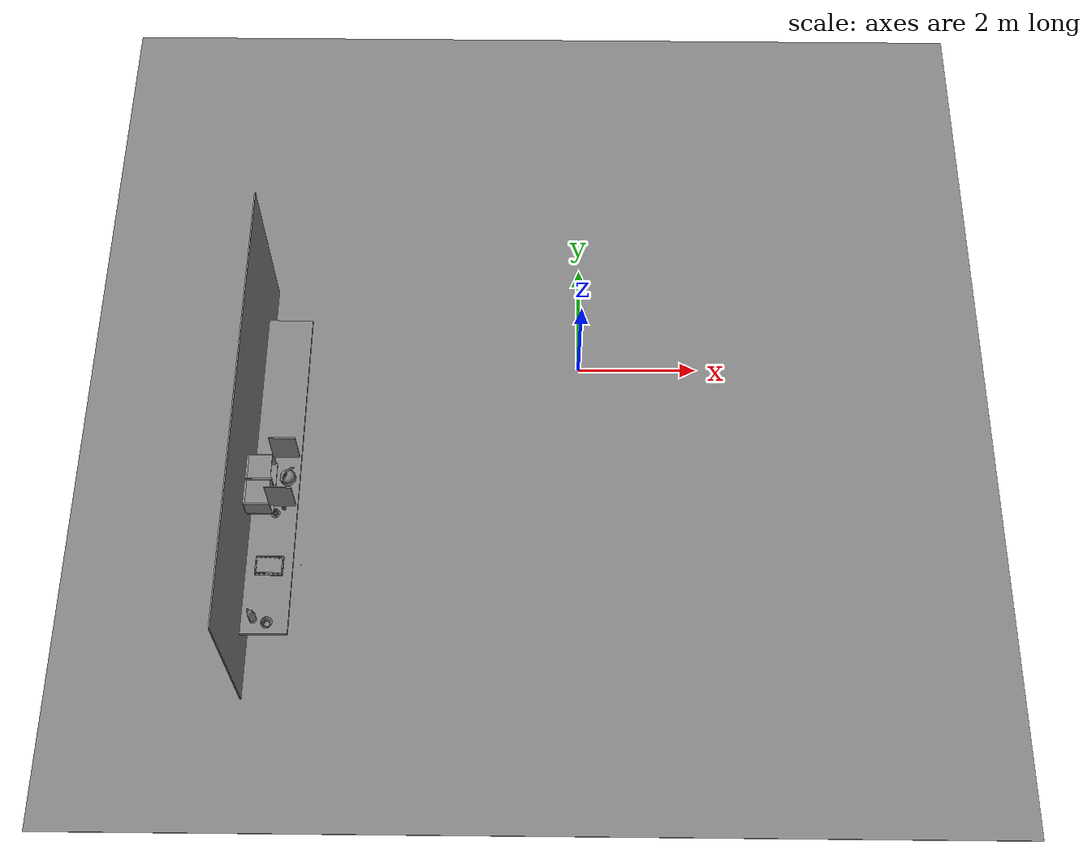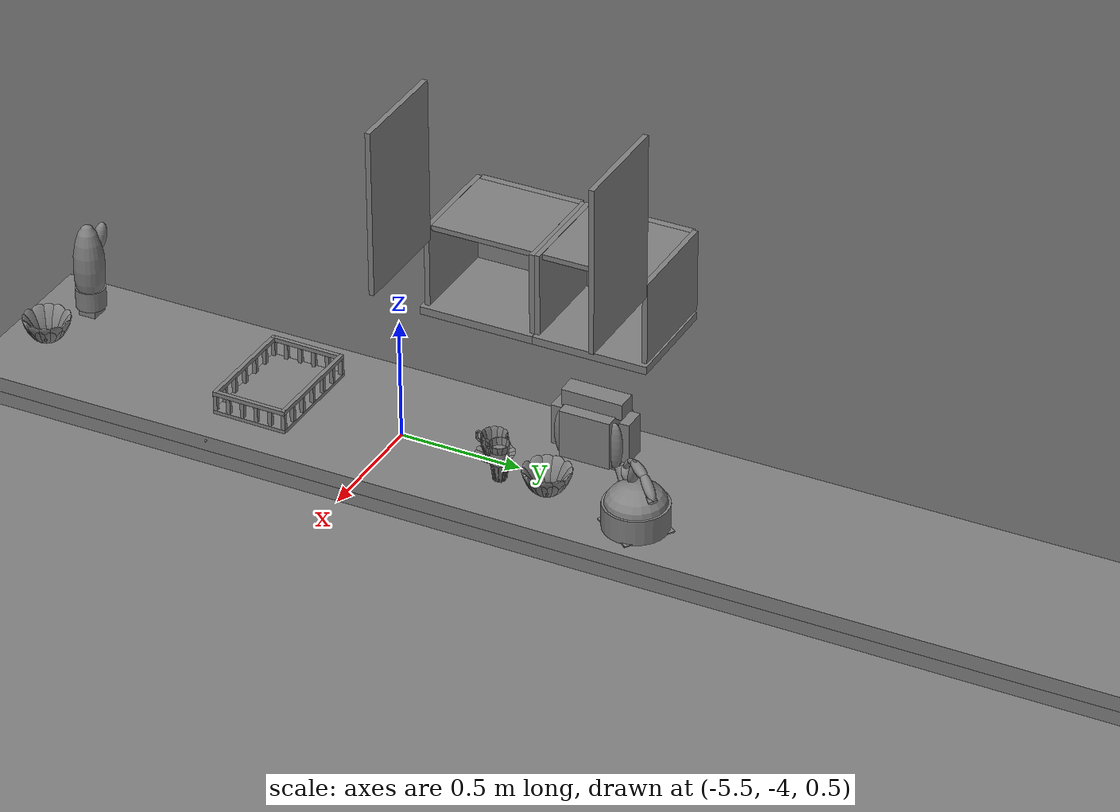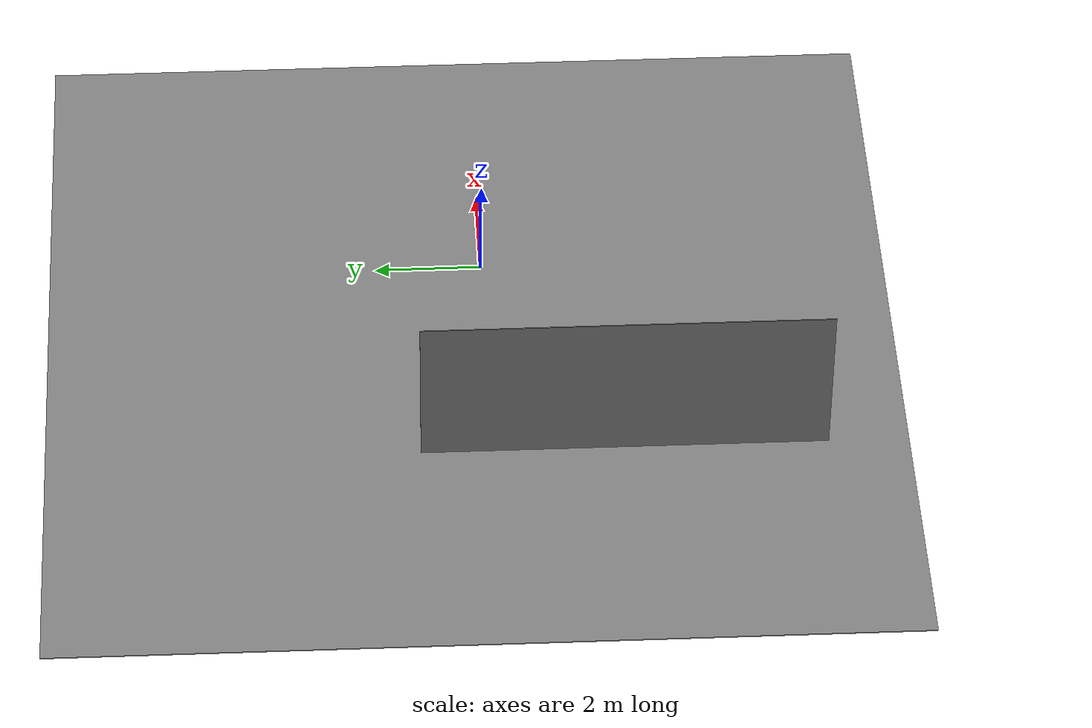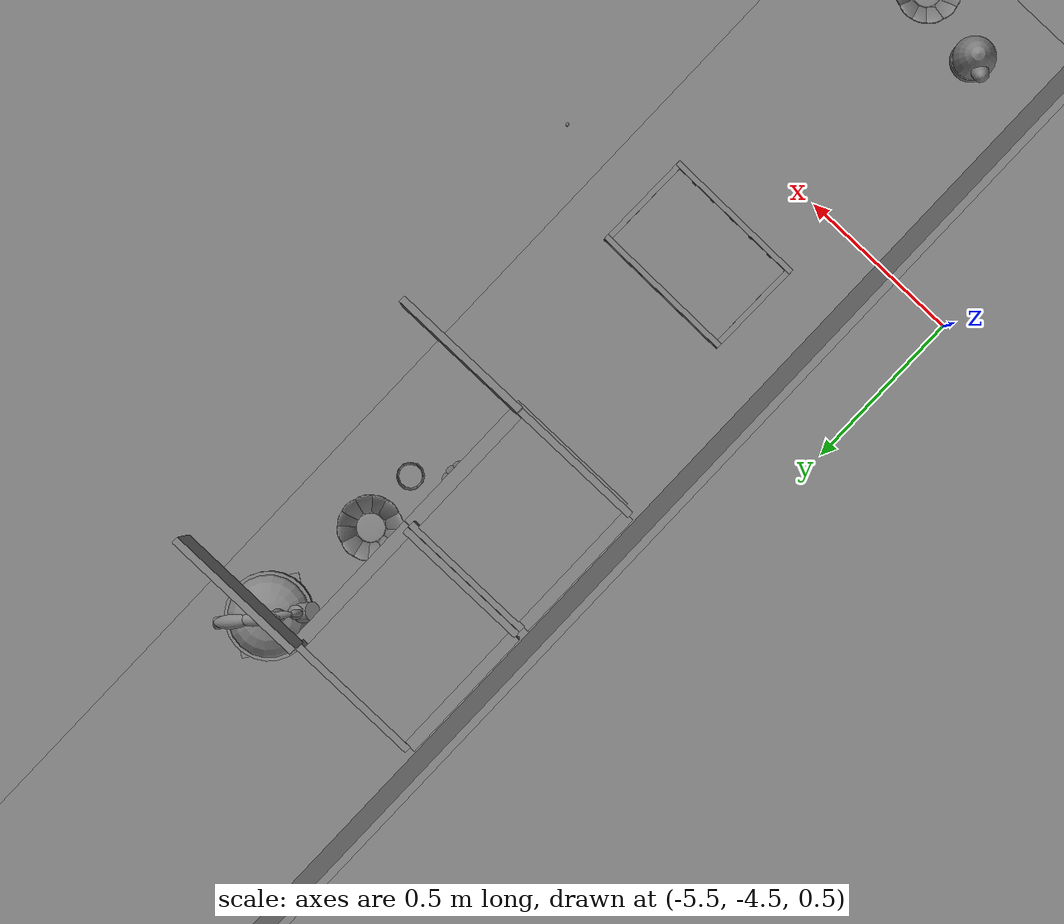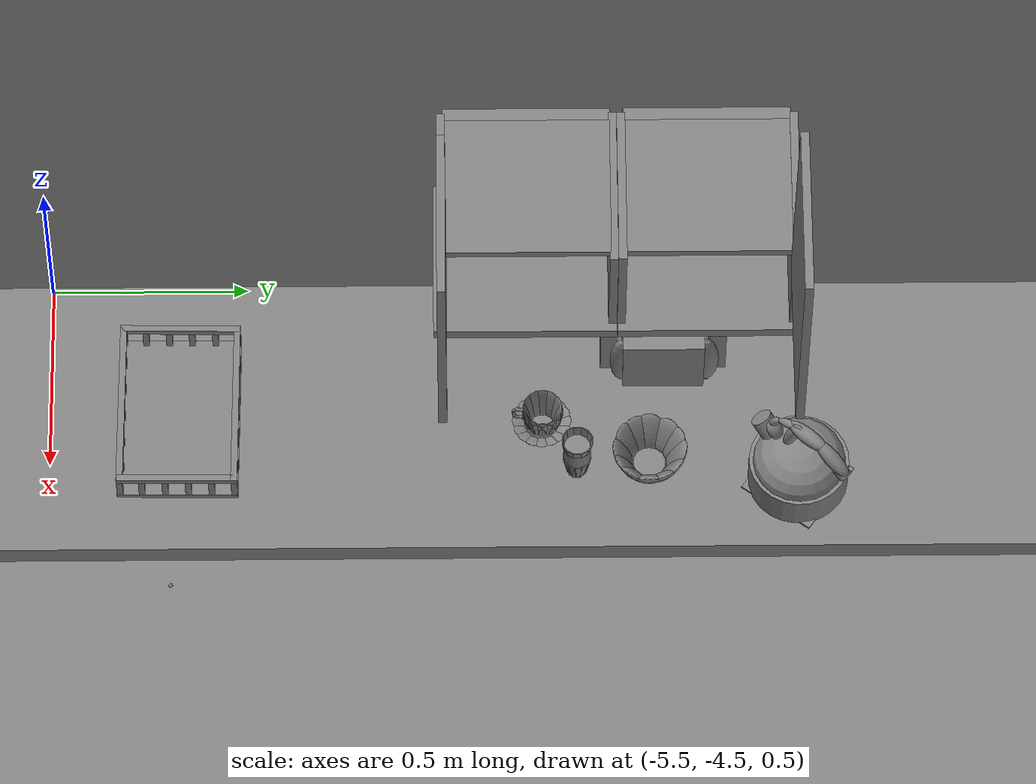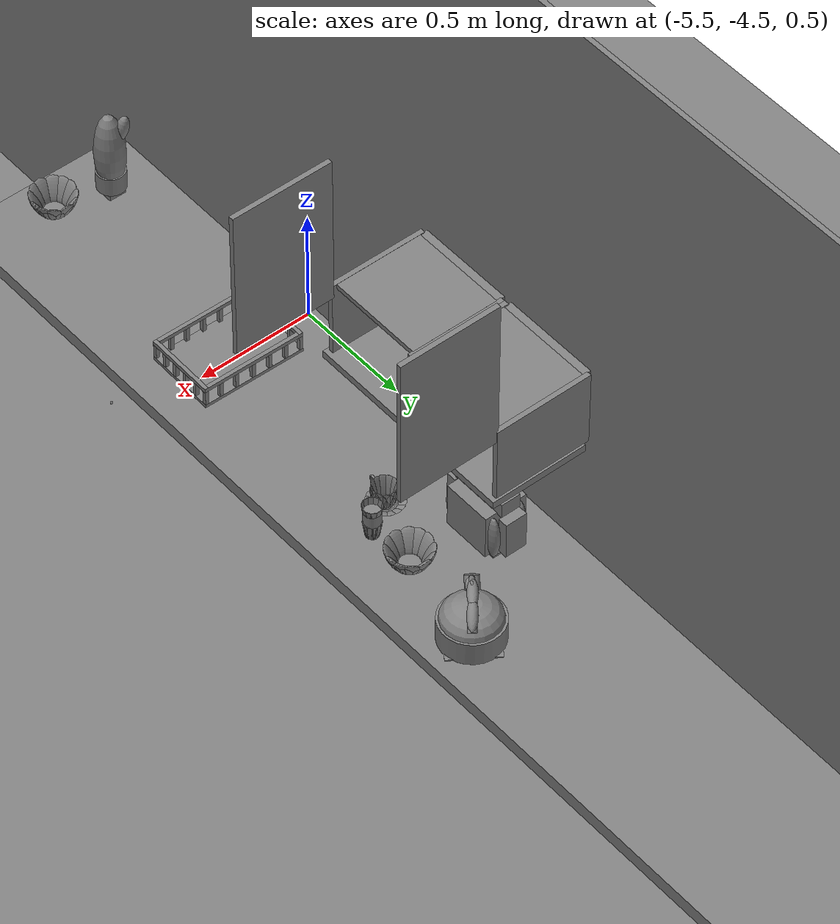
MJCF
<mujoco>
    <option gravity="0.000000000 0.000000000 -9.810000420" timestep="0.0049999999" integrator="implicitfast" density="9.8000002" viscosity="1.8000001e-05" noslip_iterations="10" iterations="100" sdf_iterations="50">
        <flag multiccd="disable"/>
    </option>
    <size memory="1000M"/>
    <compiler coordinate="local"/>
    <worldbody>
        <light cutoff="30" pos="0 1 1" dir="0 -1 -2"/>
        <light cutoff="30" pos="0 -1 1" dir="0 1 -2"/>
        <body pos="-4.860558510 -4.149443150 1.004824519" euler="0.000000000 0.000000000 -90.691093445" name="openloong_gripper_2f85_fix_base_usda_Basket_Kitchen_01">
            <geom contype="1" conaffinity="1" density="1000" type="box" material="" rgba="0.500000000 0.500000000 0.500000000 1.000000000" solimp="0.899999976 0.949999988 0.001000000" friction="1.000000000 0.005000000 0.000100000" solref="0.020000000 1.000000000" margin="0" condim="3" group="0" pos="0.086542509 0.207580954 0.047887992" quat="0.707107008 0.000000000 0.000000000 0.707106411" size="0.007600000 0.007600000 0.032000002" name="openloong_gripper_2f85_fix_base_usda_geom_F24471DE_F40A_4B3D_9B84_302D82CA505B"/>
            <geom contype="1" conaffinity="1" density="1000" type="box" material="" rgba="0.500000000 0.500000000 0.500000000 1.000000000" solimp="0.899999976 0.949999988 0.001000000" friction="1.000000000 0.005000000 0.000100000" solref="0.020000000 1.000000000" margin="0" condim="3" group="0" pos="-0.140816495 0.143605426 0.047889423" quat="0.707107008 0.000000000 0.000000000 0.707106411" size="0.007600000 0.007600000 0.032000002" name="openloong_gripper_2f85_fix_base_usda_geom_7ADE9BB6_D2A5_44A7_9826_A5D32B53B55F"/>
            <geom contype="1" conaffinity="1" density="1000" type="box" material="" rgba="0.500000000 0.500000000 0.500000000 1.000000000" solimp="0.899999976 0.949999988 0.001000000" friction="1.000000000 0.005000000 0.000100000" solref="0.020000000 1.000000000" margin="0" condim="3" group="0" pos="-0.140816212 -0.070956804 0.047888946" quat="0.707107008 0.000000000 0.000000000 0.707106411" size="0.007600000 0.007600000 0.032000002" name="openloong_gripper_2f85_fix_base_usda_geom_F2007643_250D_453C_9E4E_6F3BA478C8D1"/>
            <geom contype="1" conaffinity="1" density="1000" type="box" material="" rgba="0.500000000 0.500000000 0.500000000 1.000000000" solimp="0.899999976 0.949999988 0.001000000" friction="1.000000000 0.005000000 0.000100000" solref="0.020000000 1.000000000" margin="0" condim="3" group="0" pos="0.140802577 0.207580566 0.047887899" quat="0.707107008 0.000000000 0.000000000 0.707106411" size="0.007600000 0.007600000 0.032000002" name="openloong_gripper_2f85_fix_base_usda_geom_792417C0_86B1_46F0_A1BE_169978F638DE"/>
            <geom contype="1" conaffinity="1" density="1000" type="box" material="" rgba="0.500000000 0.500000000 0.500000000 1.000000000" solimp="0.899999976 0.949999988 0.001000000" friction="1.000000000 0.005000000 0.000100000" solref="0.020000000 1.000000000" margin="0" condim="3" group="0" pos="0.086541750 -0.207636267 0.047888279" quat="0.707107008 0.000000000 0.000000000 0.707106411" size="0.007600000 0.007600000 0.032000002" name="openloong_gripper_2f85_fix_base_usda_geom_CEEE1AB6_EF00_4580_ABD2_0D518A843EE5"/>
            <geom contype="1" conaffinity="1" density="1000" type="box" material="" rgba="0.500000000 0.500000000 0.500000000 1.000000000" solimp="0.899999976 0.949999988 0.001000000" friction="1.000000000 0.005000000 0.000100000" solref="0.020000000 1.000000000" margin="0" condim="3" group="0" pos="0.140633777 -0.000001907 0.087263681" quat="0.707107008 0.000000000 0.000000000 0.707106411" size="0.215199992 0.008000000 0.008400000" name="openloong_gripper_2f85_fix_base_usda_geom_112615C7_AE05_461B_850F_856DDFDFC42C"/>
            <geom contype="1" conaffinity="1" density="1000" type="box" material="" rgba="0.500000000 0.500000000 0.500000000 1.000000000" solimp="0.899999976 0.949999988 0.001000000" friction="1.000000000 0.005000000 0.000100000" solref="0.020000000 1.000000000" margin="0" condim="3" group="0" pos="-0.027960587 -0.207636639 0.047888566" quat="0.707107008 0.000000000 0.000000000 0.707106411" size="0.007600000 0.007600000 0.032000002" name="openloong_gripper_2f85_fix_base_usda_geom_7BF746FF_DD50_404D_A564_FD775E4BD05D"/>
            <geom contype="1" conaffinity="1" density="1000" type="box" material="" rgba="0.500000000 0.500000000 0.500000000 1.000000000" solimp="0.899999976 0.949999988 0.001000000" friction="1.000000000 0.005000000 0.000100000" solref="0.020000000 1.000000000" margin="0" condim="3" group="0" pos="-0.140816122 -0.141625211 0.047888853" quat="0.707107008 0.000000000 0.000000000 0.707106411" size="0.007600000 0.007600000 0.032000002" name="openloong_gripper_2f85_fix_base_usda_geom_15C01C9E_28E4_44EF_95D5_EC995DF61277"/>
            <geom contype="1" conaffinity="1" density="1000" type="box" material="" rgba="0.500000000 0.500000000 0.500000000 1.000000000" solimp="0.899999976 0.949999988 0.001000000" friction="1.000000000 0.005000000 0.000100000" solref="0.020000000 1.000000000" margin="0" condim="3" group="0" pos="-0.140816122 0.207580194 0.047888756" quat="0.707107008 0.000000000 0.000000000 0.707106411" size="0.007600000 0.007600000 0.032000002" name="openloong_gripper_2f85_fix_base_usda_geom_927F5E77_B7BC_42E5_9951_E6C418AC76BB"/>
            <geom contype="1" conaffinity="1" density="1000" type="box" material="" rgba="0.500000000 0.500000000 0.500000000 1.000000000" solimp="0.899999976 0.949999988 0.001000000" friction="1.000000000 0.005000000 0.000100000" solref="0.020000000 1.000000000" margin="0" condim="3" group="0" pos="0.140800864 -0.070956804 0.047888376" quat="0.707107008 0.000000000 0.000000000 0.707106411" size="0.007600000 0.007600000 0.032000002" name="openloong_gripper_2f85_fix_base_usda_geom_E13089A9_5F2B_4568_8B4A_E45EA5F5E73D"/>
            <geom contype="1" conaffinity="1" density="1000" type="box" material="" rgba="0.500000000 0.500000000 0.500000000 1.000000000" solimp="0.899999976 0.949999988 0.001000000" friction="1.000000000 0.005000000 0.000100000" solref="0.020000000 1.000000000" margin="0" condim="3" group="0" pos="0.140800476 0.002393341 0.047888376" quat="0.707107008 0.000000000 0.000000000 0.707106411" size="0.007600000 0.007600000 0.032000002" name="openloong_gripper_2f85_fix_base_usda_geom_75656F7B_2B58_4A38_96FE_76DFD17ECACE"/>
            <geom contype="1" conaffinity="1" density="1000" type="box" material="" rgba="0.500000000 0.500000000 0.500000000 1.000000000" solimp="0.899999976 0.949999988 0.001000000" friction="1.000000000 0.005000000 0.000100000" solref="0.020000000 1.000000000" margin="0" condim="3" group="0" pos="-0.140543848 -0.000001526 0.087263964" quat="0.707107008 0.000000000 0.000000000 0.707106411" size="0.215199992 0.008000000 0.008400000" name="openloong_gripper_2f85_fix_base_usda_geom_275244DF_9FC4_48BC_9B53_A961E5EA1EFC"/>
            <geom contype="1" conaffinity="1" density="1000" type="box" material="" rgba="0.500000000 0.500000000 0.500000000 1.000000000" solimp="0.899999976 0.949999988 0.001000000" friction="1.000000000 0.005000000 0.000100000" solref="0.020000000 1.000000000" margin="0" condim="3" group="0" pos="-0.140816018 0.075380705 0.047889233" quat="0.707107008 0.000000000 0.000000000 0.707106411" size="0.007600000 0.007600000 0.032000002" name="openloong_gripper_2f85_fix_base_usda_geom_7530B980_6832_490C_8EAE_51FB025C67B3"/>
            <geom contype="1" conaffinity="1" density="1000" type="box" material="" rgba="0.500000000 0.500000000 0.500000000 1.000000000" solimp="0.899999976 0.949999988 0.001000000" friction="1.000000000 0.005000000 0.000100000" solref="0.020000000 1.000000000" margin="0" condim="3" group="0" pos="0.140801147 -0.141625211 0.047888279" quat="0.707107008 0.000000000 0.000000000 0.707106411" size="0.007600000 0.007600000 0.032000002" name="openloong_gripper_2f85_fix_base_usda_geom_39A2DBD8_A0B4_4E51_A101_2034B1B13C13"/>
            <geom contype="1" conaffinity="1" density="1000" type="box" material="" rgba="0.500000000 0.500000000 0.500000000 1.000000000" solimp="0.899999976 0.949999988 0.001000000" friction="1.000000000 0.005000000 0.000100000" solref="0.020000000 1.000000000" margin="0" condim="3" group="0" pos="0.000000000 -0.207717523 0.087263964" quat="0.707107008 0.000000000 0.000000000 0.707106411" size="0.008000000 0.148000002 0.008400000" name="openloong_gripper_2f85_fix_base_usda_geom_E5C7C450_1CE4_42B3_A701_4CA49D9A6FA3"/>
            <geom contype="1" conaffinity="1" density="1000" type="box" material="" rgba="0.500000000 0.500000000 0.500000000 1.000000000" solimp="0.899999976 0.949999988 0.001000000" friction="1.000000000 0.005000000 0.000100000" solref="0.020000000 1.000000000" margin="0" condim="3" group="0" pos="0.029044246 -0.207635880 0.047888376" quat="0.707107008 0.000000000 0.000000000 0.707106411" size="0.007600000 0.007600000 0.032000002" name="openloong_gripper_2f85_fix_base_usda_geom_AA046934_1314_476A_81AC_1943F9E84B57"/>
            <geom contype="1" conaffinity="1" density="1000" type="box" material="" rgba="0.500000000 0.500000000 0.500000000 1.000000000" solimp="0.899999976 0.949999988 0.001000000" friction="1.000000000 0.005000000 0.000100000" solref="0.020000000 1.000000000" margin="0" condim="3" group="0" pos="0.140800476 0.075379565 0.047888566" quat="0.707107008 0.000000000 0.000000000 0.707106411" size="0.007600000 0.007600000 0.032000002" name="openloong_gripper_2f85_fix_base_usda_geom_28D7C629_5965_4F38_BC01_44C39658CC39"/>
            <geom contype="1" conaffinity="1" density="1000" type="box" material="" rgba="0.500000000 0.500000000 0.500000000 1.000000000" solimp="0.899999976 0.949999988 0.001000000" friction="1.000000000 0.005000000 0.000100000" solref="0.020000000 1.000000000" margin="0" condim="3" group="0" pos="-0.027959539 0.207580566 0.047888376" quat="0.707107008 0.000000000 0.000000000 0.707106411" size="0.007600000 0.007600000 0.032000002" name="openloong_gripper_2f85_fix_base_usda_geom_0ECB858D_5C91_4CFC_9C7E_27CC5F04B7F4"/>
            <geom contype="1" conaffinity="1" density="1000" type="box" material="" rgba="0.500000000 0.500000000 0.500000000 1.000000000" solimp="0.899999976 0.949999988 0.001000000" friction="1.000000000 0.005000000 0.000100000" solref="0.020000000 1.000000000" margin="0" condim="3" group="0" pos="0.140799999 0.143604279 0.047888756" quat="0.707107008 0.000000000 0.000000000 0.707106411" size="0.007600000 0.007600000 0.032000002" name="openloong_gripper_2f85_fix_base_usda_geom_27BAF860_AC0B_447B_B7FE_E8250901CAFB"/>
            <geom contype="1" conaffinity="1" density="1000" type="box" material="" rgba="0.500000000 0.500000000 0.500000000 1.000000000" solimp="0.899999976 0.949999988 0.001000000" friction="1.000000000 0.005000000 0.000100000" solref="0.020000000 1.000000000" margin="0" condim="3" group="0" pos="-0.140816122 0.002393723 0.047889233" quat="0.707107008 0.000000000 0.000000000 0.707106411" size="0.007600000 0.007600000 0.032000002" name="openloong_gripper_2f85_fix_base_usda_geom_5650B869_3A45_4225_84E3_2C31FB38A207"/>
            <geom contype="1" conaffinity="1" density="1000" type="box" material="" rgba="0.500000000 0.500000000 0.500000000 1.000000000" solimp="0.899999976 0.949999988 0.001000000" friction="1.000000000 0.005000000 0.000100000" solref="0.020000000 1.000000000" margin="0" condim="3" group="0" pos="-0.085476689 0.207580194 0.047888566" quat="0.707107008 0.000000000 0.000000000 0.707106411" size="0.007600000 0.007600000 0.032000002" name="openloong_gripper_2f85_fix_base_usda_geom_FD6B09A5_071F_430C_B178_4D3E7E2C80F2"/>
            <geom contype="1" conaffinity="1" density="1000" type="box" material="" rgba="0.500000000 0.500000000 0.500000000 1.000000000" solimp="0.899999976 0.949999988 0.001000000" friction="1.000000000 0.005000000 0.000100000" solref="0.020000000 1.000000000" margin="0" condim="3" group="0" pos="0.000000000 0.207718283 0.087263964" quat="0.707107008 0.000000000 0.000000000 0.707106411" size="0.008000000 0.148000002 0.008400000" name="openloong_gripper_2f85_fix_base_usda_geom_CC3DCDEB_4729_4156_89B7_940E255A16A6"/>
            <geom contype="1" conaffinity="1" density="1000" type="box" material="" rgba="0.500000000 0.500000000 0.500000000 1.000000000" solimp="0.899999976 0.949999988 0.001000000" friction="1.000000000 0.005000000 0.000100000" solref="0.020000000 1.000000000" margin="0" condim="3" group="0" pos="0.029045582 0.207581714 0.047888279" quat="0.707107008 0.000000000 0.000000000 0.707106411" size="0.007600000 0.007600000 0.032000002" name="openloong_gripper_2f85_fix_base_usda_geom_BABC2CC7_A77F_4790_BF62_97C9ABC714A2"/>
            <geom contype="1" conaffinity="1" density="1000" type="box" material="" rgba="0.500000000 0.500000000 0.500000000 1.000000000" solimp="0.899999976 0.949999988 0.001000000" friction="1.000000000 0.005000000 0.000100000" solref="0.020000000 1.000000000" margin="0" condim="3" group="0" pos="-0.140816122 -0.207636267 0.047888853" quat="0.707107008 0.000000000 0.000000000 0.707106411" size="0.007600000 0.007600000 0.032000002" name="openloong_gripper_2f85_fix_base_usda_geom_911A3921_EABD_4164_B80B_6632B47AF567"/>
            <geom contype="1" conaffinity="1" density="1000" type="box" material="" rgba="0.500000000 0.500000000 0.500000000 1.000000000" solimp="0.899999976 0.949999988 0.001000000" friction="1.000000000 0.005000000 0.000100000" solref="0.020000000 1.000000000" margin="0" condim="3" group="0" pos="-0.085477069 -0.207636639 0.047888756" quat="0.707107008 0.000000000 0.000000000 0.707106411" size="0.007600000 0.007600000 0.032000002" name="openloong_gripper_2f85_fix_base_usda_geom_EA913064_C710_46EF_9580_F51A9CE0000D"/>
            <geom contype="1" conaffinity="1" density="1000" type="box" material="" rgba="0.500000000 0.500000000 0.500000000 1.000000000" solimp="0.899999976 0.949999988 0.001000000" friction="1.000000000 0.005000000 0.000100000" solref="0.020000000 1.000000000" margin="0" condim="3" group="0" pos="-0.000012112 0.000000381 0.008534336" quat="0.707107008 0.000000000 0.000000000 0.707106411" size="0.215199992 0.148800001 0.008400000" name="openloong_gripper_2f85_fix_base_usda_geom_BC209F63_8DA9_42B3_88CD_D58B1F2AD46A"/>
            <geom contype="1" conaffinity="1" density="1000" type="box" material="" rgba="0.500000000 0.500000000 0.500000000 1.000000000" solimp="0.899999976 0.949999988 0.001000000" friction="1.000000000 0.005000000 0.000100000" solref="0.020000000 1.000000000" margin="0" condim="3" group="0" pos="0.140801623 -0.207636267 0.047888186" quat="0.707107008 0.000000000 0.000000000 0.707106411" size="0.007600000 0.007600000 0.032000002" name="openloong_gripper_2f85_fix_base_usda_geom_76E615A9_8190_4F12_B969_648149E9B06D"/>
            <freejoint name="openloong_gripper_2f85_fix_base_usda_Basket_Kitchen_01_joint"/>
            <site size="0.005000000 0.005000000 0.005000000" rgba="0.500000000 0.500000000 0.500000000 1.000000000" pos="0.000000000 0.000000000 0.000000000" quat="1.000000000 0.000000000 0.000000000 0.000000000" group="0" type="sphere" name="openloong_gripper_2f85_fix_base_usda_Basket_Kitchen_01site"/>
        </body>
        <body pos="-4.721817970 -2.990536690 1.027358174" euler="0.000000000 0.000000000 89.999946594" name="Interactive Objcets_bow_02">
            <geom contype="1" conaffinity="1" density="1000" type="ellipsoid" material="" rgba="0.500000000 0.500000000 0.500000000 1.000000000" solimp="0.899999976 0.949999988 0.001000000" friction="1.000000000 0.005000000 0.000100000" solref="0.020000000 1.000000000" margin="0" condim="3" group="0" pos="-0.058925860 -0.029528141 0.044118762" quat="0.223252773 0.231952101 0.054787740 -0.945174515" size="0.010000000 0.039999999 0.052000001" name="Interactive Objcets_geom_978AD156_D4A8_43B5_9DC7_CA337985D651"/>
            <geom contype="1" conaffinity="1" density="1000" type="ellipsoid" material="" rgba="0.500000000 0.500000000 0.500000000 1.000000000" solimp="0.899999976 0.949999988 0.001000000" friction="1.000000000 0.005000000 0.000100000" solref="0.020000000 1.000000000" margin="0" condim="3" group="0" pos="0.000082973 0.000000000 0.000446677" quat="1.000000000 0.000000000 0.000000000 0.000000000" size="0.039999999 0.039999999 0.002000000" name="Interactive Objcets_geom_CCBEBB60_EE7F_4D68_8D3D_B7D04D4C0AB3"/>
            <geom contype="1" conaffinity="1" density="1000" type="ellipsoid" material="" rgba="0.500000000 0.500000000 0.500000000 1.000000000" solimp="0.899999976 0.949999988 0.001000000" friction="1.000000000 0.005000000 0.000100000" solref="0.020000000 1.000000000" margin="0" condim="3" group="0" pos="0.029448029 -0.059084892 0.044118762" quat="0.825555801 0.125530601 0.202597082 -0.511521280" size="0.010000000 0.039999999 0.052000001" name="Interactive Objcets_geom_A1D3D646_FB10_40B2_9EA9_A5CDE1E39764"/>
            <geom contype="1" conaffinity="1" density="1000" type="ellipsoid" material="" rgba="0.500000000 0.500000000 0.500000000 1.000000000" solimp="0.899999976 0.949999988 0.001000000" friction="1.000000000 0.005000000 0.000100000" solref="0.020000000 1.000000000" margin="0" condim="3" group="0" pos="0.000082973 0.000000000 0.005656481" quat="1.000000000 0.000000000 0.000000000 0.000000000" size="0.039999999 0.039999999 0.002000000" name="Interactive Objcets_geom_2EEEC09E_C7F6_415F_A732_920125312752"/>
            <geom contype="1" conaffinity="1" density="1000" type="ellipsoid" material="" rgba="0.500000000 0.500000000 0.500000000 1.000000000" solimp="0.899999976 0.949999988 0.001000000" friction="1.000000000 0.005000000 0.000100000" solref="0.020000000 1.000000000" margin="0" condim="3" group="0" pos="-0.040080305 -0.052354336 0.044118762" quat="0.429593205 0.213749886 0.105425082 -0.871003032" size="0.010000000 0.039999999 0.052000001" name="Interactive Objcets_geom_B7AE2277_3D8C_4C06_A272_99DD8E679A2C"/>
            <geom contype="1" conaffinity="1" density="1000" type="ellipsoid" material="" rgba="0.500000000 0.500000000 0.500000000 1.000000000" solimp="0.899999976 0.949999988 0.001000000" friction="1.000000000 0.005000000 0.000100000" solref="0.020000000 1.000000000" margin="0" condim="3" group="0" pos="-0.065898418 -0.000007629 0.044118762" quat="0.971183062 -0.000000142 -0.238334835 0.000000030" size="0.010000000 0.039999999 0.052000001" name="Interactive Objcets_geom_790A3AAC_87FC_4E93_80A4_DEBA505462E7"/>
            <geom contype="1" conaffinity="1" density="1000" type="ellipsoid" material="" rgba="0.500000000 0.500000000 0.500000000 1.000000000" solimp="0.899999976 0.949999988 0.001000000" friction="1.000000000 0.005000000 0.000100000" solref="0.020000000 1.000000000" margin="0" condim="3" group="0" pos="0.059080135 0.029512405 0.044118762" quat="0.223252743 -0.231952220 -0.054787420 -0.945174456" size="0.010000000 0.039999999 0.052000001" name="Interactive Objcets_geom_8A29A9F0_BAC7_4C96_B2E5_D5E40397CD27"/>
            <geom contype="1" conaffinity="1" density="1000" type="ellipsoid" material="" rgba="0.500000000 0.500000000 0.500000000 1.000000000" solimp="0.899999976 0.949999988 0.001000000" friction="1.000000000 0.005000000 0.000100000" solref="0.020000000 1.000000000" margin="0" condim="3" group="0" pos="0.066052437 -0.000007629 0.044118762" quat="0.971183062 -0.000000156 0.238334835 0.000000030" size="0.010000000 0.039999999 0.052000001" name="Interactive Objcets_geom_198BB135_3F3B_4D62_9F5B_DDD5A4344FF1"/>
            <geom contype="1" conaffinity="1" density="1000" type="ellipsoid" material="" rgba="0.500000000 0.500000000 0.500000000 1.000000000" solimp="0.899999976 0.949999988 0.001000000" friction="1.000000000 0.005000000 0.000100000" solref="0.020000000 1.000000000" margin="0" condim="3" group="0" pos="0.000243668 -0.065982819 0.044118762" quat="0.687598705 0.168314636 0.168741375 -0.685860336" size="0.010000000 0.039999999 0.052000001" name="Interactive Objcets_geom_D4E37683_354D_4810_954C_07F006F5D816"/>
            <geom contype="1" conaffinity="1" density="1000" type="ellipsoid" material="" rgba="0.500000000 0.500000000 0.500000000 1.000000000" solimp="0.899999976 0.949999988 0.001000000" friction="1.000000000 0.005000000 0.000100000" solref="0.020000000 1.000000000" margin="0" condim="3" group="0" pos="-0.000090118 0.065967560 0.044118762" quat="0.687598705 -0.168314859 -0.168741152 -0.685860336" size="0.010000000 0.039999999 0.052000001" name="Interactive Objcets_geom_99BC3AC0_47E8_4C28_A548_9C499F30983C"/>
            <geom contype="1" conaffinity="1" density="1000" type="ellipsoid" material="" rgba="0.500000000 0.500000000 0.500000000 1.000000000" solimp="0.899999976 0.949999988 0.001000000" friction="1.000000000 0.005000000 0.000100000" solref="0.020000000 1.000000000" margin="0" condim="3" group="0" pos="0.052321676 -0.040297508 0.044118762" quat="0.919264674 0.076882742 0.225593731 -0.313287675" size="0.010000000 0.039999999 0.052000001" name="Interactive Objcets_geom_2037EC34_875B_4CB4_B16D_1FDEC1B69515"/>
            <geom contype="1" conaffinity="1" density="1000" type="ellipsoid" material="" rgba="0.500000000 0.500000000 0.500000000 1.000000000" solimp="0.899999976 0.949999988 0.001000000" friction="1.000000000 0.005000000 0.000100000" solref="0.020000000 1.000000000" margin="0" condim="3" group="0" pos="0.040234569 0.052338600 0.044118762" quat="0.429593176 -0.213750035 -0.105424814 -0.871002913" size="0.010000000 0.039999999 0.052000001" name="Interactive Objcets_geom_42E27CDE_3EBF_40D7_BA34_DCD5A995CEEB"/>
            <geom contype="1" conaffinity="1" density="1000" type="ellipsoid" material="" rgba="0.500000000 0.500000000 0.500000000 1.000000000" solimp="0.899999976 0.949999988 0.001000000" friction="1.000000000 0.005000000 0.000100000" solref="0.020000000 1.000000000" margin="0" condim="3" group="0" pos="-0.052167647 0.040282249 0.044118762" quat="0.919264615 -0.076883025 -0.225593641 -0.313287735" size="0.010000000 0.039999999 0.052000001" name="Interactive Objcets_geom_515EA2D5_DE06_43B3_B398_9F95BF088553"/>
            <geom contype="1" conaffinity="1" density="1000" type="ellipsoid" material="" rgba="0.500000000 0.500000000 0.500000000 1.000000000" solimp="0.899999976 0.949999988 0.001000000" friction="1.000000000 0.005000000 0.000100000" solref="0.020000000 1.000000000" margin="0" condim="3" group="0" pos="-0.029293532 0.059069633 0.044118762" quat="0.825555801 -0.125530809 -0.202596903 -0.511521280" size="0.010000000 0.039999999 0.052000001" name="Interactive Objcets_geom_1519FC49_11A7_4F0C_AE3E_3D54A75C2862"/>
            <freejoint name="Interactive Objcets_bow_02"/>
        </body>
        <body pos="-4.802892208 -3.488179445 1.876015186" euler="89.999992371 -89.999946594 0.000000000" name="Interactive Objcets_guimen_01">
            <geom contype="1" conaffinity="1" density="1000" type="box" material="" rgba="0.500000000 0.500000000 0.500000000 1.000000000" solimp="0.899999976 0.949999988 0.001000000" friction="1.000000000 0.005000000 0.000100000" solref="0.020000000 1.000000000" margin="0" condim="3" group="0" pos="0.006727934 0.314709902 -0.203009605" quat="1.000000000 0.000000119 -0.000000119 0.000000000" size="0.010000000 0.317999989 0.204999998" name="Interactive Objcets_geom_99DB6DC5_01B1_4C6C_8D46_C036F2FEC50F"/>
            <joint armature="0" stiffness="0" damping="1" axis="0.000000 1.000000 0.000000" type="hinge" name="Interactive Objcets_guimen_01"/>
        </body>
        <body pos="-4.827295780 -3.287638187 1.074643731" euler="0.000000000 0.000000000 89.999992371" name="Interactive Objcets_coffeecup_01">
            <geom contype="1" conaffinity="1" density="1000" type="ellipsoid" material="" rgba="0.500000000 0.500000000 0.500000000 1.000000000" solimp="0.899999976 0.949999988 0.001000000" friction="1.000000000 0.005000000 0.000100000" solref="0.020000000 1.000000000" margin="0" condim="3" group="0" pos="0.053700209 0.033117294 0.002976775" quat="0.496025741 -0.082236379 -0.047260769 -0.863111615" size="0.005000000 0.029999999 0.048999999" name="Interactive Objcets_geom_45B5CF43_720B_4CB6_B1E7_DCBC3061F189"/>
            <geom contype="1" conaffinity="1" density="1000" type="ellipsoid" material="" rgba="0.500000000 0.500000000 0.500000000 1.000000000" solimp="0.899999976 0.949999988 0.001000000" friction="1.000000000 0.005000000 0.000100000" solref="0.020000000 1.000000000" margin="0" condim="3" group="0" pos="0.068445444 0.017385960 0.002976775" quat="0.228377223 -0.092319682 -0.021759447 -0.968941331" size="0.005000000 0.029999999 0.048999999" name="Interactive Objcets_geom_F9B65E96_FD08_435B_B403_360E16937A5F"/>
            <geom contype="1" conaffinity="1" density="1000" type="capsule" material="" rgba="0.500000000 0.500000000 0.500000000 1.000000000" solimp="0.899999976 0.949999988 0.001000000" friction="1.000000000 0.005000000 0.000100000" solref="0.020000000 1.000000000" margin="0" condim="3" group="0" pos="-0.030251026 0.000000000 0.004966617" quat="0.480583906 -0.000000000 0.876948774 -0.000000126" size="0.004000000 0.005000000 1.000000000" name="Interactive Objcets_geom_DF8A62C5_A342_41E1_8EA3_360A01AABFD8"/>
            <geom contype="1" conaffinity="1" density="1000" type="ellipsoid" material="" rgba="0.500000000 0.500000000 0.500000000 1.000000000" solimp="0.899999976 0.949999988 0.001000000" friction="1.000000000 0.005000000 0.000100000" solref="0.020000000 1.000000000" margin="0" condim="3" group="0" pos="0.034471050 -0.037125111 0.002976775" quat="0.701517045 0.067293778 0.066836871 -0.706313014" size="0.005000000 0.029999999 0.048999999" name="Interactive Objcets_geom_BD873AF5_04BB_4723_A266_9B564A2B2A4C"/>
            <geom contype="1" conaffinity="1" density="1000" type="ellipsoid" material="" rgba="0.500000000 0.500000000 0.500000000 1.000000000" solimp="0.899999976 0.949999988 0.001000000" friction="1.000000000 0.005000000 0.000100000" solref="0.020000000 1.000000000" margin="0" condim="3" group="0" pos="0.035336256 0.000558376 -0.045152068" quat="0.999999881 0.000000000 0.000000000 0.000000000" size="0.029999999 0.029999999 0.001000000" name="Interactive Objcets_geom_0705D78D_F91F_4472_876C_F2879D2A40B0"/>
            <geom contype="1" conaffinity="1" density="1000" type="capsule" material="" rgba="0.500000000 0.500000000 0.500000000 1.000000000" solimp="0.899999976 0.949999988 0.001000000" friction="1.000000000 0.005000000 0.000100000" solref="0.020000000 1.000000000" margin="0" condim="3" group="0" pos="-0.021276474 0.000000000 0.038509369" quat="0.633189917 0.000000000 0.773996413 0.000000000" size="0.004000000 0.009000000 1.000000000" name="Interactive Objcets_geom_29BA1FF0_415E_4492_8CC7_AF6AAF1C9997"/>
            <geom contype="1" conaffinity="1" density="1000" type="capsule" material="" rgba="0.500000000 0.500000000 0.500000000 1.000000000" solimp="0.899999976 0.949999988 0.001000000" friction="1.000000000 0.005000000 0.000100000" solref="0.020000000 1.000000000" margin="0" condim="3" group="0" pos="-0.018014431 0.000000000 0.001762271" quat="0.707106769 -0.000000004 0.707106709 -0.000000088" size="0.004000000 0.005000000 1.000000000" name="Interactive Objcets_geom_25E2FCE9_40C7_4AB3_98F6_48E4F4F94BE4"/>
            <geom contype="1" conaffinity="1" density="1000" type="ellipsoid" material="" rgba="0.500000000 0.500000000 0.500000000 1.000000000" solimp="0.899999976 0.949999988 0.001000000" friction="1.000000000 0.005000000 0.000100000" solref="0.020000000 1.000000000" margin="0" condim="3" group="0" pos="0.001010895 -0.016271591 0.002976775" quat="0.228377163 0.092315644 0.021758538 -0.968941689" size="0.005000000 0.029999999 0.048999999" name="Interactive Objcets_geom_A1C1FD28_6F04_47F4_BF00_792432920AE9"/>
            <geom contype="1" conaffinity="1" density="1000" type="capsule" material="" rgba="0.500000000 0.500000000 0.500000000 1.000000000" solimp="0.899999976 0.949999988 0.001000000" friction="1.000000000 0.005000000 0.000100000" solref="0.020000000 1.000000000" margin="0" condim="3" group="0" pos="-0.008219719 0.000000000 -0.000944734" quat="0.364379913 0.000000063 0.931250274 -0.000000063" size="0.004000000 0.003000000 1.000000000" name="Interactive Objcets_geom_5EE5F15D_DC1A_4710_8CDA_5DF4C76348FA"/>
            <geom contype="1" conaffinity="1" density="1000" type="ellipsoid" material="" rgba="0.500000000 0.500000000 0.500000000 1.000000000" solimp="0.899999976 0.949999988 0.001000000" friction="1.000000000 0.005000000 0.000100000" solref="0.020000000 1.000000000" margin="0" condim="3" group="0" pos="0.002039194 0.019308567 0.002976775" quat="0.961933970 -0.024419386 -0.091652036 -0.256293654" size="0.005000000 0.029999999 0.048999999" name="Interactive Objcets_geom_772CFA69_0829_48E9_9177_49728F076B01"/>
            <geom contype="1" conaffinity="1" density="1000" type="capsule" material="" rgba="0.500000000 0.500000000 0.500000000 1.000000000" solimp="0.899999976 0.949999988 0.001000000" friction="1.000000000 0.005000000 0.000100000" solref="0.020000000 1.000000000" margin="0" condim="3" group="0" pos="-0.033022881 0.000000000 0.037873149" quat="0.874267220 0.000000042 0.485444903 -0.000000084" size="0.004000000 0.004000000 1.000000000" name="Interactive Objcets_geom_984A3F27_87EC_498E_978E_D838F7B73A24"/>
            <geom contype="1" conaffinity="1" density="1000" type="ellipsoid" material="" rgba="0.500000000 0.500000000 0.500000000 1.000000000" solimp="0.899999976 0.949999988 0.001000000" friction="1.000000000 0.005000000 0.000100000" solref="0.020000000 1.000000000" margin="0" condim="3" group="0" pos="0.034984604 0.038240910 0.002976775" quat="0.701516926 -0.067296736 -0.066839755 -0.706312656" size="0.005000000 0.029999999 0.048999999" name="Interactive Objcets_geom_3BDFB171_6604_45EF_A94E_38090F5C1780"/>
            <geom contype="1" conaffinity="1" density="1000" type="ellipsoid" material="" rgba="0.500000000 0.500000000 0.500000000 1.000000000" solimp="0.899999976 0.949999988 0.001000000" friction="1.000000000 0.005000000 0.000100000" solref="0.020000000 1.000000000" margin="0" condim="3" group="0" pos="-0.002956629 0.000558376 0.002976775" quat="0.995491505 0.000000004 -0.094849378 -0.000000089" size="0.005000000 0.029999999 0.048999999" name="Interactive Objcets_geom_F3C41F2B_1C2B_426D_B5F7_6398B938BF9A"/>
            <geom contype="1" conaffinity="1" density="1000" type="ellipsoid" material="" rgba="0.500000000 0.500000000 0.500000000 1.000000000" solimp="0.899999976 0.949999988 0.001000000" friction="1.000000000 0.005000000 0.000100000" solref="0.020000000 1.000000000" margin="0" condim="3" group="0" pos="0.017669693 0.034160614 0.002976775" quat="0.848410904 -0.049618516 -0.080835648 -0.520770907" size="0.005000000 0.029999999 0.048999999" name="Interactive Objcets_geom_395BEDEA_57EB_4103_87F3_4EC0A7C977CF"/>
            <geom contype="1" conaffinity="1" density="1000" type="ellipsoid" material="" rgba="0.500000000 0.500000000 0.500000000 1.000000000" solimp="0.899999976 0.949999988 0.001000000" friction="1.000000000 0.005000000 0.000100000" solref="0.020000000 1.000000000" margin="0" condim="3" group="0" pos="0.051787138 -0.033043861 0.002976775" quat="0.848411202 0.049616337 0.080832161 -0.520771146" size="0.005000000 0.029999999 0.048999999" name="Interactive Objcets_geom_850FC529_8EB9_4AC8_83A1_7307C499ABC1"/>
            <geom contype="1" conaffinity="1" density="1000" type="ellipsoid" material="" rgba="0.500000000 0.500000000 0.500000000 1.000000000" solimp="0.899999976 0.949999988 0.001000000" friction="1.000000000 0.005000000 0.000100000" solref="0.020000000 1.000000000" margin="0" condim="3" group="0" pos="0.035336256 0.000558376 -0.043215394" quat="0.999999881 0.000000000 0.000000000 0.000000000" size="0.029999999 0.029999999 0.001000000" name="Interactive Objcets_geom_2E9A0D23_E365_48B3_A0E7_3C2DB8AFEDE7"/>
            <geom contype="1" conaffinity="1" density="1000" type="capsule" material="" rgba="0.500000000 0.500000000 0.500000000 1.000000000" solimp="0.899999976 0.949999988 0.001000000" friction="1.000000000 0.005000000 0.000100000" solref="0.020000000 1.000000000" margin="0" condim="3" group="0" pos="-0.036300898 0.000000000 0.021037936" quat="0.044551343 -0.000000000 0.999007046 -0.000000126" size="0.004000000 0.012000000 1.000000000" name="Interactive Objcets_geom_0A3C4706_0D3C_4117_A31C_6B8698711C61"/>
            <geom contype="1" conaffinity="1" density="1000" type="ellipsoid" material="" rgba="0.500000000 0.500000000 0.500000000 1.000000000" solimp="0.899999976 0.949999988 0.001000000" friction="1.000000000 0.005000000 0.000100000" solref="0.020000000 1.000000000" margin="0" condim="3" group="0" pos="0.067416430 -0.018191338 0.002976775" quat="0.961934388 0.024418317 0.091648072 -0.256293803" size="0.005000000 0.029999999 0.048999999" name="Interactive Objcets_geom_DF9FBCB4_815C_4751_A35D_36DC9559E630"/>
            <geom contype="1" conaffinity="1" density="1000" type="ellipsoid" material="" rgba="0.500000000 0.500000000 0.500000000 1.000000000" solimp="0.899999976 0.949999988 0.001000000" friction="1.000000000 0.005000000 0.000100000" solref="0.020000000 1.000000000" margin="0" condim="3" group="0" pos="0.015755907 -0.032001972 0.002976775" quat="0.496025920 0.082232773 0.047258731 -0.863112032" size="0.005000000 0.029999999 0.048999999" name="Interactive Objcets_geom_7DC0D5D1_B3B6_4291_BCA0_8994114BB6C0"/>
            <geom contype="1" conaffinity="1" density="1000" type="ellipsoid" material="" rgba="0.500000000 0.500000000 0.500000000 1.000000000" solimp="0.899999976 0.949999988 0.001000000" friction="1.000000000 0.005000000 0.000100000" solref="0.020000000 1.000000000" margin="0" condim="3" group="0" pos="0.072411790 0.000558376 0.002976775" quat="0.995491922 -0.000000019 0.094845265 -0.000000089" size="0.005000000 0.029999999 0.048999999" name="Interactive Objcets_geom_DB199F4C_7139_4862_B7C5_99F1FF6382BA"/>
            <freejoint name="Interactive Objcets_coffeecup_01"/>
        </body>
        <body pos="-4.805274963 -2.665403366 1.876015186" euler="89.999877930 89.999969482 0.000000000" name="Interactive Objcets_guimen_02">
            <geom contype="1" conaffinity="1" density="1000" type="box" material="" rgba="0.500000000 0.500000000 0.500000000 1.000000000" solimp="0.899999976 0.949999988 0.001000000" friction="1.000000000 0.005000000 0.000100000" solref="0.020000000 1.000000000" margin="0" condim="3" group="0" pos="0.006727815 0.314709663 0.203009367" quat="0.999999940 0.000000000 0.000000000 0.000000000" size="0.010000000 0.317999989 0.204999998" name="Interactive Objcets_geom_ABB832F1_61DE_449C_84CE_92A823070313"/>
            <joint armature="0" stiffness="0" damping="1" axis="0.000000 1.000000 0.000000" type="hinge" name="Interactive Objcets_guimen_02"/>
        </body>
        <body pos="-4.705342293 -3.169416904 1.103703976" euler="0.000000000 0.000000000 0.000000000" name="Interactive Objcets_cup_02">
            <geom contype="1" conaffinity="1" density="1000" type="box" material="" rgba="0.500000000 0.500000000 0.500000000 1.000000000" solimp="0.899999976 0.949999988 0.001000000" friction="1.000000000 0.005000000 0.000100000" solref="0.020000000 1.000000000" margin="0" condim="3" group="0" pos="-0.016875744 0.022189617 -0.037281752" quat="0.944716334 -0.074092269 -0.024973858 0.318430305" size="0.010000000 0.001000000 0.035000000" name="Interactive Objcets_geom_95E37BDF_D031_414B_8925_C2733B137C62"/>
            <geom contype="1" conaffinity="1" density="1000" type="box" material="" rgba="0.500000000 0.500000000 0.500000000 1.000000000" solimp="0.899999976 0.949999988 0.001000000" friction="1.000000000 0.005000000 0.000100000" solref="0.020000000 1.000000000" margin="0" condim="3" group="0" pos="0.029378891 -0.018181801 0.062637210" quat="0.870895982 0.068302706 0.038053915 0.485208035" size="0.010000000 0.001000000 0.015000000" name="Interactive Objcets_geom_D0AB344B_6276_466A_AE8D_BBFBAD4FCCFF"/>
            <geom contype="1" conaffinity="1" density="1000" type="box" material="" rgba="0.500000000 0.500000000 0.500000000 1.000000000" solimp="0.899999976 0.949999988 0.001000000" friction="1.000000000 0.005000000 0.000100000" solref="0.020000000 1.000000000" margin="0" condim="3" group="0" pos="0.027999878 0.000000000 -0.037281752" quat="0.704941988 -0.055288255 0.055288251 -0.704942048" size="0.010000000 0.001000000 0.035000000" name="Interactive Objcets_geom_219226A7_97A7_4D93_BCD3_708130920044"/>
            <geom contype="1" conaffinity="1" density="1000" type="box" material="" rgba="0.500000000 0.500000000 0.500000000 1.000000000" solimp="0.899999976 0.949999988 0.001000000" friction="1.000000000 0.005000000 0.000100000" solref="0.020000000 1.000000000" margin="0" condim="3" group="0" pos="0.022285938 0.016949892 -0.037281752" quat="0.893179297 -0.070051625 0.034732576 -0.442851186" size="0.010000000 0.001000000 0.035000000" name="Interactive Objcets_geom_D21BDF8E_3564_49EE_A81C_3BFF1D336FD4"/>
            <geom contype="1" conaffinity="1" density="1000" type="cylinder" material="" rgba="0.500000000 0.500000000 0.500000000 1.000000000" solimp="0.899999976 0.949999988 0.001000000" friction="1.000000000 0.005000000 0.000100000" solref="0.020000000 1.000000000" margin="0" condim="3" group="0" pos="0.000000000 0.000000000 0.022491097" quat="1.000000000 0.000000030 0.000000000 0.000000000" size="0.033000000 0.025000000 1.000000000" name="Interactive Objcets_geom_CD999121_21B7_4C6F_8549_E11E24B702D7"/>
            <geom contype="1" conaffinity="1" density="1000" type="box" material="" rgba="0.500000000 0.500000000 0.500000000 1.000000000" solimp="0.899999976 0.949999988 0.001000000" friction="1.000000000 0.005000000 0.000100000" solref="0.020000000 1.000000000" margin="0" condim="3" group="0" pos="0.000000000 0.034549713 0.062637210" quat="0.996938646 -0.078187965 0.000000000 0.000000000" size="0.010000000 0.001000000 0.015000000" name="Interactive Objcets_geom_B4D70285_B867_4F7A_94A4_4F7D514830B7"/>
            <geom contype="1" conaffinity="1" density="1000" type="box" material="" rgba="0.500000000 0.500000000 0.500000000 1.000000000" solimp="0.899999976 0.949999988 0.001000000" friction="1.000000000 0.005000000 0.000100000" solref="0.020000000 1.000000000" margin="0" condim="3" group="0" pos="-0.018181324 -0.029377937 0.062637210" quat="0.958910167 0.075206861 -0.021389510 -0.272722572" size="0.010000000 0.001000000 0.015000000" name="Interactive Objcets_geom_CFF001AF_62FA_43A8_A7D3_855CB4F21E56"/>
            <geom contype="1" conaffinity="1" density="1000" type="box" material="" rgba="0.500000000 0.500000000 0.500000000 1.000000000" solimp="0.899999976 0.949999988 0.001000000" friction="1.000000000 0.005000000 0.000100000" solref="0.020000000 1.000000000" margin="0" condim="3" group="0" pos="-0.034549713 0.000000000 0.062637210" quat="0.704941988 0.055288255 -0.055288251 -0.704942048" size="0.010000000 0.001000000 0.015000000" name="Interactive Objcets_geom_2233B737_C71D_4CE2_97D3_94B407F71AD9"/>
            <geom contype="1" conaffinity="1" density="1000" type="box" material="" rgba="0.500000000 0.500000000 0.500000000 1.000000000" solimp="0.899999976 0.949999988 0.001000000" friction="1.000000000 0.005000000 0.000100000" solref="0.020000000 1.000000000" margin="0" condim="3" group="0" pos="0.011943817 0.025323629 -0.037281752" quat="0.972834349 -0.076298930 0.017089661 -0.217898533" size="0.010000000 0.001000000 0.035000000" name="Interactive Objcets_geom_C0B81458_DE9E_4FFC_A463_AF6D495F21D0"/>
            <geom contype="1" conaffinity="1" density="1000" type="box" material="" rgba="0.500000000 0.500000000 0.500000000 1.000000000" solimp="0.899999976 0.949999988 0.001000000" friction="1.000000000 0.005000000 0.000100000" solref="0.020000000 1.000000000" margin="0" condim="3" group="0" pos="0.017436981 -0.029826880 0.062637210" quat="0.962265730 0.075468659 0.020441191 0.260636479" size="0.010000000 0.001000000 0.015000000" name="Interactive Objcets_geom_7F16FB6D_E7F3_4BE4_AB6F_B91B219FA019"/>
            <geom contype="1" conaffinity="1" density="1000" type="box" material="" rgba="0.500000000 0.500000000 0.500000000 1.000000000" solimp="0.899999976 0.949999988 0.001000000" friction="1.000000000 0.005000000 0.000100000" solref="0.020000000 1.000000000" margin="0" condim="3" group="0" pos="0.000000000 -0.034549713 0.062637210" quat="0.996938646 0.078187965 0.000000000 0.000000000" size="0.010000000 0.001000000 0.015000000" name="Interactive Objcets_geom_829D532A_A221_4742_A0E7_6D9CBE174F3A"/>
            <geom contype="1" conaffinity="1" density="1000" type="box" material="" rgba="0.500000000 0.500000000 0.500000000 1.000000000" solimp="0.899999976 0.949999988 0.001000000" friction="1.000000000 0.005000000 0.000100000" solref="0.020000000 1.000000000" margin="0" condim="3" group="0" pos="0.016875744 -0.022189379 -0.037281752" quat="0.944716334 0.074092269 0.024973858 0.318430305" size="0.010000000 0.001000000 0.035000000" name="Interactive Objcets_geom_EB002257_096F_4261_BC7A_A94E6F156224"/>
            <geom contype="1" conaffinity="1" density="1000" type="box" material="" rgba="0.500000000 0.500000000 0.500000000 1.000000000" solimp="0.899999976 0.949999988 0.001000000" friction="1.000000000 0.005000000 0.000100000" solref="0.020000000 1.000000000" margin="0" condim="3" group="0" pos="-0.025214195 0.011891127 -0.037281752" quat="0.841975451 -0.066034243 -0.041866414 0.533820212" size="0.010000000 0.001000000 0.035000000" name="Interactive Objcets_geom_641BDAA2_9A9A_4258_9B68_85973EBE5915"/>
            <geom contype="1" conaffinity="1" density="1000" type="box" material="" rgba="0.500000000 0.500000000 0.500000000 1.000000000" solimp="0.899999976 0.949999988 0.001000000" friction="1.000000000 0.005000000 0.000100000" solref="0.020000000 1.000000000" margin="0" condim="3" group="0" pos="0.000000000 0.027877331 -0.037281752" quat="0.996938646 -0.078187965 0.000000000 0.000000000" size="0.010000000 0.001000000 0.035000000" name="Interactive Objcets_geom_310741DE_9C63_4F49_B792_4487B890DD58"/>
            <geom contype="1" conaffinity="1" density="1000" type="box" material="" rgba="0.500000000 0.500000000 0.500000000 1.000000000" solimp="0.899999976 0.949999988 0.001000000" friction="1.000000000 0.005000000 0.000100000" solref="0.020000000 1.000000000" margin="0" condim="3" group="0" pos="0.000000000 0.000000000 -0.075536966" quat="1.000000000 0.000000000 0.000000000 0.000000000" size="0.015000000 0.015000000 0.002000000" name="Interactive Objcets_geom_17E2B5EC_9AEB_4D4A_BAED_3B194FA7DF27"/>
            <geom contype="1" conaffinity="1" density="1000" type="box" material="" rgba="0.500000000 0.500000000 0.500000000 1.000000000" solimp="0.899999976 0.949999988 0.001000000" friction="1.000000000 0.005000000 0.000100000" solref="0.020000000 1.000000000" margin="0" condim="3" group="0" pos="-0.022286415 -0.016949654 -0.037281752" quat="0.893179297 0.070051625 -0.034732576 -0.442851186" size="0.010000000 0.001000000 0.035000000" name="Interactive Objcets_geom_EECD59B4_B30C_4CAC_8BFD_89AFB284A14F"/>
            <geom contype="1" conaffinity="1" density="1000" type="box" material="" rgba="0.500000000 0.500000000 0.500000000 1.000000000" solimp="0.899999976 0.949999988 0.001000000" friction="1.000000000 0.005000000 0.000100000" solref="0.020000000 1.000000000" margin="0" condim="3" group="0" pos="-0.017436504 0.029826880 0.062637210" quat="0.962265730 -0.075468659 -0.020441191 0.260636479" size="0.010000000 0.001000000 0.015000000" name="Interactive Objcets_geom_3CBC9C96_A621_42D9_8539_75D7E2270747"/>
            <geom contype="1" conaffinity="1" density="1000" type="box" material="" rgba="0.500000000 0.500000000 0.500000000 1.000000000" solimp="0.899999976 0.949999988 0.001000000" friction="1.000000000 0.005000000 0.000100000" solref="0.020000000 1.000000000" margin="0" condim="3" group="0" pos="0.034549713 0.000000000 0.062637210" quat="0.704941988 -0.055288255 0.055288251 -0.704942048" size="0.010000000 0.001000000 0.015000000" name="Interactive Objcets_geom_2E691127_6651_44A8_871A_9A2DAE481056"/>
            <geom contype="1" conaffinity="1" density="1000" type="box" material="" rgba="0.500000000 0.500000000 0.500000000 1.000000000" solimp="0.899999976 0.949999988 0.001000000" friction="1.000000000 0.005000000 0.000100000" solref="0.020000000 1.000000000" margin="0" condim="3" group="0" pos="0.029827118 0.017437220 0.062637210" quat="0.864722252 -0.067819774 0.038910985 -0.496126890" size="0.010000000 0.001000000 0.015000000" name="Interactive Objcets_geom_D9972A28_2C42_4D63_9A73_2A597FF0BA75"/>
            <geom contype="1" conaffinity="1" density="1000" type="box" material="" rgba="0.500000000 0.500000000 0.500000000 1.000000000" solimp="0.899999976 0.949999988 0.001000000" friction="1.000000000 0.005000000 0.000100000" solref="0.020000000 1.000000000" margin="0" condim="3" group="0" pos="0.018182278 0.029379368 0.062637210" quat="0.958910167 -0.075206861 0.021389510 -0.272722572" size="0.010000000 0.001000000 0.015000000" name="Interactive Objcets_geom_C745E312_575D_41FF_A5C1_168CF66BEBB8"/>
            <geom contype="1" conaffinity="1" density="1000" type="box" material="" rgba="0.500000000 0.500000000 0.500000000 1.000000000" solimp="0.899999976 0.949999988 0.001000000" friction="1.000000000 0.005000000 0.000100000" solref="0.020000000 1.000000000" margin="0" condim="3" group="0" pos="-0.027999878 0.000000000 -0.037281752" quat="0.704941988 0.055288255 -0.055288251 -0.704942048" size="0.010000000 0.001000000 0.035000000" name="Interactive Objcets_geom_4152C301_C04A_4B40_9549_38C2015D30A8"/>
            <geom contype="1" conaffinity="1" density="1000" type="box" material="" rgba="0.500000000 0.500000000 0.500000000 1.000000000" solimp="0.899999976 0.949999988 0.001000000" friction="1.000000000 0.005000000 0.000100000" solref="0.020000000 1.000000000" margin="0" condim="3" group="0" pos="0.000000000 -0.027877331 -0.037281752" quat="0.996938646 0.078187965 0.000000000 0.000000000" size="0.010000000 0.001000000 0.035000000" name="Interactive Objcets_geom_DDDD3A97_7AE4_4359_97D3_D16BDE4CA79E"/>
            <geom contype="1" conaffinity="1" density="1000" type="box" material="" rgba="0.500000000 0.500000000 0.500000000 1.000000000" solimp="0.899999976 0.949999988 0.001000000" friction="1.000000000 0.005000000 0.000100000" solref="0.020000000 1.000000000" margin="0" condim="3" group="0" pos="-0.029377937 0.018182278 0.062637210" quat="0.870895982 -0.068302706 -0.038053915 0.485208035" size="0.010000000 0.001000000 0.015000000" name="Interactive Objcets_geom_D27F6444_E7BC_4C1C_871B_8ED26B568392"/>
            <geom contype="1" conaffinity="1" density="1000" type="box" material="" rgba="0.500000000 0.500000000 0.500000000 1.000000000" solimp="0.899999976 0.949999988 0.001000000" friction="1.000000000 0.005000000 0.000100000" solref="0.020000000 1.000000000" margin="0" condim="3" group="0" pos="0.025214195 -0.011892319 -0.037281752" quat="0.841975451 0.066034243 0.041866414 0.533820212" size="0.010000000 0.001000000 0.035000000" name="Interactive Objcets_geom_180C9246_DA59_4D43_9A70_E92CD70580DA"/>
            <geom contype="1" conaffinity="1" density="1000" type="box" material="" rgba="0.500000000 0.500000000 0.500000000 1.000000000" solimp="0.899999976 0.949999988 0.001000000" friction="1.000000000 0.005000000 0.000100000" solref="0.020000000 1.000000000" margin="0" condim="3" group="0" pos="-0.029826641 -0.017436504 0.062637210" quat="0.864722252 0.067819774 -0.038910985 -0.496126890" size="0.010000000 0.001000000 0.015000000" name="Interactive Objcets_geom_BC9742CC_FE54_4C1A_880B_77B409349506"/>
            <freejoint name="Interactive Objcets_cup_02"/>
        </body>
        <body pos="-5.020127296 -2.953741550 1.135127425" euler="89.999946594 0.000000000 0.000000000" name="Interactive Objcets_Bread">
            <geom contype="1" conaffinity="1" density="1000" type="ellipsoid" material="" rgba="0.500000000 0.500000000 0.500000000 1.000000000" solimp="0.899999976 0.949999988 0.001000000" friction="1.000000000 0.005000000 0.000100000" solref="0.020000000 1.000000000" margin="0" condim="3" group="0" pos="-0.069190502 -0.026057363 0.101458766" quat="0.707107067 -0.707106471 0.000000021 -0.000000021" size="0.020000000 0.029999999 0.094999999" name="Interactive Objcets_geom_1E8E0F88_6CD2_4439_9901_6D427E5CCD2F"/>
            <geom contype="1" conaffinity="1" density="1000" type="box" material="" rgba="0.500000000 0.500000000 0.500000000 1.000000000" solimp="0.899999976 0.949999988 0.001000000" friction="1.000000000 0.005000000 0.000100000" solref="0.020000000 1.000000000" margin="0" condim="3" group="0" pos="-0.008702755 -0.017670274 -0.135069147" quat="0.707107067 -0.707106471 0.000000021 -0.000000021" size="0.045000002 0.020000000 0.079999998" name="Interactive Objcets_geom_EA053F18_DB3B_4F6C_91FD_F1F9916A2348"/>
            <geom contype="1" conaffinity="1" density="1000" type="box" material="" rgba="0.500000000 0.500000000 0.500000000 1.000000000" solimp="0.899999976 0.949999988 0.001000000" friction="1.000000000 0.005000000 0.000100000" solref="0.020000000 1.000000000" margin="0" condim="3" group="0" pos="0.033925056 -0.123201847 0.086778767" quat="0.707107067 -0.707106471 0.000000021 -0.000000021" size="0.020000000 0.020000000 0.005000000" name="Interactive Objcets_geom_B739F780_3CBF_44EA_993C_AE57AC3B9C68"/>
            <geom contype="1" conaffinity="1" density="1000" type="box" material="" rgba="0.500000000 0.500000000 0.500000000 1.000000000" solimp="0.899999976 0.949999988 0.001000000" friction="1.000000000 0.005000000 0.000100000" solref="0.020000000 1.000000000" margin="0" condim="3" group="0" pos="-0.008702755 0.104617000 -0.003706597" quat="0.707107067 -0.707106471 0.000000021 -0.000000021" size="0.039999999 0.119999997 0.030999999" name="Interactive Objcets_geom_07517B5D_5E26_400A_8333_3CC4E6B04FA1"/>
            <geom contype="1" conaffinity="1" density="1000" type="ellipsoid" material="" rgba="0.500000000 0.500000000 0.500000000 1.000000000" solimp="0.899999976 0.949999988 0.001000000" friction="1.000000000 0.005000000 0.000100000" solref="0.020000000 1.000000000" margin="0" condim="3" group="0" pos="0.052222252 -0.026057363 0.101459242" quat="0.707107067 -0.707106471 0.000000021 -0.000000021" size="0.020000000 0.029999999 0.094999999" name="Interactive Objcets_geom_1A2A667B_DC83_46FD_BCD3_B24DF2221841"/>
            <geom contype="1" conaffinity="1" density="1000" type="ellipsoid" material="" rgba="0.500000000 0.500000000 0.500000000 1.000000000" solimp="0.899999976 0.949999988 0.001000000" friction="1.000000000 0.005000000 0.000100000" solref="0.020000000 1.000000000" margin="0" condim="3" group="0" pos="0.052222252 -0.026057243 -0.106481344" quat="0.707107067 -0.707106471 0.000000021 -0.000000021" size="0.020000000 0.029999999 0.094999999" name="Interactive Objcets_geom_7D11FDB2_9BD6_4485_A2FF_6520F36CAB58"/>
            <geom contype="1" conaffinity="1" density="1000" type="box" material="" rgba="0.500000000 0.500000000 0.500000000 1.000000000" solimp="0.899999976 0.949999988 0.001000000" friction="1.000000000 0.005000000 0.000100000" solref="0.020000000 1.000000000" margin="0" condim="3" group="0" pos="-0.050020695 -0.123201847 0.086778767" quat="0.707107067 -0.707106471 0.000000021 -0.000000021" size="0.020000000 0.020000000 0.005000000" name="Interactive Objcets_geom_ED7C3ECD_D56B_4E1F_8D48_444E894CD9BE"/>
            <geom contype="1" conaffinity="1" density="1000" type="box" material="" rgba="0.500000000 0.500000000 0.500000000 1.000000000" solimp="0.899999976 0.949999988 0.001000000" friction="1.000000000 0.005000000 0.000100000" solref="0.020000000 1.000000000" margin="0" condim="3" group="0" pos="0.033925056 -0.123201728 -0.092369899" quat="0.707107067 -0.707106471 0.000000021 -0.000000021" size="0.020000000 0.020000000 0.005000000" name="Interactive Objcets_geom_992EE17B_DA56_46E3_8B90_B7E27DC39378"/>
            <geom contype="1" conaffinity="1" density="1000" type="box" material="" rgba="0.500000000 0.500000000 0.500000000 1.000000000" solimp="0.899999976 0.949999988 0.001000000" friction="1.000000000 0.005000000 0.000100000" solref="0.020000000 1.000000000" margin="0" condim="3" group="0" pos="-0.050020695 -0.123201728 -0.092370376" quat="0.707107067 -0.707106471 0.000000021 -0.000000021" size="0.020000000 0.020000000 0.005000000" name="Interactive Objcets_geom_147ADD83_A3A4_4ECA_B79E_B5B74EE18F1E"/>
            <geom contype="1" conaffinity="1" density="1000" type="box" material="" rgba="0.500000000 0.500000000 0.500000000 1.000000000" solimp="0.899999976 0.949999988 0.001000000" friction="1.000000000 0.005000000 0.000100000" solref="0.020000000 1.000000000" margin="0" condim="3" group="0" pos="-0.008702755 -0.017670155 0.134585604" quat="0.707107067 -0.707106471 0.000000021 -0.000000021" size="0.045000002 0.020000000 0.079999998" name="Interactive Objcets_geom_20165436_7E01_47FF_9079_6091236A4B9A"/>
            <geom contype="1" conaffinity="1" density="1000" type="box" material="" rgba="0.500000000 0.500000000 0.500000000 1.000000000" solimp="0.899999976 0.949999988 0.001000000" friction="1.000000000 0.005000000 0.000100000" solref="0.020000000 1.000000000" margin="0" condim="3" group="0" pos="-0.008702755 -0.016588926 0.000174277" quat="0.707107067 -0.707106471 0.000000021 -0.000000021" size="0.090000004 0.100000001 0.094999999" name="Interactive Objcets_geom_F754DB9B_EA3E_4D8D_99A5_61B130A74B63"/>
            <geom contype="1" conaffinity="1" density="1000" type="ellipsoid" material="" rgba="0.500000000 0.500000000 0.500000000 1.000000000" solimp="0.899999976 0.949999988 0.001000000" friction="1.000000000 0.005000000 0.000100000" solref="0.020000000 1.000000000" margin="0" condim="3" group="0" pos="-0.067312241 -0.026057482 -0.101716787" quat="0.707107067 -0.707106471 0.000000021 -0.000000021" size="0.020000000 0.029999999 0.094999999" name="Interactive Objcets_geom_B614F0A2_1568_493E_ACD8_558E776B1982"/>
            <freejoint name="Interactive Objcets_Bread"/>
        </body>
        <body pos="-4.835184574 -3.254794121 1.033557892" euler="0.000000000 0.000000000 0.000000000" name="Interactive Objcets_cupplate_01">
            <geom contype="1" conaffinity="1" density="1000" type="ellipsoid" material="" rgba="0.500000000 0.500000000 0.500000000 1.000000000" solimp="0.899999976 0.949999988 0.001000000" friction="1.000000000 0.005000000 0.000100000" solref="0.020000000 1.000000000" margin="0" condim="3" group="0" pos="0.052457333 0.022318602 0.000154614" quat="0.165263638 -0.548659503 -0.111679509 -0.811904132" size="0.002000000 0.020000000 0.017000001" name="Interactive Objcets_geom_C6164FDC_F4EB_4431_B232_4643FA8BA497"/>
            <geom contype="1" conaffinity="1" density="1000" type="ellipsoid" material="" rgba="0.500000000 0.500000000 0.500000000 1.000000000" solimp="0.899999976 0.949999988 0.001000000" friction="1.000000000 0.005000000 0.000100000" solref="0.020000000 1.000000000" margin="0" condim="3" group="0" pos="0.000000000 0.000000000 -0.007192612" quat="1.000000000 0.000000000 0.000000000 0.000000000" size="0.039999999 0.039999999 0.001000000" name="Interactive Objcets_geom_5D15DC3C_C684_4905_A369_A82C528B16E5"/>
            <geom contype="1" conaffinity="1" density="1000" type="ellipsoid" material="" rgba="0.500000000 0.500000000 0.500000000 1.000000000" solimp="0.899999976 0.949999988 0.001000000" friction="1.000000000 0.005000000 0.000100000" solref="0.020000000 1.000000000" margin="0" condim="3" group="0" pos="0.022432804 0.052464008 0.000154614" quat="0.455865860 -0.467545629 -0.308059722 -0.691871881" size="0.002000000 0.020000000 0.017000001" name="Interactive Objcets_geom_7E9B4D34_56EE_43FA_A237_F0207F706738"/>
            <geom contype="1" conaffinity="1" density="1000" type="ellipsoid" material="" rgba="0.500000000 0.500000000 0.500000000 1.000000000" solimp="0.899999976 0.949999988 0.001000000" friction="1.000000000 0.005000000 0.000100000" solref="0.020000000 1.000000000" margin="0" condim="3" group="0" pos="-0.052522659 0.022613287 0.000154614" quat="0.811438143 -0.113215551 -0.548344791 -0.167535841" size="0.002000000 0.020000000 0.017000001" name="Interactive Objcets_geom_001B0A34_527C_42A8_BC11_F3251D05F55B"/>
            <geom contype="1" conaffinity="1" density="1000" type="ellipsoid" material="" rgba="0.500000000 0.500000000 0.500000000 1.000000000" solimp="0.899999976 0.949999988 0.001000000" friction="1.000000000 0.005000000 0.000100000" solref="0.020000000 1.000000000" margin="0" condim="3" group="0" pos="0.057000160 0.000000477 0.000000000" quat="0.828553081 0.000000000 0.559910476 0.000000000" size="0.002000000 0.020000000 0.017000001" name="Interactive Objcets_geom_E2564FF5_D7D4_4A5B_AD4F_40E47762A705"/>
            <geom contype="1" conaffinity="1" density="1000" type="ellipsoid" material="" rgba="0.500000000 0.500000000 0.500000000 1.000000000" solimp="0.899999976 0.949999988 0.001000000" friction="1.000000000 0.005000000 0.000100000" solref="0.020000000 1.000000000" margin="0" condim="3" group="0" pos="-0.039110661 0.041686535 0.000154614" quat="0.760133922 -0.222795680 -0.513674736 -0.329691947" size="0.002000000 0.020000000 0.017000001" name="Interactive Objcets_geom_262DADAF_25BC_4D78_8267_DF80C8C3E0C9"/>
            <geom contype="1" conaffinity="1" density="1000" type="ellipsoid" material="" rgba="0.500000000 0.500000000 0.500000000 1.000000000" solimp="0.899999976 0.949999988 0.001000000" friction="1.000000000 0.005000000 0.000100000" solref="0.020000000 1.000000000" margin="0" condim="3" group="0" pos="-0.041719437 -0.039082766 0.000000000" quat="0.304989874 0.520597219 0.206102297 -0.770377457" size="0.002000000 0.020000000 0.017000001" name="Interactive Objcets_geom_1A47ECFC_DA4B_4C4F_8FFF_3803E444A57E"/>
            <geom contype="1" conaffinity="1" density="1000" type="ellipsoid" material="" rgba="0.500000000 0.500000000 0.500000000 1.000000000" solimp="0.899999976 0.949999988 0.001000000" friction="1.000000000 0.005000000 0.000100000" solref="0.020000000 1.000000000" margin="0" condim="3" group="0" pos="-0.000003815 -0.057095528 0.000000000" quat="0.586347640 0.395597160 0.396235406 -0.585402966" size="0.002000000 0.020000000 0.017000001" name="Interactive Objcets_geom_83651AF7_2049_436A_BB6A_1B9496E7A685"/>
            <geom contype="1" conaffinity="1" density="1000" type="ellipsoid" material="" rgba="0.500000000 0.500000000 0.500000000 1.000000000" solimp="0.899999976 0.949999988 0.001000000" friction="1.000000000 0.005000000 0.000100000" solref="0.020000000 1.000000000" margin="0" condim="3" group="0" pos="0.041527748 0.039082766 0.000154614" quat="0.304989874 -0.520597219 -0.206102297 -0.770377457" size="0.002000000 0.020000000 0.017000001" name="Interactive Objcets_geom_A6BFA246_9B0D_4E69_B1B2_BF8ECCDE7B3E"/>
            <geom contype="1" conaffinity="1" density="1000" type="ellipsoid" material="" rgba="0.500000000 0.500000000 0.500000000 1.000000000" solimp="0.899999976 0.949999988 0.001000000" friction="1.000000000 0.005000000 0.000100000" solref="0.020000000 1.000000000" margin="0" condim="3" group="0" pos="0.022139072 -0.052588940 0.000000119" quat="0.690592766 0.309367865 0.466681093 -0.457801163" size="0.002000000 0.020000000 0.017000001" name="Interactive Objcets_geom_DC1C8411_935C_49F8_857B_DF28F0A2F156"/>
            <geom contype="1" conaffinity="1" density="1000" type="ellipsoid" material="" rgba="0.500000000 0.500000000 0.500000000 1.000000000" solimp="0.899999976 0.949999988 0.001000000" friction="1.000000000 0.005000000 0.000100000" solref="0.020000000 1.000000000" margin="0" condim="3" group="0" pos="-0.057191849 0.000000477 0.000154614" quat="0.828553081 0.000000000 -0.559910476 0.000000000" size="0.002000000 0.020000000 0.017000001" name="Interactive Objcets_geom_456035A2_E2DF_4C87_8BD4_D3B57390F501"/>
            <geom contype="1" conaffinity="1" density="1000" type="ellipsoid" material="" rgba="0.500000000 0.500000000 0.500000000 1.000000000" solimp="0.899999976 0.949999988 0.001000000" friction="1.000000000 0.005000000 0.000100000" solref="0.020000000 1.000000000" margin="0" condim="3" group="0" pos="-0.052649021 -0.022319317 0.000000119" quat="0.165263638 0.548659503 0.111679509 -0.811904132" size="0.002000000 0.020000000 0.017000001" name="Interactive Objcets_geom_D9DF2E34_0CBD_4C8B_B075_84DFCC5B9FE9"/>
            <geom contype="1" conaffinity="1" density="1000" type="ellipsoid" material="" rgba="0.500000000 0.500000000 0.500000000 1.000000000" solimp="0.899999976 0.949999988 0.001000000" friction="1.000000000 0.005000000 0.000100000" solref="0.020000000 1.000000000" margin="0" condim="3" group="0" pos="0.038919926 -0.041685820 0.000000000" quat="0.760133922 0.222795680 0.513674736 -0.329691947" size="0.002000000 0.020000000 0.017000001" name="Interactive Objcets_geom_34B19E1C_D5AA_4046_808E_DD7933AE2B3C"/>
            <geom contype="1" conaffinity="1" density="1000" type="ellipsoid" material="" rgba="0.500000000 0.500000000 0.500000000 1.000000000" solimp="0.899999976 0.949999988 0.001000000" friction="1.000000000 0.005000000 0.000100000" solref="0.020000000 1.000000000" margin="0" condim="3" group="0" pos="-0.000187874 0.057096481 0.000154614" quat="0.586347640 -0.395597160 -0.396235406 -0.585402966" size="0.002000000 0.020000000 0.017000001" name="Interactive Objcets_geom_23983EA9_3AD8_4DED_A93B_A455DDC82561"/>
            <geom contype="1" conaffinity="1" density="1000" type="ellipsoid" material="" rgba="0.500000000 0.500000000 0.500000000 1.000000000" solimp="0.899999976 0.949999988 0.001000000" friction="1.000000000 0.005000000 0.000100000" solref="0.020000000 1.000000000" margin="0" condim="3" group="0" pos="0.052331448 -0.022612572 0.000000000" quat="0.811438143 0.113215551 0.548344791 -0.167535841" size="0.002000000 0.020000000 0.017000001" name="Interactive Objcets_geom_A7305B26_2F3E_44AD_AFF7_8BEB788DB4AF"/>
            <geom contype="1" conaffinity="1" density="1000" type="ellipsoid" material="" rgba="0.500000000 0.500000000 0.500000000 1.000000000" solimp="0.899999976 0.949999988 0.001000000" friction="1.000000000 0.005000000 0.000100000" solref="0.020000000 1.000000000" margin="0" condim="3" group="0" pos="0.000000000 0.000000000 -0.006308794" quat="1.000000000 0.000000000 0.000000000 0.000000000" size="0.035000000 0.035000000 0.001000000" name="Interactive Objcets_geom_BB39A18F_A7B9_4305_B96A_77EFD9B18AD9"/>
            <geom contype="1" conaffinity="1" density="1000" type="ellipsoid" material="" rgba="0.500000000 0.500000000 0.500000000 1.000000000" solimp="0.899999976 0.949999988 0.001000000" friction="1.000000000 0.005000000 0.000100000" solref="0.020000000 1.000000000" margin="0" condim="3" group="0" pos="-0.022624493 -0.052463770 0.000000000" quat="0.455865860 0.467545629 0.308059722 -0.691871881" size="0.002000000 0.020000000 0.017000001" name="Interactive Objcets_geom_40591E80_BCB3_4699_869A_C03A404B4E83"/>
            <geom contype="1" conaffinity="1" density="1000" type="ellipsoid" material="" rgba="0.500000000 0.500000000 0.500000000 1.000000000" solimp="0.899999976 0.949999988 0.001000000" friction="1.000000000 0.005000000 0.000100000" solref="0.020000000 1.000000000" margin="0" condim="3" group="0" pos="-0.022329807 0.052588463 0.000154614" quat="0.690592766 -0.309367865 -0.466681093 -0.457801163" size="0.002000000 0.020000000 0.017000001" name="Interactive Objcets_geom_EB371B35_ED2F_45A9_8F5E_2FB4AB043A2B"/>
            <freejoint name="Interactive Objcets_cupplate_01"/>
        </body>
        <body pos="-5.046103477 -5.051773071 1.001502514" euler="0.000000000 0.000000000 0.000000000" name="Interactive Objcets_huapen">
            <geom contype="1" conaffinity="1" density="1000" type="ellipsoid" material="" rgba="0.500000000 0.500000000 0.500000000 1.000000000" solimp="0.899999976 0.949999988 0.001000000" friction="1.000000000 0.005000000 0.000100000" solref="0.020000000 1.000000000" margin="0" condim="3" group="0" pos="0.008062840 0.004346371 0.205056787" quat="1.000000000 0.000000000 0.000000000 0.000000000" size="0.059999999 0.059999999 0.180000007" name="Interactive Objcets_huapen_hua_ECD5BAA0_A833_449A_ABE0_D44ACC447383"/>
            <geom contype="1" conaffinity="1" density="1000" type="cylinder" material="" rgba="0.500000000 0.500000000 0.500000000 1.000000000" solimp="0.899999976 0.949999988 0.001000000" friction="1.000000000 0.005000000 0.000100000" solref="0.020000000 1.000000000" margin="0" condim="3" group="0" pos="0.008062840 0.003952026 0.080107450" quat="1.000000000 0.000000000 0.000000000 0.000000000" size="0.057999998 0.039999999 1.000000000" name="Interactive Objcets_huapen_hua_B7CB89A2_5FCA_4749_A217_49B51061D44D"/>
            <geom contype="1" conaffinity="1" density="1000" type="box" material="" rgba="0.500000000 0.500000000 0.500000000 1.000000000" solimp="0.899999976 0.949999988 0.001000000" friction="1.000000000 0.005000000 0.000100000" solref="0.020000000 1.000000000" margin="0" condim="3" group="0" pos="0.008062840 0.003952503 0.020566106" quat="1.000000000 0.000000000 0.000000000 0.000000000" size="0.035000000 0.035000000 0.020000000" name="Interactive Objcets_huapen_hua_5A298FC3_4F75_4D33_8383_D660FF4E101F"/>
            <geom contype="1" conaffinity="1" density="1000" type="ellipsoid" material="" rgba="0.500000000 0.500000000 0.500000000 1.000000000" solimp="0.899999976 0.949999988 0.001000000" friction="1.000000000 0.005000000 0.000100000" solref="0.020000000 1.000000000" margin="0" condim="3" group="0" pos="-0.029900074 0.033599377 0.321917295" quat="0.992658079 -0.083605267 -0.087364964 0.002748166" size="0.025000000 0.025000000 0.059999999" name="Interactive Objcets_huapen_hua_868FEFE7_DB06_49BF_991E_F474E17826B4"/>
            <freejoint name="Interactive Objcets_huapen"/>
        </body>
        <body pos="-4.821335316 -5.105734825 1.007418752" euler="0.000000000 0.000000000 89.999946594" name="Interactive Objcets_bow_04">
            <geom contype="1" conaffinity="1" density="1000" type="ellipsoid" material="" rgba="0.500000000 0.500000000 0.500000000 1.000000000" solimp="0.899999976 0.949999988 0.001000000" friction="1.000000000 0.005000000 0.000100000" solref="0.020000000 1.000000000" margin="0" condim="3" group="0" pos="-0.000090122 0.065967083 0.044118762" quat="0.687598825 -0.168314755 -0.168741047 -0.685860395" size="0.010000000 0.039999999 0.052000001" name="Interactive Objcets_geom_85AC8E5A_5EC8_4E25_8739_8774A8B3D25F"/>
            <geom contype="1" conaffinity="1" density="1000" type="ellipsoid" material="" rgba="0.500000000 0.500000000 0.500000000 1.000000000" solimp="0.899999976 0.949999988 0.001000000" friction="1.000000000 0.005000000 0.000100000" solref="0.020000000 1.000000000" margin="0" condim="3" group="0" pos="-0.040080309 -0.052354813 0.044118762" quat="0.429593146 0.213749856 0.105425127 -0.871003032" size="0.010000000 0.039999999 0.052000001" name="Interactive Objcets_geom_037E2C32_2D18_4AEF_BF10_27A2181FD979"/>
            <geom contype="1" conaffinity="1" density="1000" type="ellipsoid" material="" rgba="0.500000000 0.500000000 0.500000000 1.000000000" solimp="0.899999976 0.949999988 0.001000000" friction="1.000000000 0.005000000 0.000100000" solref="0.020000000 1.000000000" margin="0" condim="3" group="0" pos="-0.029293537 0.059069157 0.044118762" quat="0.825556040 -0.125530839 -0.202596709 -0.511521041" size="0.010000000 0.039999999 0.052000001" name="Interactive Objcets_geom_0659F045_A8F2_4E37_99E9_57E46C53B4A2"/>
            <geom contype="1" conaffinity="1" density="1000" type="ellipsoid" material="" rgba="0.500000000 0.500000000 0.500000000 1.000000000" solimp="0.899999976 0.949999988 0.001000000" friction="1.000000000 0.005000000 0.000100000" solref="0.020000000 1.000000000" margin="0" condim="3" group="0" pos="-0.065898657 -0.000007629 0.044118762" quat="0.971183062 -0.000000142 -0.238334835 0.000000030" size="0.010000000 0.039999999 0.052000001" name="Interactive Objcets_geom_220D06F7_15ED_4ED4_AC52_49E3D5011681"/>
            <geom contype="1" conaffinity="1" density="1000" type="ellipsoid" material="" rgba="0.500000000 0.500000000 0.500000000 1.000000000" solimp="0.899999976 0.949999988 0.001000000" friction="1.000000000 0.005000000 0.000100000" solref="0.020000000 1.000000000" margin="0" condim="3" group="0" pos="0.000082970 0.000000000 0.000446677" quat="1.000000000 0.000000000 0.000000000 0.000000000" size="0.039999999 0.039999999 0.002000000" name="Interactive Objcets_geom_63B01DD8_1DCD_4AE2_8F9C_417D884316E8"/>
            <geom contype="1" conaffinity="1" density="1000" type="ellipsoid" material="" rgba="0.500000000 0.500000000 0.500000000 1.000000000" solimp="0.899999976 0.949999988 0.001000000" friction="1.000000000 0.005000000 0.000100000" solref="0.020000000 1.000000000" margin="0" condim="3" group="0" pos="0.000243664 -0.065983295 0.044118762" quat="0.687598884 0.168314576 0.168741226 -0.685860336" size="0.010000000 0.039999999 0.052000001" name="Interactive Objcets_geom_4DCC0E3D_F2F9_49BC_A714_EF2D8D2B121A"/>
            <geom contype="1" conaffinity="1" density="1000" type="ellipsoid" material="" rgba="0.500000000 0.500000000 0.500000000 1.000000000" solimp="0.899999976 0.949999988 0.001000000" friction="1.000000000 0.005000000 0.000100000" solref="0.020000000 1.000000000" margin="0" condim="3" group="0" pos="0.000082970 0.000000000 0.003118873" quat="1.000000000 0.000000000 0.000000000 0.000000000" size="0.039999999 0.039999999 0.002000000" name="Interactive Objcets_geom_541456E4_4648_4715_8E4F_A69E61345398"/>
            <geom contype="1" conaffinity="1" density="1000" type="ellipsoid" material="" rgba="0.500000000 0.500000000 0.500000000 1.000000000" solimp="0.899999976 0.949999988 0.001000000" friction="1.000000000 0.005000000 0.000100000" solref="0.020000000 1.000000000" margin="0" condim="3" group="0" pos="0.040234327 0.052339077 0.044118762" quat="0.429593533 -0.213750005 -0.105424747 -0.871002972" size="0.010000000 0.039999999 0.052000001" name="Interactive Objcets_geom_9AA4C77B_F9C3_4613_98CB_F8A214256A20"/>
            <geom contype="1" conaffinity="1" density="1000" type="ellipsoid" material="" rgba="0.500000000 0.500000000 0.500000000 1.000000000" solimp="0.899999976 0.949999988 0.001000000" friction="1.000000000 0.005000000 0.000100000" solref="0.020000000 1.000000000" margin="0" condim="3" group="0" pos="0.066051960 -0.000007629 0.044118762" quat="0.971183062 -0.000000156 0.238334835 0.000000030" size="0.010000000 0.039999999 0.052000001" name="Interactive Objcets_geom_4B9CE919_1022_42A1_83AF_D2430FB3F001"/>
            <geom contype="1" conaffinity="1" density="1000" type="ellipsoid" material="" rgba="0.500000000 0.500000000 0.500000000 1.000000000" solimp="0.899999976 0.949999988 0.001000000" friction="1.000000000 0.005000000 0.000100000" solref="0.020000000 1.000000000" margin="0" condim="3" group="0" pos="-0.058925867 -0.029528618 0.044118762" quat="0.223252863 0.231952116 0.054787725 -0.945174456" size="0.010000000 0.039999999 0.052000001" name="Interactive Objcets_geom_DD64713E_DD91_46D7_B20B_6692B4A98C4F"/>
            <geom contype="1" conaffinity="1" density="1000" type="ellipsoid" material="" rgba="0.500000000 0.500000000 0.500000000 1.000000000" solimp="0.899999976 0.949999988 0.001000000" friction="1.000000000 0.005000000 0.000100000" solref="0.020000000 1.000000000" margin="0" condim="3" group="0" pos="0.029448032 -0.059085369 0.044118762" quat="0.825555801 0.125530601 0.202597082 -0.511521280" size="0.010000000 0.039999999 0.052000001" name="Interactive Objcets_geom_859FEE72_0FA2_45FD_845F_C8BF89E415B0"/>
            <geom contype="1" conaffinity="1" density="1000" type="ellipsoid" material="" rgba="0.500000000 0.500000000 0.500000000 1.000000000" solimp="0.899999976 0.949999988 0.001000000" friction="1.000000000 0.005000000 0.000100000" solref="0.020000000 1.000000000" margin="0" condim="3" group="0" pos="0.059080124 0.029511929 0.044118762" quat="0.223252952 -0.231952190 -0.054787360 -0.945174456" size="0.010000000 0.039999999 0.052000001" name="Interactive Objcets_geom_A73CB2A1_485E_43AA_97E0_4B55387B3CB1"/>
            <geom contype="1" conaffinity="1" density="1000" type="ellipsoid" material="" rgba="0.500000000 0.500000000 0.500000000 1.000000000" solimp="0.899999976 0.949999988 0.001000000" friction="1.000000000 0.005000000 0.000100000" solref="0.020000000 1.000000000" margin="0" condim="3" group="0" pos="-0.052167892 0.040281773 0.044118762" quat="0.919264615 -0.076883025 -0.225593626 -0.313287735" size="0.010000000 0.039999999 0.052000001" name="Interactive Objcets_geom_04C878AA_873C_4659_9FC0_2D8DC49C9967"/>
            <geom contype="1" conaffinity="1" density="1000" type="ellipsoid" material="" rgba="0.500000000 0.500000000 0.500000000 1.000000000" solimp="0.899999976 0.949999988 0.001000000" friction="1.000000000 0.005000000 0.000100000" solref="0.020000000 1.000000000" margin="0" condim="3" group="0" pos="0.052321672 -0.040297985 0.044118762" quat="0.919264674 0.076882720 0.225593746 -0.313287675" size="0.010000000 0.039999999 0.052000001" name="Interactive Objcets_geom_68DCFE51_490E_4391_B5D3_4A15DB488FE0"/>
            <freejoint name="Interactive Objcets_bow_04"/>
        </body>
        <body pos="-4.685121059 -2.618872881 1.139834642" euler="-89.999885559 -75.046211243 -179.999633789" name="Interactive Objcets_shuihu">
            <geom contype="1" conaffinity="1" density="1000" type="ellipsoid" material="" rgba="0.500000000 0.500000000 0.500000000 1.000000000" solimp="0.899999976 0.949999988 0.001000000" friction="1.000000000 0.005000000 0.000100000" solref="0.020000000 1.000000000" margin="0" condim="3" group="0" pos="0.031587839 0.066336274 0.011863232" quat="0.813834965 -0.098448642 0.568551302 0.068776846" size="0.020000000 0.059999999 0.015000000" name="Interactive Objcets_geom_F315AA18_D3AF_437B_8B27_818172C66484"/>
            <geom contype="1" conaffinity="1" density="1000" type="cylinder" material="" rgba="0.500000000 0.500000000 0.500000000 1.000000000" solimp="0.899999976 0.949999988 0.001000000" friction="1.000000000 0.005000000 0.000100000" solref="0.020000000 1.000000000" margin="0" condim="3" group="0" pos="0.097564876 0.019223809 0.042538166" quat="0.757945418 -0.330064029 0.507527351 0.242883876" size="0.027000001 0.032499999 1.000000000" name="Interactive Objcets_geom_3D55E7F6_F366_4CA8_A8C5_CD13A59A99FB"/>
            <geom contype="1" conaffinity="1" density="1000" type="ellipsoid" material="" rgba="0.500000000 0.500000000 0.500000000 1.000000000" solimp="0.899999976 0.949999988 0.001000000" friction="1.000000000 0.005000000 0.000100000" solref="0.020000000 1.000000000" margin="0" condim="3" group="0" pos="0.079775751 0.074323297 0.032407284" quat="0.807211578 -0.212389767 0.536951303 0.122406662" size="0.011000000 0.029999999 0.010000000" name="Interactive Objcets_geom_7C850A97_88E2_45DD_9323_B00AC2CAF284"/>
            <geom contype="1" conaffinity="1" density="1000" type="cylinder" material="" rgba="0.500000000 0.500000000 0.500000000 1.000000000" solimp="0.899999976 0.949999988 0.001000000" friction="1.000000000 0.005000000 0.000100000" solref="0.020000000 1.000000000" margin="0" condim="3" group="0" pos="0.006719470 -0.083229184 -0.000185013" quat="0.579664290 -0.579662681 0.404957741 0.404956520" size="0.123000003 0.050000001 1.000000000" name="Interactive Objcets_geom_059423C7_602C_4930_8AF7_ABC2B208B30A"/>
            <geom contype="1" conaffinity="1" density="1000" type="cylinder" material="" rgba="0.500000000 0.500000000 0.500000000 1.000000000" solimp="0.899999976 0.949999988 0.001000000" friction="1.000000000 0.005000000 0.000100000" solref="0.020000000 1.000000000" margin="0" condim="3" group="0" pos="-0.109747589 0.061178923 -0.054180622" quat="0.791120291 -0.252390862 0.522301614 0.193980843" size="0.017000001 0.015000000 1.000000000" name="Interactive Objcets_geom_2D2A7A43_2C97_46A7_B3C5_1B5CE94CCE89"/>
            <geom contype="1" conaffinity="1" density="1000" type="ellipsoid" material="" rgba="0.500000000 0.500000000 0.500000000 1.000000000" solimp="0.899999976 0.949999988 0.001000000" friction="1.000000000 0.005000000 0.000100000" solref="0.020000000 1.000000000" margin="0" condim="3" group="0" pos="-0.012925148 0.115441918 -0.008463383" quat="0.573223114 -0.617213011 0.363985062 0.397464871" size="0.020000000 0.059999999 0.017999999" name="Interactive Objcets_geom_38584793_39A8_4EAB_B412_A314FA45C124"/>
            <geom contype="1" conaffinity="1" density="1000" type="ellipsoid" material="" rgba="0.500000000 0.500000000 0.500000000 1.000000000" solimp="0.899999976 0.949999988 0.001000000" friction="1.000000000 0.005000000 0.000100000" solref="0.020000000 1.000000000" margin="0" condim="3" group="0" pos="0.076839805 0.041928887 0.028444767" quat="0.777403057 0.260122687 0.543099582 -0.181723833" size="0.020000000 0.029999999 0.015000000" name="Interactive Objcets_geom_5F5AF48B_F006_4348_A533_AC1E4A450A40"/>
            <geom contype="1" conaffinity="1" density="1000" type="ellipsoid" material="" rgba="0.500000000 0.500000000 0.500000000 1.000000000" solimp="0.899999976 0.949999988 0.001000000" friction="1.000000000 0.005000000 0.000100000" solref="0.020000000 1.000000000" margin="0" condim="3" group="0" pos="-0.081469536 0.090929627 -0.040654182" quat="0.423473954 -0.728255510 0.250199795 0.477193654" size="0.020000000 0.059999999 0.017999999" name="Interactive Objcets_geom_74420880_672E_4B6C_BCCF_9C8A4D3F4EAA"/>
            <geom contype="1" conaffinity="1" density="1000" type="ellipsoid" material="" rgba="0.500000000 0.500000000 0.500000000 1.000000000" solimp="0.899999976 0.949999988 0.001000000" friction="1.000000000 0.005000000 0.000100000" solref="0.020000000 1.000000000" margin="0" condim="3" group="0" pos="0.036164403 0.116219044 0.012343884" quat="0.691036344 -0.468154669 0.465933800 0.293608427" size="0.011000000 0.039999999 0.010000000" name="Interactive Objcets_geom_8955AC01_CC42_40E1_820F_DDE223C2BA04"/>
            <geom contype="1" conaffinity="1" density="1000" type="box" material="" rgba="0.500000000 0.500000000 0.500000000 1.000000000" solimp="0.899999976 0.949999988 0.001000000" friction="1.000000000 0.005000000 0.000100000" solref="0.020000000 1.000000000" margin="0" condim="3" group="0" pos="0.006720424 -0.132364750 -0.000183582" quat="0.579664230 -0.579662681 0.404957652 0.404956520" size="0.100000001 0.100000001 0.005000000" name="Interactive Objcets_geom_05FD2D97_1FD6_43AF_BF03_4C9C7CD1195C"/>
            <geom contype="1" conaffinity="1" density="1000" type="ellipsoid" material="" rgba="0.500000000 0.500000000 0.500000000 1.000000000" solimp="0.899999976 0.949999988 0.001000000" friction="1.000000000 0.005000000 0.000100000" solref="0.020000000 1.000000000" margin="0" condim="3" group="0" pos="0.006307602 -0.038442492 -0.000561237" quat="0.579664290 -0.579662681 0.404957741 0.404956520" size="0.115000002 0.115000002 0.079999998" name="Interactive Objcets_geom_890D6EC3_8CBA_477B_8098_FE986500A4FC"/>
            <freejoint name="Interactive Objcets_shuihu"/>
        </body>
        <body pos="0.000000000 0.000000000 0.000000000" euler="0.000000000 0.000000000 0.000000000" name="Static Objcets_Static Objcets">
            <geom contype="1" conaffinity="1" density="1000" type="box" material="" rgba="0.500000000 0.500000000 0.500000000 1.000000000" solimp="0.899999976 0.949999988 0.001000000" friction="1.000000000 0.005000000 0.000100000" solref="0.020000000 1.000000000" margin="0" condim="3" group="0" pos="-4.999745846 -3.497932911 1.764780521" quat="0.707107067 0.707106471 0.000000000 0.000000000" size="0.200000003 0.159999996 0.010000000" name="Static Objcets_geom_C7F9DF8C_8C81_44E3_9938_222B9EA66797"/>
            <geom contype="1" conaffinity="1" density="1000" type="box" material="" rgba="0.500000000 0.500000000 0.500000000 1.000000000" solimp="0.899999976 0.949999988 0.001000000" friction="1.000000000 0.005000000 0.000100000" solref="0.020000000 1.000000000" margin="0" condim="3" group="0" pos="-4.979488373 -3.297635794 1.591412544" quat="0.707106829 0.707106709 0.000000000 0.000000000" size="0.200000003 0.015000000 0.219999999" name="Static Objcets_geom_3E722428_2C8E_4B65_A873_700428FDF312"/>
            <geom contype="1" conaffinity="1" density="1000" type="box" material="" rgba="0.500000000 0.500000000 0.500000000 1.000000000" solimp="0.899999976 0.949999988 0.001000000" friction="1.000000000 0.005000000 0.000100000" solref="0.020000000 1.000000000" margin="0" condim="3" group="0" pos="-4.999745846 -3.087441683 1.763863802" quat="0.707107067 0.707106471 0.000000000 0.000000000" size="0.200000003 0.159999996 0.010000000" name="Static Objcets_geom_C5CAED48_5F27_4F06_A105_7D110354EF29"/>
            <geom contype="1" conaffinity="1" density="1000" type="box" material="" rgba="0.500000000 0.500000000 0.500000000 1.000000000" solimp="0.899999976 0.949999988 0.001000000" friction="1.000000000 0.005000000 0.000100000" solref="0.020000000 1.000000000" margin="0" condim="3" group="0" pos="-5.189302921 -3.293644905 1.760152459" quat="0.707107067 0.707106471 0.000000000 0.000000000" size="0.025000000 0.159999996 0.200000003" name="Static Objcets_geom_CCB22253_68A5_4516_A9F3_46E6AEB07695"/>
            <geom contype="1" conaffinity="1" density="1000" type="box" material="" rgba="0.500000000 0.500000000 0.500000000 1.000000000" solimp="0.899999976 0.949999988 0.001000000" friction="1.000000000 0.005000000 0.000100000" solref="0.020000000 1.000000000" margin="0" condim="3" group="0" pos="-5.000125408 -3.294431210 1.913951039" quat="0.707107067 0.707106471 0.000000000 0.000000000" size="0.180000007 0.010000000 0.200000003" name="Static Objcets_geom_4367E52C_23EA_4870_ACA6_64405C77857B"/>
            <geom contype="1" conaffinity="1" density="1000" type="box" material="" rgba="0.500000000 0.500000000 0.500000000 1.000000000" solimp="0.899999976 0.949999988 0.001000000" friction="1.000000000 0.005000000 0.000100000" solref="0.020000000 1.000000000" margin="0" condim="3" group="0" pos="-5.000125408 -2.861802340 1.913950682" quat="0.707107067 0.707106471 0.000000000 0.000000000" size="0.180000007 0.010000000 0.200000003" name="Static Objcets_geom_58B4DEA1_1EF6_4B90_93A9_CB0E25ABD585"/>
            <geom contype="1" conaffinity="1" density="1000" type="box" material="" rgba="0.500000000 0.500000000 0.500000000 1.000000000" solimp="0.899999976 0.949999988 0.001000000" friction="1.000000000 0.005000000 0.000100000" solref="0.020000000 1.000000000" margin="0" condim="3" group="0" pos="-4.979488373 -2.855390549 1.591412187" quat="0.707106709 0.707106769 0.000000000 0.000000000" size="0.200000003 0.015000000 0.219999999" name="Static Objcets_geom_1DA5D2E0_EC25_49CA_9C34_87B527C212F4"/>
            <geom contype="1" conaffinity="1" density="1000" type="box" material="" rgba="0.500000000 0.500000000 0.500000000 1.000000000" solimp="0.899999976 0.949999988 0.001000000" friction="1.000000000 0.005000000 0.000100000" solref="0.020000000 1.000000000" margin="0" condim="3" group="0" pos="-4.999745846 -3.066934109 1.765979409" quat="0.707107067 0.707106471 0.000000000 0.000000000" size="0.200000003 0.159999996 0.010000000" name="Static Objcets_geom_CC01BA71_6223_4B79_98A9_12CB65F9FDCE"/>
            <geom contype="1" conaffinity="1" density="1000" type="box" material="" rgba="0.500000000 0.500000000 0.500000000 1.000000000" solimp="0.899999976 0.949999988 0.001000000" friction="1.000000000 0.005000000 0.000100000" solref="0.020000000 1.000000000" margin="0" condim="3" group="0" pos="-4.999745846 -2.653569937 1.764779806" quat="0.707107067 0.707106471 0.000000000 0.000000000" size="0.200000003 0.159999996 0.010000000" name="Static Objcets_geom_CC699B4C_26FE_42A2_BD4A_0E7F1FAA2E09"/>
            <geom contype="1" conaffinity="1" density="1000" type="box" material="" rgba="0.500000000 0.500000000 0.500000000 1.000000000" solimp="0.899999976 0.949999988 0.001000000" friction="1.000000000 0.005000000 0.000100000" solref="0.020000000 1.000000000" margin="0" condim="3" group="0" pos="-5.189302921 -2.861564636 1.760152102" quat="0.707107067 0.707106471 0.000000000 0.000000000" size="0.025000000 0.159999996 0.200000003" name="Static Objcets_geom_275D7F6A_D06A_4056_A88D_8550104F23A3"/>
            <geom contype="1" conaffinity="1" density="1000" type="box" material="" rgba="0.500000000 0.500000000 0.500000000 1.000000000" solimp="0.899999976 0.949999988 0.001000000" friction="1.000000000 0.005000000 0.000100000" solref="0.020000000 1.000000000" margin="0" condim="3" group="0" pos="-4.873187065 -2.461376429 0.977675021" quat="0.707107067 0.707106471 0.000000000 0.000000000" size="0.370000005 0.029999999 2.799999952" name="Static Objcets_geom_957A937F_D9CA_4B05_9730_485C716DA0D6"/>
            <geom contype="1" conaffinity="1" density="1000" type="box" material="" rgba="0.500000000 0.500000000 0.500000000 1.000000000" solimp="0.899999976 0.949999988 0.001000000" friction="1.000000000 0.005000000 0.000100000" solref="0.020000000 1.000000000" margin="0" condim="3" group="0" pos="-5.244853973 -2.375543594 1.820221663" quat="0.707107008 0.707106531 0.000000000 0.000000000" size="0.010000000 1.500000000 3.700000048" name="Static Objcets_geom_AD33400F_D2B1_48CA_929F_31875AA9C3AC"/>
            <geom contype="1" conaffinity="1" density="1000" type="box" material="" rgba="0.500000000 0.500000000 0.500000000 1.000000000" solimp="0.899999976 0.949999988 0.001000000" friction="1.000000000 0.005000000 0.000100000" solref="0.020000000 1.000000000" margin="0" condim="3" group="0" pos="-0.720102787 0.222944975 -1.102830648" quat="0.000000954 1.000000000 0.000000000 0.000000000" size="8.000000000 8.000000000 0.010000000" name="Static Objcets_geom_C32EE6C0_51D7_40C6_8BDE_A0824C0C6043"/>
        </body>
        <body pos="-4.356668472 -4.161190033 -0.097664952" euler="0.000000000 0.000000000 180.000000000" mocap="true" name="openloong_gripper_2f85_fix_base_usda_leftHandMocap"/>
        <body pos="-4.356668472 -4.161190033 -0.097664952" euler="0.000000000 0.000000000 180.000000000" mocap="true" name="openloong_gripper_2f85_fix_base_usda_rightHandMocap"/>
        <body pos="-4.356668472 -4.161190033 1.102335095" euler="0.000000000 0.000000000 180.000000000" name="openloong_gripper_2f85_fix_base_usda_base_link">
            <geom contype="1" conaffinity="1" density="1000" type="mesh" material="" rgba="0.783999979 0.783999979 0.783999979 1.000000000" solimp="0.899999976 0.949999988 0.001000000" friction="1.000000000 0.005000000 0.000100000" solref="0.020000000 1.000000000" margin="0" condim="3" group="3" mesh="base_link" pos="0.000000000 0.000000000 0.000000000" quat="1.000000000 0.000000000 0.000000000 0.000000000" size="1.000000000 1.000000000 1.000000000" name="openloong_gripper_2f85_fix_base_usda__geom_7_A3E0C6E8_A98F_4CB1_98E0_B642A6F99559"/>
            <site size="0.005000000 0.005000000 0.005000000" rgba="0.500000000 0.500000000 0.500000000 1.000000000" pos="0.000000000 0.000000000 0.000000000" quat="1.000000000 0.000000000 0.000000000 0.000000000" group="0" type="sphere" name="openloong_gripper_2f85_fix_base_usda_imu"/>
            <inertial mass="22.447001" pos="-0.005664100 -0.001336700 0.238289997" diaginertia="0.374352545 0.277180195 0.220617250" quat="0.999247074 0.035235517 -0.015086859 0.006023135"/>
            <body pos="0.000000000 0.000000000 0.300000072" euler="0.000000000 0.000000000 0.000000000" name="openloong_gripper_2f85_fix_base_usda_dummy_body">
                <geom contype="1" conaffinity="1" density="1000" type="sphere" material="" rgba="0.783999979 0.783999979 0.783999979 1.000000000" solimp="0.899999976 0.949999988 0.001000000" friction="1.000000000 0.005000000 0.000100000" solref="0.020000000 1.000000000" margin="0" condim="3" group="3" pos="0.000000000 0.000000000 0.000000000" quat="1.000000000 0.000000000 0.000000000 0.000000000" size="0.010000000 0.000000000 0.000000000" name="openloong_gripper_2f85_fix_base_usda__geom_8_85CC5867_A0A2_4C91_9A97_D55223381E26"/>
                <joint armature="0.0099999998" stiffness="0" damping="0.1" axis="0.000000 0.000000 1.000000" type="hinge" name="openloong_gripper_2f85_fix_base_usda_dummy_joint"/>
                <site size="0.010000000 0.005000000 0.005000000" rgba="0.500000000 0.500000000 0.500000000 1.000000000" pos="0.000000000 0.000000000 0.000000000" quat="1.000000000 0.000000000 0.000000000 0.000000000" group="3" type="sphere" name="openloong_gripper_2f85_fix_base_usda_dummy_site"/>
            </body>
            <body pos="0.009000063 0.000000000 0.406399965" euler="0.000000000 0.000000000 0.000000000" name="openloong_gripper_2f85_fix_base_usda_Link_head_yaw">
                <geom contype="1" conaffinity="1" density="1000" type="mesh" material="" rgba="0.783999979 0.783999979 0.783999979 1.000000000" solimp="0.899999976 0.949999988 0.001000000" friction="1.000000000 0.005000000 0.000100000" solref="0.020000000 1.000000000" margin="0" condim="3" group="3" mesh="Link_head_yaw" pos="0.000000000 0.000000000 0.000000000" quat="1.000000000 0.000000000 0.000000000 0.000000000" size="1.000000000 1.000000000 1.000000000" name="openloong_gripper_2f85_fix_base_usda__geom_10_96890F0A_E280_4BBB_BD16_68D750A219CF"/>
                <inertial mass="0.84249002" pos="0.000000000 -0.002081400 0.044801001" diaginertia="0.000700588 0.000629000 0.000553812" quat="0.706933022 -0.015675601 0.015677100 0.706933022"/>
                <body pos="0.000000000 -0.034600019 0.048499942" euler="0.000000000 0.000000000 0.000000000" name="openloong_gripper_2f85_fix_base_usda_Link_head_pitch">
                    <geom contype="1" conaffinity="1" density="1000" type="mesh" material="" rgba="0.783999979 0.783999979 0.783999979 1.000000000" solimp="0.899999976 0.949999988 0.001000000" friction="1.000000000 0.005000000 0.000100000" solref="0.020000000 1.000000000" margin="0" condim="3" group="3" mesh="Link_head_pitch" pos="0.000000000 0.000000000 0.000000000" quat="1.000000000 0.000000000 0.000000000 0.000000000" size="1.000000000 1.000000000 1.000000000" name="openloong_gripper_2f85_fix_base_usda__geom_12_17211583_568F_4464_B3C4_C33E89D32D19"/>
                    <inertial mass="1.3943" pos="0.020569000 0.033004001 0.125000000" diaginertia="0.006381400 0.006289940 0.004481460" quat="0.973390222 0.008406822 0.228157058 0.019624906"/>
                    <body pos="0.000000000 0.029999971 0.000000000" euler="0.000000000 0.000000000 0.000000000" name="openloong_gripper_2f85_fix_base_usda_neck_center_body">
                        <site size="0.010000000 0.005000000 0.005000000" rgba="0.500000000 0.500000000 0.500000000 1.000000000" pos="0.000000000 0.000000000 0.000000000" quat="1.000000000 0.000000000 0.000000000 0.000000000" group="3" type="sphere" name="openloong_gripper_2f85_fix_base_usda_neck_center_site"/>
                        <body pos="0.019999981 0.000000000 0.149999976" euler="-0.000002229 39.998176575 -90.000205994" name="openloong_gripper_2f85_fix_base_usda_camera_head">
                            <site size="0.010000000 0.005000000 0.005000000" rgba="0.500000000 0.500000000 0.500000000 1.000000000" pos="0.000000000 0.000000000 0.000000000" quat="1.000000000 0.000000000 0.000000000 0.000000000" group="3" type="sphere" name="openloong_gripper_2f85_fix_base_usda_camera_head_site"/>
                        </body>
                    </body>
                </body>
            </body>
            <body pos="0.003999949 -0.161599994 0.392199993" euler="0.000000000 0.000000000 0.000000000" name="openloong_gripper_2f85_fix_base_usda_Link_arm_r_01">
                <geom contype="1" conaffinity="1" density="1000" type="mesh" material="" rgba="0.783999979 0.783999979 0.783999979 1.000000000" solimp="0.899999976 0.949999988 0.001000000" friction="1.000000000 0.005000000 0.000100000" solref="0.020000000 1.000000000" margin="0" condim="3" group="3" mesh="Link_arm_r_01" pos="0.000000000 0.000000000 0.000000000" quat="1.000000000 0.000000000 0.000000000 0.000000000" size="1.000000000 1.000000000 1.000000000" name="openloong_gripper_2f85_fix_base_usda__geom_14_01F408A7_79EA_4DD8_921F_48C1895ADC0D"/>
                <joint armature="0.0099999998" stiffness="0" damping="1" axis="0.000000 -1.000000 0.000000" limited="true" range="-170.000015259 170.000015259" type="hinge" name="openloong_gripper_2f85_fix_base_usda_J_arm_r_01"/>
                <inertial mass="0.75641" pos="0.004494600 -0.038293999 -0.000001874" diaginertia="0.000842990 0.000803050 0.000587120" quat="-0.000163502 0.707098067 0.000812463 0.707115054"/>
                <body pos="-0.042000055 -0.041000009 0.000000000" euler="0.000000000 0.000000000 0.000000000" name="openloong_gripper_2f85_fix_base_usda_Link_arm_r_02">
                    <geom contype="1" conaffinity="1" density="1000" type="mesh" material="" rgba="0.783999979 0.783999979 0.783999979 1.000000000" solimp="0.899999976 0.949999988 0.001000000" friction="1.000000000 0.005000000 0.000100000" solref="0.020000000 1.000000000" margin="0" condim="3" group="3" mesh="Link_arm_r_02" pos="0.000000000 0.000000000 0.000000000" quat="1.000000000 0.000000000 0.000000000 0.000000000" size="1.000000000 1.000000000 1.000000000" name="openloong_gripper_2f85_fix_base_usda__geom_16_98256DA4_57D7_4182_B2A2_7DFB14B41F6C"/>
                    <joint armature="0.0099999998" stiffness="0" damping="1" axis="-1.000000 0.000000 0.000000" limited="true" range="-105.000244141 105.000244141" type="hinge" name="openloong_gripper_2f85_fix_base_usda_J_arm_r_02"/>
                    <inertial mass="0.98500001" pos="0.041999999 -0.067430697 0.000000000" diaginertia="0.002262690 0.001730990 0.001154020" quat="0.500000000 0.500000000 -0.500000000 0.500000000"/>
                    <body pos="0.042000055 -0.122600019 0.000000000" euler="0.000000000 0.000000000 0.000000000" name="openloong_gripper_2f85_fix_base_usda_Link_arm_r_03">
                        <geom contype="1" conaffinity="1" density="1000" type="mesh" material="" rgba="0.783999979 0.783999979 0.783999979 1.000000000" solimp="0.899999976 0.949999988 0.001000000" friction="1.000000000 0.005000000 0.000100000" solref="0.020000000 1.000000000" margin="0" condim="3" group="3" mesh="Link_arm_r_03" pos="0.000000000 0.000000000 0.000000000" quat="1.000000000 0.000000000 0.000000000 0.000000000" size="1.000000000 1.000000000 1.000000000" name="openloong_gripper_2f85_fix_base_usda__geom_18_1D5E9C2A_BFEF_4ABF_ACAB_B68C9EE41343"/>
                        <joint armature="0.0099999998" stiffness="0" damping="1" axis="0.000000 -1.000000 0.000000" limited="true" range="-170.000015259 170.000015259" type="hinge" name="openloong_gripper_2f85_fix_base_usda_J_arm_r_03"/>
                        <inertial mass="0.95899999" pos="-0.001413580 -0.164663002 0.020757901" diaginertia="0.002101340 0.002064590 0.000754802" quat="0.560480952 0.454391927 -0.443732947 0.531497955"/>
                        <body pos="0.035300016 -0.177399993 0.024000049" euler="0.000000000 0.000000000 0.000000000" name="openloong_gripper_2f85_fix_base_usda_Link_arm_r_04">
                            <geom contype="1" conaffinity="1" density="1000" type="mesh" material="" rgba="0.783999979 0.783999979 0.783999979 1.000000000" solimp="0.899999976 0.949999988 0.001000000" friction="1.000000000 0.005000000 0.000100000" solref="0.020000000 1.000000000" margin="0" condim="3" group="3" mesh="Link_arm_r_04" pos="0.000000000 0.000000000 0.000000000" quat="1.000000000 0.000000000 0.000000000 0.000000000" size="1.000000000 1.000000000 1.000000000" name="openloong_gripper_2f85_fix_base_usda__geom_20_748A9B85_BB4D_4FC6_82A8_5FBDE2FBF84A"/>
                            <joint armature="0.0099999998" stiffness="0" damping="1" axis="-1.000000 0.000000 0.000000" limited="true" range="0.000000000 170.000015259" type="hinge" name="openloong_gripper_2f85_fix_base_usda_J_arm_r_04"/>
                            <inertial mass="0.60000002" pos="-0.038727000 -0.060766999 -0.021003000" diaginertia="0.001092610 0.000712422 0.000645102" quat="0.327701002 0.632602990 -0.467366993 0.523443997"/>
                            <body pos="-0.035300016 -0.103500009 -0.024000049" euler="0.000000000 0.000000000 0.000000000" name="openloong_gripper_2f85_fix_base_usda_Link_arm_r_05">
                                <geom contype="1" conaffinity="1" density="1000" type="mesh" material="" rgba="0.783999979 0.783999979 0.783999979 1.000000000" solimp="0.899999976 0.949999988 0.001000000" friction="1.000000000 0.005000000 0.000100000" solref="0.020000000 1.000000000" margin="0" condim="3" group="3" mesh="Link_arm_r_05" pos="0.000000000 0.000000000 0.000000000" quat="1.000000000 0.000000000 0.000000000 0.000000000" size="1.000000000 1.000000000 1.000000000" name="openloong_gripper_2f85_fix_base_usda__geom_22_7A0F377D_147B_494E_8D05_8C8C5C0695CA"/>
                                <joint armature="0.0099999998" stiffness="0" damping="1" axis="0.000000 -1.000000 0.000000" limited="true" range="-170.000015259 170.000015259" type="hinge" name="openloong_gripper_2f85_fix_base_usda_J_arm_r_05"/>
                                <inertial mass="0.68976003" pos="0.000032712 -0.068658002 -0.000111780" diaginertia="0.002522510 0.002411100 0.000448695" quat="0.707660973 0.706543028 -0.002603360 0.002470550"/>
                                <body pos="-0.026499987 -0.196500003 0.000000000" euler="0.000000000 0.000000000 0.000000000" name="openloong_gripper_2f85_fix_base_usda_Link_arm_r_06">
                                    <geom contype="1" conaffinity="1" density="1000" type="mesh" material="" rgba="0.783999979 0.783999979 0.783999979 1.000000000" solimp="0.899999976 0.949999988 0.001000000" friction="1.000000000 0.005000000 0.000100000" solref="0.020000000 1.000000000" margin="0" condim="3" group="3" mesh="Link_arm_r_06" pos="0.000000000 0.000000000 0.000000000" quat="1.000000000 0.000000000 0.000000000 0.000000000" size="1.000000000 1.000000000 1.000000000" name="openloong_gripper_2f85_fix_base_usda__geom_24_B988A8E8_BEC8_41B5_AA55_160CE5A5779E"/>
                                    <joint armature="0.0099999998" stiffness="0" damping="1" axis="1.000000 0.000000 0.000000" limited="true" range="-105.000244141 105.000244141" type="hinge" name="openloong_gripper_2f85_fix_base_usda_J_arm_r_06"/>
                                    <inertial mass="0.28" pos="0.026078001 -0.000000896 0.001663700" diaginertia="0.000156930 0.000145601 0.000104979" quat="0.707080841 0.001851080 0.001883810 0.707127810"/>
                                    <body pos="0.026499987 0.000000000 0.031800032" euler="0.000000000 0.000000000 0.000000000" name="openloong_gripper_2f85_fix_base_usda_Link_arm_r_07">
                                        <geom contype="1" conaffinity="1" density="1000" type="mesh" material="" rgba="0.783999979 0.783999979 0.783999979 1.000000000" solimp="0.899999976 0.949999988 0.001000000" friction="1.000000000 0.005000000 0.000100000" solref="0.020000000 1.000000000" margin="0" condim="3" group="3" mesh="Link_arm_r_07" pos="0.000000000 0.000000000 0.000000000" quat="1.000000000 0.000000000 0.000000000 0.000000000" size="1.000000000 1.000000000 1.000000000" name="openloong_gripper_2f85_fix_base_usda__geom_26_D96DE305_DB74_4FED_B9EE_786ABBA4B461"/>
                                        <joint armature="0.0099999998" stiffness="0" damping="1" axis="0.000000 0.000000 1.000000" limited="true" range="-60.000133514 60.000133514" type="hinge" name="openloong_gripper_2f85_fix_base_usda_J_arm_r_07"/>
                                        <inertial mass="0.61353999" pos="-0.007859000 -0.158170000 -0.027736001" diaginertia="0.003037610 0.002570910 0.000729379" quat="0.427542925 0.443532884 -0.553093910 0.560867906"/>
                                        <body pos="0.000000000 0.287000000 -0.269999981" euler="150.000350952 0.000000000 0.000000000" name="openloong_gripper_2f85_fix_base_usda_camera_wrist_r">
                                            <site size="0.010000000 0.005000000 0.005000000" rgba="0.500000000 0.500000000 0.500000000 1.000000000" pos="0.000000000 0.000000000 0.000000000" quat="1.000000000 0.000000000 0.000000000 0.000000000" group="3" type="sphere" name="openloong_gripper_2f85_fix_base_usda_camera_wrist_r_site"/>
                                        </body>
                                        <body pos="0.000000000 -0.219999999 -0.032999992" euler="0.000000000 0.000000000 179.999969482" name="openloong_gripper_2f85_fix_base_usda_ee_center_body_r">
                                            <site size="0.010000000 0.005000000 0.005000000" rgba="0.500000000 0.500000000 0.500000000 1.000000000" pos="0.000000000 0.000000000 0.000000000" quat="1.000000000 0.000000000 0.000000000 0.000000000" group="3" type="sphere" name="openloong_gripper_2f85_fix_base_usda_ee_center_site_r"/>
                                        </body>
                                        <body pos="0.000000000 -0.065999985 -0.031000018" euler="89.999984741 0.000000000 180.000000000" name="openloong_gripper_2f85_fix_base_usda_zbr_base_link">
                                            <geom contype="1" conaffinity="1" density="1000" type="mesh" material="" rgba="0.783999979 0.783999979 0.783999979 1.000000000" solimp="0.899999976 0.949999988 0.001000000" friction="1.000000000 0.005000000 0.000100000" solref="0.020000000 1.000000000" margin="0" condim="3" group="3" mesh="base" pos="0.000000238 0.000000000 0.000000000" quat="1.000000000 0.000000000 0.000000000 0.000000000" size="1.000000238 1.000000238 1.000000238" name="openloong_gripper_2f85_fix_base_usda__geom_30_A5BF5C8A_A5EB_4D94_AB60_46DA1EFA1524"/>
                                            <inertial mass="0.77744102" pos="0.000000000 -0.000027039 0.035467502" diaginertia="0.000260285 0.000225381 0.000152708" quat="0.999998808 -0.001528488 0.000000000 0.000000000"/>
                                            <body pos="-0.030600794 0.004750014 0.065704525" euler="-89.999977112 0.000000000 0.000000000" name="openloong_gripper_2f85_fix_base_usda_r_left_driver">
                                                <geom contype="1" conaffinity="1" density="1000" type="mesh" material="" rgba="0.783999979 0.783999979 0.783999979 1.000000000" solimp="0.899999976 0.949999988 0.001000000" friction="1.000000000 0.005000000 0.000100000" solref="0.020000000 1.000000000" margin="0" condim="3" group="3" mesh="driver" pos="0.030601032 0.054904506 -0.004699946" quat="0.707106709 0.707106590 0.000000000 0.000000000" size="1.000000238 1.000000238 1.000000238" name="openloong_gripper_2f85_fix_base_usda__geom_32_ED0DF157_28F0_44CF_9E49_23F37155ECD5"/>
                                                <joint armature="0.0049999999" stiffness="0" damping="0.1" axis="0.000000 0.000000 1.000000" limited="true" range="0.000000000 51.566200256" type="hinge" name="openloong_gripper_2f85_fix_base_usda_r_left_driver_joint"/>
                                                <inertial mass="0.0089956298" pos="0.000000000 0.017754700 0.001073140" diaginertia="0.000001724 0.000001609 0.000000322" quat="0.681301236 0.732003212 0.000000000 0.000000000"/>
                                                <body pos="-0.031425007 0.004532234 -0.010199907" euler="0.000000000 0.000000000 180.000000000" name="openloong_gripper_2f85_fix_base_usda_r_left_coupler">
                                                    <geom contype="1" conaffinity="1" density="1000" type="mesh" material="" rgba="0.783999979 0.783999979 0.783999979 1.000000000" solimp="0.899999976 0.949999988 0.001000000" friction="1.000000000 0.005000000 0.000100000" solref="0.020000000 1.000000000" margin="0" condim="3" group="3" mesh="coupler" pos="-0.062026039 -0.050372269 0.005499841" quat="0.707106709 -0.707106590 0.000000000 0.000000000" size="1.000000238 1.000000238 1.000000238" name="openloong_gripper_2f85_fix_base_usda__geom_34_CBEC198B_7609_4EEB_A4E6_3D7640979BB2"/>
                                                    <inertial mass="0.0140974" pos="0.000000000 0.003012090 0.023217499" diaginertia="0.000004162 0.000003522 0.000000888" quat="0.705635548 -0.045590367 0.045590367 0.705635548"/>
                                                </body>
                                            </body>
                                            <body pos="-0.012699845 -0.011999848 0.072220027" euler="-89.999977112 0.000000000 0.000000000" name="openloong_gripper_2f85_fix_base_usda_r_left_spring_link">
                                                <geom contype="1" conaffinity="1" density="1000" type="mesh" material="" rgba="0.783999979 0.783999979 0.783999979 1.000000000" solimp="0.899999976 0.949999988 0.001000000" friction="1.000000000 0.005000000 0.000100000" solref="0.020000000 1.000000000" margin="0" condim="3" group="3" mesh="spring_link" pos="0.012700084 0.061420009 0.012049797" quat="0.707106709 0.707106590 0.000000000 0.000000000" size="1.000000238 1.000000238 1.000000238" name="openloong_gripper_2f85_fix_base_usda__geom_36_D7614B6B_68AB_465F_871E_3A52EB49428B"/>
                                                <joint armature="0.001" stiffness="0.050000001" damping="0.00125" axis="0.000000 0.000000 1.000000" limited="true" range="-17.000000000 51.566200256" type="hinge" name="openloong_gripper_2f85_fix_base_usda_r_left_spring_link_joint"/>
                                                <inertial mass="0.0221642" pos="-0.000000009 0.018162400 0.021265799" diaginertia="0.000008969 0.000006717 0.000002639" quat="0.663403213 -0.244737089 0.244737089 0.663403213"/>
                                                <body pos="-0.038208015 -0.042500284 0.002949954" euler="180.000000000 0.000000000 -0.002179886" name="openloong_gripper_2f85_fix_base_usda_r_left_follower">
                                                    <geom contype="1" conaffinity="1" density="1000" type="mesh" material="" rgba="0.783999979 0.783999979 0.783999979 1.000000000" solimp="0.899999976 0.949999988 0.001000000" friction="1.000000000 0.005000000 0.000100000" solref="0.020000000 1.000000000" margin="0" condim="3" group="3" mesh="tongue" pos="0.050908100 -0.103919990 -0.009099843" quat="0.707106709 -0.707106590 0.000000000 -0.000000000" size="1.000000238 1.000000238 1.000000238" name="openloong_gripper_2f85_fix_base_usda__geom_40_3254A9D7_5C96_4558_8F81_D6D032890863"/>
                                                    <geom contype="1" conaffinity="1" density="1000" type="mesh" material="" rgba="0.783999979 0.783999979 0.783999979 1.000000000" solimp="0.899999976 0.949999988 0.001000000" friction="1.000000000 0.005000000 0.000100000" solref="0.020000000 1.000000000" margin="0" condim="3" group="3" mesh="follower" pos="0.050908100 -0.103919990 -0.009099843" quat="0.707106709 -0.707106590 0.000000000 -0.000000000" size="1.000000238 1.000000238 1.000000238" name="openloong_gripper_2f85_fix_base_usda__geom_39_850B07F8_3E9B_4427_9A4E_A084F54B0F43"/>
                                                    <joint armature="0.001" stiffness="0" damping="0.1" axis="0.000000 0.000000 1.000000" limited="true" range="-49.999961853 51.566200256" type="hinge" name="openloong_gripper_2f85_fix_base_usda_r_left_follower"/>
                                                    <inertial mass="0.0125222" pos="0.000000000 -0.011046000 0.012478600" diaginertia="0.000002674 0.000002456 0.000000602" quat="0.986436546 0.164143041 0.000000000 0.000000000"/>
                                                    <body pos="-0.037789591 -0.103915967 -0.009099843" euler="-89.999961853 0.000000000 -0.000000000" name="openloong_gripper_2f85_fix_base_usda_r_left_pad">
                                                        <geom contype="1" conaffinity="1" density="1000" type="box" material="" rgba="0.550000012 0.550000012 0.550000012 1.000000000" solimp="0.949999988 0.990000010 0.001000000" friction="0.699999988 0.005000000 0.000100000" solref="0.020000000 1.000000000" margin="0" condim="3" group="3" mass="1e-06" pos="0.043258440 0.000000000 0.120000005" quat="0.999999821 0.000000000 0.000000000 0.000000000" size="0.002000001 0.011000003 0.009375002" name="openloong_gripper_2f85_fix_base_usda_r_left_pad1_4F9673BD_787E_4677_B259_41C6F2FFB649"/>
                                                        <geom contype="1" conaffinity="1" density="1000" type="box" material="" rgba="0.449999988 0.449999988 0.449999988 1.000000000" solimp="0.949999988 0.990000010 0.001000000" friction="0.600000024 0.005000000 0.000100000" solref="0.020000000 1.000000000" margin="0" condim="3" group="3" mass="1e-06" pos="0.043258201 0.000000000 0.138750002" quat="0.999999821 0.000000000 0.000000000 0.000000000" size="0.002000001 0.011000003 0.009375002" name="openloong_gripper_2f85_fix_base_usda_r_left_pad2_1CEE1A3D_7BF3_4EB5_89C1_D8E5967BE50F"/>
                                                    </body>
                                                </body>
                                            </body>
                                            <body pos="0.030601032 -0.004749895 0.065704525" euler="89.999984741 0.000000000 180.000000000" name="openloong_gripper_2f85_fix_base_usda_r_right_driver">
                                                <geom contype="1" conaffinity="1" density="1000" type="mesh" material="" rgba="0.783999979 0.783999979 0.783999979 1.000000000" solimp="0.899999976 0.949999988 0.001000000" friction="1.000000000 0.005000000 0.000100000" solref="0.020000000 1.000000000" margin="0" condim="3" group="3" mesh="driver" pos="0.030601032 0.054904506 -0.004699946" quat="0.707106829 0.707106709 0.000000000 0.000000000" size="1.000000238 1.000000238 1.000000238" name="openloong_gripper_2f85_fix_base_usda__geom_42_2F9A1DEB_E92B_4412_8C3D_5D340958CD37"/>
                                                <joint armature="0.0049999999" stiffness="0" damping="0.1" axis="0.000000 0.000000 1.000000" limited="true" range="0.000000000 51.566200256" type="hinge" name="openloong_gripper_2f85_fix_base_usda_r_right_driver_joint"/>
                                                <inertial mass="0.0089956298" pos="0.000000000 0.017754700 0.001073140" diaginertia="0.000001724 0.000001609 0.000000322" quat="0.681301236 0.732003212 0.000000000 0.000000000"/>
                                                <body pos="-0.031425007 0.004532234 -0.010200026" euler="0.000000000 0.000000000 180.000000000" name="openloong_gripper_2f85_fix_base_usda_r_right_coupler">
                                                    <geom contype="1" conaffinity="1" density="1000" type="mesh" material="" rgba="0.783999979 0.783999979 0.783999979 1.000000000" solimp="0.899999976 0.949999988 0.001000000" friction="1.000000000 0.005000000 0.000100000" solref="0.020000000 1.000000000" margin="0" condim="3" group="3" mesh="coupler" pos="-0.062026039 -0.050372299 0.005499960" quat="0.707106829 -0.707106709 0.000000000 0.000000000" size="1.000000238 1.000000238 1.000000238" name="openloong_gripper_2f85_fix_base_usda__geom_44_60C4770B_3B08_4F98_9903_F131C14C632E"/>
                                                    <inertial mass="0.0140974" pos="0.000000000 0.003012090 0.023217499" diaginertia="0.000004162 0.000003522 0.000000888" quat="0.705635548 -0.045590367 0.045590367 0.705635548"/>
                                                </body>
                                            </body>
                                            <body pos="0.012700084 0.012000087 0.072220027" euler="89.999984741 0.000000000 180.000000000" name="openloong_gripper_2f85_fix_base_usda_r_right_spring_link">
                                                <geom contype="1" conaffinity="1" density="1000" type="mesh" material="" rgba="0.783999979 0.783999979 0.783999979 1.000000000" solimp="0.899999976 0.949999988 0.001000000" friction="1.000000000 0.005000000 0.000100000" solref="0.020000000 1.000000000" margin="0" condim="3" group="3" mesh="spring_link" pos="0.012700084 0.061420009 0.012050035" quat="0.707106829 0.707106709 0.000000000 0.000000000" size="1.000000238 1.000000238 1.000000238" name="openloong_gripper_2f85_fix_base_usda__geom_46_3215405C_9004_4E70_9F0C_F4281166EA59"/>
                                                <joint armature="0.001" stiffness="0.050000001" damping="0.00125" axis="0.000000 0.000000 1.000000" limited="true" range="-17.000000000 51.566200256" type="hinge" name="openloong_gripper_2f85_fix_base_usda_r_right_spring_link_joint"/>
                                                <inertial mass="0.0221642" pos="-0.000000009 0.018162400 0.021265799" diaginertia="0.000008969 0.000006717 0.000002639" quat="0.663403213 -0.244737089 0.244737089 0.663403213"/>
                                                <body pos="-0.038208015 -0.042500298 0.002949954" euler="180.000000000 0.000000000 0.000000000" name="openloong_gripper_2f85_fix_base_usda_r_right_follower">
                                                    <geom contype="1" conaffinity="1" density="1000" type="mesh" material="" rgba="0.783999979 0.783999979 0.783999979 1.000000000" solimp="0.899999976 0.949999988 0.001000000" friction="1.000000000 0.005000000 0.000100000" solref="0.020000000 1.000000000" margin="0" condim="3" group="3" mesh="tongue" pos="0.050907861 -0.103920005 -0.009099962" quat="0.707106829 -0.707106709 0.000000000 0.000000000" size="1.000000238 1.000000238 1.000000238" name="openloong_gripper_2f85_fix_base_usda__geom_49_8360A243_AC94_42CC_B8F9_38DCF8FD3802"/>
                                                    <geom contype="1" conaffinity="1" density="1000" type="mesh" material="" rgba="0.783999979 0.783999979 0.783999979 1.000000000" solimp="0.899999976 0.949999988 0.001000000" friction="1.000000000 0.005000000 0.000100000" solref="0.020000000 1.000000000" margin="0" condim="3" group="3" mesh="follower" pos="0.050907861 -0.103920005 -0.009099962" quat="0.707106829 -0.707106709 0.000000000 0.000000000" size="1.000000238 1.000000238 1.000000238" name="openloong_gripper_2f85_fix_base_usda__geom_50_0849973C_C8CD_402D_8AA6_D0084133BF9D"/>
                                                    <joint armature="0.001" stiffness="0" damping="0.1" axis="0.000000 0.000000 1.000000" limited="true" range="-49.999961853 51.566200256" type="hinge" name="openloong_gripper_2f85_fix_base_usda_r_right_follower_joint"/>
                                                    <inertial mass="0.0125222" pos="0.000000000 -0.011046000 0.012478600" diaginertia="0.000002674 0.000002456 0.000000602" quat="0.986436546 0.164143041 0.000000000 0.000000000"/>
                                                    <body pos="-0.037789829 -0.103916012 -0.009099962" euler="-89.999984741 0.000000000 0.000000000" name="openloong_gripper_2f85_fix_base_usda_r_right_pad">
                                                        <geom contype="1" conaffinity="1" density="1000" type="box" material="" rgba="0.550000012 0.550000012 0.550000012 1.000000000" solimp="0.949999988 0.990000010 0.001000000" friction="0.699999988 0.005000000 0.000100000" solref="0.020000000 1.000000000" margin="0" condim="3" group="3" mass="1e-06" pos="0.043257963 0.000000000 0.119999975" quat="1.000000000 0.000000000 0.000000000 0.000000000" size="0.002000001 0.011000003 0.009375002" name="openloong_gripper_2f85_fix_base_usda_r_right_pad1_7CC5EAA6_9104_4934_9C77_3D71EA3C44C7"/>
                                                        <geom contype="1" conaffinity="1" density="1000" type="box" material="" rgba="0.449999988 0.449999988 0.449999988 1.000000000" solimp="0.949999988 0.990000010 0.001000000" friction="0.600000024 0.005000000 0.000100000" solref="0.020000000 1.000000000" margin="0" condim="3" group="3" mass="1e-06" pos="0.043257963 0.000000000 0.138750046" quat="1.000000000 0.000000000 0.000000000 0.000000000" size="0.002000001 0.011000003 0.009375002" name="openloong_gripper_2f85_fix_base_usda_r_right_pad2_3312A79C_2F28_4CDE_A764_19722209518E"/>
                                                    </body>
                                                </body>
                                            </body>
                                        </body>
                                    </body>
                                </body>
                            </body>
                        </body>
                    </body>
                </body>
            </body>
            <body pos="0.003999949 0.161599994 0.392199993" euler="0.000000000 0.000000000 0.000000000" name="openloong_gripper_2f85_fix_base_usda_Link_arm_l_01">
                <geom contype="1" conaffinity="1" density="1000" type="mesh" material="" rgba="0.783999979 0.783999979 0.783999979 1.000000000" solimp="0.899999976 0.949999988 0.001000000" friction="1.000000000 0.005000000 0.000100000" solref="0.020000000 1.000000000" margin="0" condim="3" group="3" mesh="Link_arm_l_01" pos="0.000000000 0.000000000 0.000000000" quat="1.000000000 0.000000000 0.000000000 0.000000000" size="1.000000000 1.000000000 1.000000000" name="openloong_gripper_2f85_fix_base_usda__geom_52_8FBCA6C7_654C_4A42_8904_6F312C599EE5"/>
                <joint armature="0.0099999998" stiffness="0" damping="1" axis="0.000000 1.000000 0.000000" limited="true" range="-170.000015259 170.000015259" type="hinge" name="openloong_gripper_2f85_fix_base_usda_J_arm_l_01"/>
                <inertial mass="0.75640601" pos="-0.004494650 0.038294200 -0.000001874" diaginertia="0.000842986 0.000803053 0.000587115" quat="-0.000812496 0.707115054 0.000163424 0.707098067"/>
                <body pos="0.042000055 0.041000009 0.000000000" euler="0.000000000 0.000000000 0.000000000" name="openloong_gripper_2f85_fix_base_usda_Link_arm_l_02">
                    <geom contype="1" conaffinity="1" density="1000" type="mesh" material="" rgba="0.783999979 0.783999979 0.783999979 1.000000000" solimp="0.899999976 0.949999988 0.001000000" friction="1.000000000 0.005000000 0.000100000" solref="0.020000000 1.000000000" margin="0" condim="3" group="3" mesh="Link_arm_l_02" pos="0.000000000 0.000000000 0.000000000" quat="1.000000000 0.000000000 0.000000000 0.000000000" size="1.000000000 1.000000000 1.000000000" name="openloong_gripper_2f85_fix_base_usda__geom_54_309C76AB_9DF5_4D82_9C32_EB864EA8B05C"/>
                    <joint armature="0.0099999998" stiffness="0" damping="1" axis="-1.000000 0.000000 0.000000" limited="true" range="-105.000244141 105.000244141" type="hinge" name="openloong_gripper_2f85_fix_base_usda_J_arm_l_02"/>
                    <inertial mass="0.98500001" pos="-0.041999999 0.067430697 0.000000000" diaginertia="0.002262690 0.001730990 0.001154020" quat="0.500000000 0.500000000 -0.500000000 0.500000000"/>
                    <body pos="-0.042000055 0.122599959 0.000000000" euler="0.000000000 0.000000000 0.000000000" name="openloong_gripper_2f85_fix_base_usda_Link_arm_l_03">
                        <geom contype="1" conaffinity="1" density="1000" type="mesh" material="" rgba="0.783999979 0.783999979 0.783999979 1.000000000" solimp="0.899999976 0.949999988 0.001000000" friction="1.000000000 0.005000000 0.000100000" solref="0.020000000 1.000000000" margin="0" condim="3" group="3" mesh="Link_arm_l_03" pos="0.000000000 0.000000000 0.000000000" quat="1.000000000 0.000000000 0.000000000 0.000000000" size="1.000000000 1.000000000 1.000000000" name="openloong_gripper_2f85_fix_base_usda__geom_56_89176A26_839F_4CE2_BDCD_6360C0CA64F0"/>
                        <joint armature="0.0099999998" stiffness="0" damping="1" axis="0.000000 1.000000 0.000000" limited="true" range="-170.000015259 170.000015259" type="hinge" name="openloong_gripper_2f85_fix_base_usda_J_arm_l_03"/>
                        <inertial mass="0.95899999" pos="0.001413580 0.164663002 0.020757901" diaginertia="0.002101340 0.002064590 0.000754802" quat="0.443732947 0.531497955 -0.560480952 0.454391927"/>
                        <body pos="-0.035300016 0.177399993 0.024000049" euler="0.000000000 0.000000000 0.000000000" name="openloong_gripper_2f85_fix_base_usda_Link_arm_l_04">
                            <geom contype="1" conaffinity="1" density="1000" type="mesh" material="" rgba="0.783999979 0.783999979 0.783999979 1.000000000" solimp="0.899999976 0.949999988 0.001000000" friction="1.000000000 0.005000000 0.000100000" solref="0.020000000 1.000000000" margin="0" condim="3" group="3" mesh="Link_arm_l_04" pos="0.000000000 0.000000000 0.000000000" quat="1.000000000 0.000000000 0.000000000 0.000000000" size="1.000000000 1.000000000 1.000000000" name="openloong_gripper_2f85_fix_base_usda__geom_58_A0924F5C_129D_4297_AE44_21D6D444C266"/>
                            <joint armature="0.0099999998" stiffness="0" damping="1" axis="1.000000 0.000000 0.000000" limited="true" range="0.000000000 170.000015259" type="hinge" name="openloong_gripper_2f85_fix_base_usda_J_arm_l_04"/>
                            <inertial mass="0.60000002" pos="0.038727000 0.060767200 -0.021003200" diaginertia="0.001092570 0.000712419 0.000645098" quat="0.467370987 0.523440003 -0.327692002 0.632607996"/>
                            <body pos="0.035300016 0.103500009 -0.024000049" euler="0.000000000 0.000000000 0.000000000" name="openloong_gripper_2f85_fix_base_usda_Link_arm_l_05">
                                <geom contype="1" conaffinity="1" density="1000" type="mesh" material="" rgba="0.783999979 0.783999979 0.783999979 1.000000000" solimp="0.899999976 0.949999988 0.001000000" friction="1.000000000 0.005000000 0.000100000" solref="0.020000000 1.000000000" margin="0" condim="3" group="3" mesh="Link_arm_l_05" pos="0.000000000 0.000000000 0.000000000" quat="1.000000000 0.000000000 0.000000000 0.000000000" size="1.000000000 1.000000000 1.000000000" name="openloong_gripper_2f85_fix_base_usda__geom_60_63CB0943_A689_4F6A_944E_1083D2ACBD3F"/>
                                <joint armature="0.0099999998" stiffness="0" damping="1" axis="0.000000 1.000000 0.000000" limited="true" range="-170.000015259 170.000015259" type="hinge" name="openloong_gripper_2f85_fix_base_usda_J_arm_l_05"/>
                                <inertial mass="0.68976003" pos="-0.000032712 0.068658002 -0.000111780" diaginertia="0.002522510 0.002411100 0.000448695" quat="0.706543028 0.707660973 0.002470550 -0.002603360"/>
                                <body pos="0.026499987 0.196499944 0.000000000" euler="0.000000000 0.000000000 0.000000000" name="openloong_gripper_2f85_fix_base_usda_Link_arm_l_06">
                                    <geom contype="1" conaffinity="1" density="1000" type="mesh" material="" rgba="0.783999979 0.783999979 0.783999979 1.000000000" solimp="0.899999976 0.949999988 0.001000000" friction="1.000000000 0.005000000 0.000100000" solref="0.020000000 1.000000000" margin="0" condim="3" group="3" mesh="Link_arm_l_06" pos="0.000000000 0.000000000 0.000000000" quat="1.000000000 0.000000000 0.000000000 0.000000000" size="1.000000000 1.000000000 1.000000000" name="openloong_gripper_2f85_fix_base_usda__geom_62_8CF28269_B3EF_4E39_98DB_A0F8CDF4B1FB"/>
                                    <joint armature="0.0099999998" stiffness="0" damping="1" axis="-1.000000 0.000000 0.000000" limited="true" range="-105.000244141 105.000244141" type="hinge" name="openloong_gripper_2f85_fix_base_usda_J_arm_l_06"/>
                                    <inertial mass="0.28" pos="-0.026077701 0.000000896 0.001663730" diaginertia="0.000156927 0.000145598 0.000104981" quat="0.707080841 -0.001851280 -0.001884020 0.707127810"/>
                                    <body pos="-0.026499987 0.000000000 0.031800032" euler="0.000000000 0.000000000 0.000000000" name="openloong_gripper_2f85_fix_base_usda_Link_arm_l_07">
                                        <geom contype="1" conaffinity="1" density="1000" type="mesh" material="" rgba="0.783999979 0.783999979 0.783999979 1.000000000" solimp="0.899999976 0.949999988 0.001000000" friction="1.000000000 0.005000000 0.000100000" solref="0.020000000 1.000000000" margin="0" condim="3" group="3" mesh="Link_arm_l_07" pos="0.000000000 0.000000000 0.000000000" quat="1.000000000 0.000000000 0.000000000 0.000000000" size="1.000000000 1.000000000 1.000000000" name="openloong_gripper_2f85_fix_base_usda__geom_64_ADF718C3_0462_4CC2_A7FD_A8A2A81169B2"/>
                                        <joint armature="0.0099999998" stiffness="0" damping="1" axis="0.000000 0.000000 1.000000" limited="true" range="-60.000133514 60.000133514" type="hinge" name="openloong_gripper_2f85_fix_base_usda_J_arm_l_07"/>
                                        <inertial mass="0.61353999" pos="-0.007787200 0.157049999 -0.027733000" diaginertia="0.003037200 0.002570420 0.000729374" quat="0.443562120 0.427539080 -0.560871124 0.553070128"/>
                                        <body pos="0.000000000 -0.286999941 -0.269999981" euler="-150.000350952 -0.000000001 179.976669312" name="openloong_gripper_2f85_fix_base_usda_camera_wrist_l">
                                            <site size="0.010000000 0.005000000 0.005000000" rgba="0.500000000 0.500000000 0.500000000 1.000000000" pos="0.000000000 0.000000000 0.000000000" quat="1.000000000 0.000000000 0.000000000 0.000000000" group="3" type="sphere" name="openloong_gripper_2f85_fix_base_usda_camera_wrist_l_site"/>
                                        </body>
                                        <body pos="0.000000000 0.220000029 -0.032999992" euler="0.000000000 0.000000000 0.000000000" name="openloong_gripper_2f85_fix_base_usda_ee_center_body">
                                            <site size="0.010000000 0.005000000 0.005000000" rgba="0.500000000 0.500000000 0.500000000 1.000000000" pos="0.000000000 0.000000000 0.000000000" quat="1.000000000 0.000000000 0.000000000 0.000000000" group="3" type="sphere" name="openloong_gripper_2f85_fix_base_usda_ee_center_site"/>
                                        </body>
                                        <body pos="0.000000000 0.065999985 -0.031000018" euler="-90.000007629 0.000000000 0.000000000" name="openloong_gripper_2f85_fix_base_usda_zbll_base_link">
                                            <geom contype="1" conaffinity="1" density="1000" type="mesh" material="" rgba="0.783999979 0.783999979 0.783999979 1.000000000" solimp="0.899999976 0.949999988 0.001000000" friction="1.000000000 0.005000000 0.000100000" solref="0.020000000 1.000000000" margin="0" condim="3" group="3" mesh="base" pos="0.000000000 0.000000000 0.000000000" quat="1.000000000 0.000000000 0.000000000 0.000000000" size="1.000000000 1.000000000 1.000000000" name="openloong_gripper_2f85_fix_base_usda__geom_68_97BFA9D0_C67A_4905_AE06_8E76CB7EA1F8"/>
                                            <inertial mass="0.77744102" pos="0.000000000 -0.000027039 0.035467502" diaginertia="0.000260285 0.000225381 0.000152708" quat="0.999998808 -0.001528488 0.000000000 0.000000000"/>
                                            <body pos="-0.030601025 0.004750252 0.065704346" euler="-89.999992371 0.000000000 0.000000000" name="openloong_gripper_2f85_fix_base_usda_l_left_driver">
                                                <geom contype="1" conaffinity="1" density="1000" type="mesh" material="" rgba="0.783999979 0.783999979 0.783999979 1.000000000" solimp="0.899999976 0.949999988 0.001000000" friction="1.000000000 0.005000000 0.000100000" solref="0.020000000 1.000000000" margin="0" condim="3" group="3" mesh="driver" pos="0.030601025 0.054904461 -0.004699945" quat="0.707106829 0.707106709 0.000000000 0.000000000" size="1.000000000 1.000000000 1.000000000" name="openloong_gripper_2f85_fix_base_usda__geom_70_F6435E76_E329_4F47_9042_9B5F8884ED03"/>
                                                <joint armature="0.0049999999" stiffness="0" damping="0.1" axis="0.000000 0.000000 1.000000" limited="true" range="0.000000000 51.566200256" type="hinge" name="openloong_gripper_2f85_fix_base_usda_l_left_driver_joint"/>
                                                <inertial mass="0.0089956298" pos="0.000000000 0.017754700 0.001073140" diaginertia="0.000001724 0.000001609 0.000000322" quat="0.681301236 0.732003212 0.000000000 0.000000000"/>
                                                <body pos="-0.031424999 0.004532337 -0.010200024" euler="0.000000000 0.000000000 180.000000000" name="openloong_gripper_2f85_fix_base_usda_l_left_coupler">
                                                    <geom contype="1" conaffinity="1" density="1000" type="mesh" material="" rgba="0.783999979 0.783999979 0.783999979 1.000000000" solimp="0.899999976 0.949999988 0.001000000" friction="1.000000000 0.005000000 0.000100000" solref="0.020000000 1.000000000" margin="0" condim="3" group="3" mesh="coupler" pos="-0.062026024 -0.050372362 0.005499959" quat="0.707106829 -0.707106709 0.000000000 0.000000000" size="1.000000000 1.000000000 1.000000000" name="openloong_gripper_2f85_fix_base_usda__geom_72_F0676F18_4F9B_46F7_8F44_AC81DAEF5D3F"/>
                                                    <inertial mass="0.0140974" pos="0.000000000 0.003012090 0.023217499" diaginertia="0.000004162 0.000003522 0.000000888" quat="0.705635548 -0.045590367 0.045590367 0.705635548"/>
                                                </body>
                                            </body>
                                            <body pos="-0.012700081 -0.011999846 0.072219849" euler="-89.999992371 0.000000000 0.000000000" name="openloong_gripper_2f85_fix_base_usda_l_left_spring_link">
                                                <geom contype="1" conaffinity="1" density="1000" type="mesh" material="" rgba="0.783999979 0.783999979 0.783999979 1.000000000" solimp="0.899999976 0.949999988 0.001000000" friction="1.000000000 0.005000000 0.000100000" solref="0.020000000 1.000000000" margin="0" condim="3" group="3" mesh="spring_link" pos="0.012700081 0.061419964 0.012050033" quat="0.707106829 0.707106709 0.000000000 0.000000000" size="1.000000000 1.000000000 1.000000000" name="openloong_gripper_2f85_fix_base_usda__geom_74_9D26BB4B_D1B4_49E6_9600_AA1F949CA470"/>
                                                <joint armature="0.001" stiffness="0.050000001" damping="0.00125" axis="0.000000 0.000000 1.000000" limited="true" range="-17.000000000 51.566200256" type="hinge" name="openloong_gripper_2f85_fix_base_usda_l_left_spring_link_joint"/>
                                                <inertial mass="0.0221642" pos="-0.000000009 0.018162400 0.021265799" diaginertia="0.000008969 0.000006717 0.000002639" quat="0.663403213 -0.244737089 0.244737089 0.663403213"/>
                                                <body pos="-0.038208008 -0.042500257 0.002949953" euler="180.000000000 0.000000000 -0.002179887" name="openloong_gripper_2f85_fix_base_usda_l_left_follower">
                                                    <geom contype="1" conaffinity="1" density="1000" type="mesh" material="" rgba="0.783999979 0.783999979 0.783999979 1.000000000" solimp="0.899999976 0.949999988 0.001000000" friction="1.000000000 0.005000000 0.000100000" solref="0.020000000 1.000000000" margin="0" condim="3" group="3" mesh="tongue" pos="0.050907850 -0.103919983 -0.009099960" quat="0.707106829 -0.707106709 0.000000000 -0.000000000" size="1.000000000 1.000000000 1.000000000" name="openloong_gripper_2f85_fix_base_usda__geom_78_2DB7B77A_9537_46A8_A40A_44B667F536CE"/>
                                                    <geom contype="1" conaffinity="1" density="1000" type="mesh" material="" rgba="0.783999979 0.783999979 0.783999979 1.000000000" solimp="0.899999976 0.949999988 0.001000000" friction="1.000000000 0.005000000 0.000100000" solref="0.020000000 1.000000000" margin="0" condim="3" group="3" mesh="follower" pos="0.050907850 -0.103919983 -0.009099960" quat="0.707106829 -0.707106709 0.000000000 -0.000000000" size="1.000000000 1.000000000 1.000000000" name="openloong_gripper_2f85_fix_base_usda__geom_77_07342442_459C_41ED_AB29_7508C70C7B8F"/>
                                                    <joint armature="0.001" stiffness="0" damping="0.1" axis="0.000000 0.000000 1.000000" limited="true" range="-49.999961853 51.566200256" type="hinge" name="openloong_gripper_2f85_fix_base_usda_l_left_follower"/>
                                                    <inertial mass="0.0125222" pos="0.000000000 -0.011046000 0.012478600" diaginertia="0.000002674 0.000002456 0.000000602" quat="0.986436546 0.164143041 0.000000000 0.000000000"/>
                                                    <body pos="-0.037789822 -0.103915930 -0.009099960" euler="-89.999984741 0.000000000 -0.000000000" name="openloong_gripper_2f85_fix_base_usda_l_left_pad">
                                                        <geom contype="1" conaffinity="1" density="1000" type="box" material="" rgba="0.449999988 0.449999988 0.449999988 1.000000000" solimp="0.949999988 0.990000010 0.001000000" friction="0.600000024 0.005000000 0.000100000" solref="0.020000000 1.000000000" margin="0" condim="3" group="3" mass="1e-06" pos="0.043257713 0.000000000 0.138749838" quat="1.000000000 0.000000000 0.000000000 0.000000000" size="0.002000000 0.011000000 0.009375000" name="openloong_gripper_2f85_fix_base_usda_l_left_pad2_8BEEA7CB_7A13_46D3_938F_72024A5A6EA0"/>
                                                        <geom contype="1" conaffinity="1" density="1000" type="box" material="" rgba="0.550000012 0.550000012 0.550000012 1.000000000" solimp="0.949999988 0.990000010 0.001000000" friction="0.699999988 0.005000000 0.000100000" solref="0.020000000 1.000000000" margin="0" condim="3" group="3" mass="1e-06" pos="0.043257713 0.000000000 0.119999647" quat="1.000000000 0.000000000 0.000000000 0.000000000" size="0.002000000 0.011000000 0.009375000" name="openloong_gripper_2f85_fix_base_usda_l_left_pad1_2A26E578_DECF_4BCB_93A5_36D5BDF83A8B"/>
                                                    </body>
                                                </body>
                                            </body>
                                            <body pos="0.030601025 -0.004749775 0.065704346" euler="89.999992371 0.000000000 180.000000000" name="openloong_gripper_2f85_fix_base_usda_l_right_driver">
                                                <geom contype="1" conaffinity="1" density="1000" type="mesh" material="" rgba="0.783999979 0.783999979 0.783999979 1.000000000" solimp="0.899999976 0.949999988 0.001000000" friction="1.000000000 0.005000000 0.000100000" solref="0.020000000 1.000000000" margin="0" condim="3" group="3" mesh="driver" pos="0.030601025 0.054904222 -0.004699945" quat="0.707106829 0.707106709 0.000000000 0.000000000" size="1.000000000 1.000000000 1.000000000" name="openloong_gripper_2f85_fix_base_usda__geom_80_403C51C5_820C_472F_AD9D_58D53DD21D89"/>
                                                <joint armature="0.0049999999" stiffness="0" damping="0.1" axis="0.000000 0.000000 1.000000" limited="true" range="0.000000000 51.566200256" type="hinge" name="openloong_gripper_2f85_fix_base_usda_l_right_driver_joint"/>
                                                <inertial mass="0.0089956298" pos="0.000000000 0.017754700 0.001073140" diaginertia="0.000001724 0.000001609 0.000000322" quat="0.681301236 0.732003212 0.000000000 0.000000000"/>
                                                <body pos="-0.031424999 0.004532099 -0.010200024" euler="0.000000000 0.000000000 180.000000000" name="openloong_gripper_2f85_fix_base_usda_l_right_coupler">
                                                    <geom contype="1" conaffinity="1" density="1000" type="mesh" material="" rgba="0.783999979 0.783999979 0.783999979 1.000000000" solimp="0.899999976 0.949999988 0.001000000" friction="1.000000000 0.005000000 0.000100000" solref="0.020000000 1.000000000" margin="0" condim="3" group="3" mesh="coupler" pos="-0.062026024 -0.050372362 0.005499959" quat="0.707106829 -0.707106709 0.000000000 0.000000000" size="1.000000000 1.000000000 1.000000000" name="openloong_gripper_2f85_fix_base_usda__geom_82_0115AB1E_C2E4_4C61_B41F_B6B484D14BD4"/>
                                                    <inertial mass="0.0140974" pos="0.000000000 0.003012090 0.023217499" diaginertia="0.000004162 0.000003522 0.000000888" quat="0.705635548 -0.045590367 0.045590367 0.705635548"/>
                                                </body>
                                            </body>
                                            <body pos="0.012700081 0.012000322 0.072219849" euler="89.999992371 0.000000000 180.000000000" name="openloong_gripper_2f85_fix_base_usda_l_right_spring_link">
                                                <geom contype="1" conaffinity="1" density="1000" type="mesh" material="" rgba="0.783999979 0.783999979 0.783999979 1.000000000" solimp="0.899999976 0.949999988 0.001000000" friction="1.000000000 0.005000000 0.000100000" solref="0.020000000 1.000000000" margin="0" condim="3" group="3" mesh="spring_link" pos="0.012700081 0.061419964 0.012050033" quat="0.707106829 0.707106709 0.000000000 0.000000000" size="1.000000000 1.000000000 1.000000000" name="openloong_gripper_2f85_fix_base_usda__geom_84_2ECE00DA_B561_4CC0_ADFA_AE89DD3D8D8F"/>
                                                <joint armature="0.001" stiffness="0.050000001" damping="0.00125" axis="0.000000 0.000000 1.000000" limited="true" range="-17.000000000 51.566200256" type="hinge" name="openloong_gripper_2f85_fix_base_usda_l_right_spring_link_joint"/>
                                                <inertial mass="0.0221642" pos="-0.000000009 0.018162400 0.021265799" diaginertia="0.000008969 0.000006717 0.000002639" quat="0.663403213 -0.244737089 0.244737089 0.663403213"/>
                                                <body pos="-0.038208008 -0.042500257 0.002949953" euler="180.000000000 0.000000000 0.000000000" name="openloong_gripper_2f85_fix_base_usda_l_right_follower">
                                                    <geom contype="1" conaffinity="1" density="1000" type="mesh" material="" rgba="0.783999979 0.783999979 0.783999979 1.000000000" solimp="0.899999976 0.949999988 0.001000000" friction="1.000000000 0.005000000 0.000100000" solref="0.020000000 1.000000000" margin="0" condim="3" group="3" mesh="follower" pos="0.050907850 -0.103919983 -0.009100080" quat="0.707106829 -0.707106709 0.000000000 0.000000000" size="1.000000000 1.000000000 1.000000000" name="openloong_gripper_2f85_fix_base_usda__geom_88_316A56E6_12C9_4C17_8F6A_CF88A0649A1C"/>
                                                    <geom contype="1" conaffinity="1" density="1000" type="mesh" material="" rgba="0.783999979 0.783999979 0.783999979 1.000000000" solimp="0.899999976 0.949999988 0.001000000" friction="1.000000000 0.005000000 0.000100000" solref="0.020000000 1.000000000" margin="0" condim="3" group="3" mesh="tongue" pos="0.050907850 -0.103919983 -0.009100080" quat="0.707106829 -0.707106709 0.000000000 0.000000000" size="1.000000000 1.000000000 1.000000000" name="openloong_gripper_2f85_fix_base_usda__geom_87_DABCA343_DCAF_480D_A385_84764B197703"/>
                                                    <joint armature="0.001" stiffness="0" damping="0.1" axis="0.000000 0.000000 1.000000" limited="true" range="-49.999961853 51.566200256" type="hinge" name="openloong_gripper_2f85_fix_base_usda_l_right_follower_joint"/>
                                                    <inertial mass="0.0125222" pos="0.000000000 -0.011046000 0.012478600" diaginertia="0.000002674 0.000002456 0.000000602" quat="0.986436546 0.164143041 0.000000000 0.000000000"/>
                                                    <body pos="-0.037789583 -0.103915930 -0.009100080" euler="-89.999984741 0.000000000 0.000000000" name="openloong_gripper_2f85_fix_base_usda_l_right_pad">
                                                        <geom contype="1" conaffinity="1" density="1000" type="box" material="" rgba="0.449999988 0.449999988 0.449999988 1.000000000" solimp="0.949999988 0.990000010 0.001000000" friction="0.600000024 0.005000000 0.000100000" solref="0.020000000 1.000000000" margin="0" condim="3" group="3" mass="1e-06" pos="0.043258190 0.000000000 0.138750076" quat="1.000000000 0.000000000 0.000000000 0.000000000" size="0.002000000 0.011000000 0.009375000" name="openloong_gripper_2f85_fix_base_usda_l_right_pad2_E9E3C877_D0BE_4391_9465_AA6D6ECBAE06"/>
                                                        <geom contype="1" conaffinity="1" density="1000" type="box" material="" rgba="0.550000012 0.550000012 0.550000012 1.000000000" solimp="0.949999988 0.990000010 0.001000000" friction="0.699999988 0.005000000 0.000100000" solref="0.020000000 1.000000000" margin="0" condim="3" group="3" mass="1e-06" pos="0.043258190 0.000000000 0.119999886" quat="1.000000000 0.000000000 0.000000000 0.000000000" size="0.002000000 0.011000000 0.009375000" name="openloong_gripper_2f85_fix_base_usda_l_right_pad1_9916D3B2_B7D1_4E40_BD14_0ACB78E2D71E"/>
                                                    </body>
                                                </body>
                                            </body>
                                        </body>
                                    </body>
                                </body>
                            </body>
                        </body>
                    </body>
                </body>
            </body>
            <body pos="0.000000000 -0.065250039 0.000000000" euler="0.000000000 0.000000000 0.000000000" name="openloong_gripper_2f85_fix_base_usda_Link_waist_pitch">
                <geom contype="1" conaffinity="1" density="1000" type="mesh" material="" rgba="0.783999979 0.783999979 0.783999979 1.000000000" solimp="0.899999976 0.949999988 0.001000000" friction="1.000000000 0.005000000 0.000100000" solref="0.020000000 1.000000000" margin="0" condim="3" group="3" mesh="Link_waist_pitch" pos="0.000000000 0.000000000 0.000000000" quat="1.000000000 0.000000000 0.000000000 0.000000000" size="1.000000000 1.000000000 1.000000000" name="openloong_gripper_2f85_fix_base_usda__geom_90_3873C66A_CBF7_48BE_8768_4EB818DF7A7A"/>
                <inertial mass="2.6963999" pos="-0.000734960 0.049924999 -0.000029695" diaginertia="0.006190620 0.005201250 0.004737120" quat="0.524125040 0.474713057 -0.522095084 0.476820052"/>
                <body pos="-0.063999891 0.065500021 0.000000000" euler="0.000000000 0.000000000 0.000000000" name="openloong_gripper_2f85_fix_base_usda_Link_waist_roll">
                    <geom contype="1" conaffinity="1" density="1000" type="mesh" material="" rgba="0.783999979 0.783999979 0.783999979 1.000000000" solimp="0.899999976 0.949999988 0.001000000" friction="1.000000000 0.005000000 0.000100000" solref="0.020000000 1.000000000" margin="0" condim="3" group="3" mesh="Link_waist_roll" pos="0.000000000 0.000000000 0.000000000" quat="1.000000000 0.000000000 0.000000000 0.000000000" size="1.000000000 1.000000000 1.000000000" name="openloong_gripper_2f85_fix_base_usda__geom_92_25ED16A8_4CE7_4AC0_A7E3_50B9C914F512"/>
                    <inertial mass="2.9806001" pos="-0.003742400 -0.001000000 -0.016856000" diaginertia="0.018825000 0.017314700 0.005873970" quat="0.576995134 0.408750087 0.408750087 0.576995134"/>
                    <body pos="0.067500114 0.000000000 -0.098000050" euler="0.000000000 0.000000000 0.000000000" name="openloong_gripper_2f85_fix_base_usda_Link_waist_yaw">
                        <geom contype="1" conaffinity="1" density="1000" type="mesh" material="" rgba="0.783999979 0.783999979 0.783999979 1.000000000" solimp="0.899999976 0.949999988 0.001000000" friction="1.000000000 0.005000000 0.000100000" solref="0.020000000 1.000000000" margin="0" condim="3" group="3" mesh="Link_waist_yaw" pos="0.000000000 0.000000000 0.000000000" quat="1.000000000 0.000000000 0.000000000 0.000000000" size="1.000000000 1.000000000 1.000000000" name="openloong_gripper_2f85_fix_base_usda__geom_94_ABAC833E_E337_4A74_BE3A_F6F8A12DF6C7"/>
                        <inertial mass="7.3587999" pos="-0.096171997 -0.001000000 -0.057836000" diaginertia="0.109522998 0.089752100 0.032765999" quat="0.571972013 0.571972013 -0.415749997 0.415749997"/>
                        <body pos="-0.087500095 -0.120000005 -0.069000006" euler="0.000000000 0.000000000 0.000000000" name="openloong_gripper_2f85_fix_base_usda_Link_hip_r_roll">
                            <geom contype="1" conaffinity="1" density="1000" type="mesh" material="" rgba="0.783999979 0.783999979 0.783999979 1.000000000" solimp="0.899999976 0.949999988 0.001000000" friction="1.000000000 0.005000000 0.000100000" solref="0.020000000 1.000000000" margin="0" condim="3" group="3" mesh="Link_hip_r_roll" pos="0.000000000 0.000000000 0.000000000" quat="1.000000000 0.000000000 0.000000000 0.000000000" size="1.000000000 1.000000000 1.000000000" name="openloong_gripper_2f85_fix_base_usda__geom_96_70640CE4_486D_4013_9096_8059C4F57A95"/>
                            <inertial mass="2.4333999" pos="0.075724997 -0.001061600 0.016590999" diaginertia="0.004506770 0.003996270 0.003606060" quat="0.357336968 0.610613942 0.606069922 0.363510966"/>
                            <body pos="0.082249880 -0.001000047 -0.009999990" euler="0.000000000 0.000000000 0.000000000" name="openloong_gripper_2f85_fix_base_usda_Link_hip_r_yaw">
                                <geom contype="1" conaffinity="1" density="1000" type="mesh" material="" rgba="0.783999979 0.783999979 0.783999979 1.000000000" solimp="0.899999976 0.949999988 0.001000000" friction="1.000000000 0.005000000 0.000100000" solref="0.020000000 1.000000000" margin="0" condim="3" group="3" mesh="Link_hip_r_yaw" pos="0.000000000 0.000000000 0.000000000" quat="1.000000000 0.000000000 0.000000000 0.000000000" size="1.000000000 1.000000000 1.000000000" name="openloong_gripper_2f85_fix_base_usda__geom_98_C824C5D5_2B96_4254_9DB5_D9C286897080"/>
                                <inertial mass="3.4303" pos="-0.000000031 -0.007135600 -0.100630000" diaginertia="0.008090100 0.007736500 0.006631600" quat="0.706536055 0.028403703 -0.028403703 0.706536055"/>
                                <body pos="0.000000000 0.036749959 -0.105499983" euler="0.000000000 0.000000000 0.000000000" name="openloong_gripper_2f85_fix_base_usda_Link_hip_r_pitch">
                                    <geom contype="1" conaffinity="1" density="1000" type="mesh" material="" rgba="0.783999979 0.783999979 0.783999979 1.000000000" solimp="0.899999976 0.949999988 0.001000000" friction="1.000000000 0.005000000 0.000100000" solref="0.020000000 1.000000000" margin="0" condim="3" group="3" mesh="Link_hip_r_pitch" pos="0.000000000 0.000000000 0.000000000" quat="1.000000000 0.000000000 0.000000000 0.000000000" size="1.000000000 1.000000000 1.000000000" name="openloong_gripper_2f85_fix_base_usda__geom_100_3D08EE4E_4B68_45E5_A69F_F90A3A9AC455"/>
                                    <inertial mass="5.2378001" pos="0.001085600 -0.054970000 -0.145349994" diaginertia="0.043490201 0.037812300 0.015138500" quat="0.999495864 -0.015916798 0.013696698 0.023812896"/>
                                    <body pos="0.000000000 -0.011250019 -0.400000006" euler="0.000000000 0.000000000 0.000000000" name="openloong_gripper_2f85_fix_base_usda_Link_knee_r_pitch">
                                        <geom contype="1" conaffinity="1" density="1000" type="mesh" material="" rgba="0.783999979 0.783999979 0.783999979 1.000000000" solimp="0.899999976 0.949999988 0.001000000" friction="1.000000000 0.005000000 0.000100000" solref="0.020000000 1.000000000" margin="0" condim="3" group="3" mesh="Link_knee_r_pitch" pos="0.000000000 0.000000000 0.000000000" quat="1.000000000 0.000000000 0.000000000 0.000000000" size="1.000000000 1.000000000 1.000000000" name="openloong_gripper_2f85_fix_base_usda__geom_102_AF1C38DB_15A0_4339_BB16_CEA4CDBE055E"/>
                                        <inertial mass="2.9775" pos="-0.009642500 0.000002934 -0.136010006" diaginertia="0.024215899 0.023851801 0.002284610" quat="0.782037616 -0.003061678 0.016178992 0.623013675"/>
                                        <body pos="0.000000000 0.000000000 -0.386999995" euler="0.000000000 0.000000000 0.000000000" name="openloong_gripper_2f85_fix_base_usda_Link_ankle_r_pitch">
                                            <geom contype="1" conaffinity="1" density="1000" type="mesh" material="" rgba="0.783999979 0.783999979 0.783999979 1.000000000" solimp="0.899999976 0.949999988 0.001000000" friction="1.000000000 0.005000000 0.000100000" solref="0.020000000 1.000000000" margin="0" condim="3" group="3" mesh="Link_ankle_r_pitch" pos="0.000000000 0.000000000 0.000000000" quat="1.000000000 0.000000000 0.000000000 0.000000000" size="1.000000000 1.000000000 1.000000000" name="openloong_gripper_2f85_fix_base_usda__geom_104_FA694371_E75D_4C90_968F_FF93246788A8"/>
                                            <inertial mass="0.10145" pos="-0.000000000 -0.000000127 -0.000000025" diaginertia="0.000027175 0.000026565 0.000006112" quat="0.707106829 0.707106829 0.000000000 0.000000000"/>
                                            <body pos="0.000000000 0.000000000 0.000000000" euler="0.000000000 0.000000000 0.000000000" name="openloong_gripper_2f85_fix_base_usda_Link_ankle_r_roll">
                                                <geom contype="1" conaffinity="1" density="1000" type="box" material="" rgba="1.000000000 0.000000000 0.000000000 0.000000000" solimp="0.899999976 0.949999988 0.001000000" friction="1.000000000 0.005000000 0.000100000" solref="0.020000000 1.000000000" margin="0" condim="3" group="3" pos="0.047504663 0.000082612 -0.026545310" quat="1.000000000 0.000000000 0.000000000 0.000000000" size="0.122500002 0.039999999 0.043499999" name="openloong_gripper_2f85_fix_base_usda__geom_106_D4EDE827_BB90_42C6_BEED_8AF0DAB915DE"/>
                                                <site size="0.123000003 0.041000001 0.044000000" rgba="0.000000000 1.000000000 0.000000000 0.000000000" pos="0.047504615 0.000082667 -0.026545310" quat="1.000000000 0.000000000 0.000000000 0.000000000" group="3" type="box" name="openloong_gripper_2f85_fix_base_usda_rf-tc"/>
                                                <inertial mass="0.75229001" pos="0.041078001 -0.000000089 -0.043908998" diaginertia="0.003659370 0.003646500 0.000416828" quat="0.000000000 0.677034914 0.000000000 0.735950947"/>
                                            </body>
                                        </body>
                                    </body>
                                </body>
                            </body>
                        </body>
                        <body pos="-0.087500095 0.120000005 -0.069000006" euler="0.000000000 0.000000000 0.000000000" name="openloong_gripper_2f85_fix_base_usda_Link_hip_l_roll">
                            <geom contype="1" conaffinity="1" density="1000" type="mesh" material="" rgba="0.783999979 0.783999979 0.783999979 1.000000000" solimp="0.899999976 0.949999988 0.001000000" friction="1.000000000 0.005000000 0.000100000" solref="0.020000000 1.000000000" margin="0" condim="3" group="3" mesh="Link_hip_l_roll" pos="0.000000000 0.000000000 0.000000000" quat="1.000000000 0.000000000 0.000000000 0.000000000" size="1.000000000 1.000000000 1.000000000" name="openloong_gripper_2f85_fix_base_usda__geom_108_ACC26EDE_AB43_4F3D_8737_1091D2A23E86"/>
                            <inertial mass="2.4333999" pos="0.075724997 -0.000938430 0.016590999" diaginertia="0.004257030 0.003974770 0.003377790" quat="0.411751240 0.573205352 0.583885372 0.401216239"/>
                            <body pos="0.082249880 -0.001000047 -0.009999990" euler="0.000000000 0.000000000 0.000000000" name="openloong_gripper_2f85_fix_base_usda_Link_hip_l_yaw">
                                <geom contype="1" conaffinity="1" density="1000" type="mesh" material="" rgba="0.783999979 0.783999979 0.783999979 1.000000000" solimp="0.899999976 0.949999988 0.001000000" friction="1.000000000 0.005000000 0.000100000" solref="0.020000000 1.000000000" margin="0" condim="3" group="3" mesh="Link_hip_l_yaw" pos="0.000000000 0.000000000 0.000000000" quat="1.000000000 0.000000000 0.000000000 0.000000000" size="1.000000000 1.000000000 1.000000000" name="openloong_gripper_2f85_fix_base_usda__geom_110_B0139B31_BD9C_4828_801D_9B54FCAA28E9"/>
                                <inertial mass="3.4303999" pos="-0.000000032 0.007135800 -0.100630000" diaginertia="0.008090100 0.007736500 0.006631500" quat="0.706536174 -0.028401807 0.028401807 0.706536174"/>
                                <body pos="0.000000000 -0.036749959 -0.105499983" euler="0.000000000 0.000000000 0.000000000" name="openloong_gripper_2f85_fix_base_usda_Link_hip_l_pitch">
                                    <geom contype="1" conaffinity="1" density="1000" type="mesh" material="" rgba="0.783999979 0.783999979 0.783999979 1.000000000" solimp="0.899999976 0.949999988 0.001000000" friction="1.000000000 0.005000000 0.000100000" solref="0.020000000 1.000000000" margin="0" condim="3" group="3" mesh="Link_hip_l_pitch" pos="0.000000000 0.000000000 0.000000000" quat="1.000000000 0.000000000 0.000000000 0.000000000" size="1.000000000 1.000000000 1.000000000" name="openloong_gripper_2f85_fix_base_usda__geom_112_364C6F6B_62A9_4606_9E3F_A58DBA0C0A13"/>
                                    <inertial mass="5.2378001" pos="0.001085600 0.054970000 -0.145349994" diaginertia="0.043490201 0.037812300 0.015138500" quat="0.999495745 0.015916597 0.013696796 -0.023821594"/>
                                    <body pos="0.000000000 0.011250019 -0.400000006" euler="0.000000000 0.000000000 0.000000000" name="openloong_gripper_2f85_fix_base_usda_Link_knee_l_pitch">
                                        <geom contype="1" conaffinity="1" density="1000" type="mesh" material="" rgba="0.783999979 0.783999979 0.783999979 1.000000000" solimp="0.899999976 0.949999988 0.001000000" friction="1.000000000 0.005000000 0.000100000" solref="0.020000000 1.000000000" margin="0" condim="3" group="3" mesh="Link_knee_l_pitch" pos="0.000000000 0.000000000 0.000000000" quat="1.000000000 0.000000000 0.000000000 0.000000000" size="1.000000000 1.000000000 1.000000000" name="openloong_gripper_2f85_fix_base_usda__geom_114_96A2A42E_8E44_44A0_8AAD_62FB3D7C937B"/>
                                        <inertial mass="2.9775" pos="-0.009642500 -0.000002868 -0.136010006" diaginertia="0.024214899 0.023850800 0.002284610" quat="0.623014212 0.016178306 -0.003060011 0.782037318"/>
                                        <body pos="0.000000000 0.000000000 -0.386999995" euler="0.000000000 0.000000000 0.000000000" name="openloong_gripper_2f85_fix_base_usda_Link_ankle_l_pitch">
                                            <geom contype="1" conaffinity="1" density="1000" type="mesh" material="" rgba="0.783999979 0.783999979 0.783999979 1.000000000" solimp="0.899999976 0.949999988 0.001000000" friction="1.000000000 0.005000000 0.000100000" solref="0.020000000 1.000000000" margin="0" condim="3" group="3" mesh="Link_ankle_l_pitch" pos="0.000000000 0.000000000 0.000000000" quat="1.000000000 0.000000000 0.000000000 0.000000000" size="1.000000000 1.000000000 1.000000000" name="openloong_gripper_2f85_fix_base_usda__geom_116_E6A447E1_6AA3_47F6_A962_2EED243715D6"/>
                                            <inertial mass="0.10145" pos="-0.000000000 0.000000127 0.000000067" diaginertia="0.000027175 0.000026565 0.000006112" quat="0.707106829 0.707106829 0.000000000 0.000000000"/>
                                            <body pos="0.000000000 0.000000000 0.000000000" euler="0.000000000 0.000000000 0.000000000" name="openloong_gripper_2f85_fix_base_usda_Link_ankle_l_roll">
                                                <geom contype="1" conaffinity="1" density="1000" type="box" material="" rgba="1.000000000 0.000000000 0.000000000 0.000000000" solimp="0.899999976 0.949999988 0.001000000" friction="1.000000000 0.005000000 0.000100000" solref="0.020000000 1.000000000" margin="0" condim="3" group="3" pos="0.047499895 0.001220822 -0.027223988" quat="1.000000000 0.000000000 0.000000000 0.000000000" size="0.122500002 0.040199999 0.044199999" name="openloong_gripper_2f85_fix_base_usda__geom_118_99E4380E_BF90_4673_9002_EEBD98C76162"/>
                                                <site size="0.123000003 0.041000001 0.045000002" rgba="0.000000000 1.000000000 0.000000000 0.000000000" pos="0.047499999 0.001220864 -0.027223988" quat="1.000000000 0.000000000 0.000000000 0.000000000" group="3" type="box" name="openloong_gripper_2f85_fix_base_usda_lf-tc"/>
                                                <inertial mass="0.75228798" pos="0.041076999 -0.000000029 -0.043908998" diaginertia="0.003659370 0.003646500 0.000416828" quat="0.000000000 0.677034914 0.000000000 0.735950947"/>
                                            </body>
                                        </body>
                                    </body>
                                </body>
                            </body>
                        </body>
                    </body>
                </body>
            </body>
        </body>
    </worldbody>
    <tendon>
        <fixed name="openloong_gripper_2f85_fix_base_usda_l_split">
            <joint joint="openloong_gripper_2f85_fix_base_usda_l_right_driver_joint" coef="0.48500001"/>
            <joint joint="openloong_gripper_2f85_fix_base_usda_l_left_driver_joint" coef="0.48500001"/>
        </fixed>
        <fixed name="openloong_gripper_2f85_fix_base_usda_r_split">
            <joint joint="openloong_gripper_2f85_fix_base_usda_r_right_driver_joint" coef="0.48500001"/>
            <joint joint="openloong_gripper_2f85_fix_base_usda_r_left_driver_joint" coef="0.48500001"/>
        </fixed>
    </tendon>
    <actuator>
        <position ctrllimited="true" ctrlrange="-2.96706 2.96706" forcelimited="true" forcerange="-80 80" joint="openloong_gripper_2f85_fix_base_usda_J_arm_l_01" kp="200" kv="20" name="openloong_gripper_2f85_fix_base_usda_P_arm_l_01"/>
        <position ctrllimited="true" ctrlrange="-1.8326 1.8326" forcelimited="true" forcerange="-80 80" joint="openloong_gripper_2f85_fix_base_usda_J_arm_l_02" kp="200" kv="20" name="openloong_gripper_2f85_fix_base_usda_P_arm_l_02"/>
        <position ctrllimited="true" ctrlrange="-2.96706 2.96706" forcelimited="true" forcerange="-48 48" joint="openloong_gripper_2f85_fix_base_usda_J_arm_l_03" kp="200" kv="20" name="openloong_gripper_2f85_fix_base_usda_P_arm_l_03"/>
        <position ctrllimited="true" ctrlrange="0 2.96706" forcelimited="true" forcerange="-48 48" joint="openloong_gripper_2f85_fix_base_usda_J_arm_l_04" kp="200" kv="20" name="openloong_gripper_2f85_fix_base_usda_P_arm_l_04"/>
        <position ctrllimited="true" ctrlrange="-2.96706 2.96706" forcelimited="true" forcerange="-12.4 12.4" joint="openloong_gripper_2f85_fix_base_usda_J_arm_l_05" kp="200" kv="20" name="openloong_gripper_2f85_fix_base_usda_P_arm_l_05"/>
        <position ctrllimited="true" ctrlrange="-1.8326 1.8326" forcelimited="true" forcerange="-12.4 12.4" joint="openloong_gripper_2f85_fix_base_usda_J_arm_l_06" kp="200" kv="20" name="openloong_gripper_2f85_fix_base_usda_P_arm_l_06"/>
        <position ctrllimited="true" ctrlrange="-1.0472 1.0472" forcelimited="true" forcerange="-12.4 12.4" joint="openloong_gripper_2f85_fix_base_usda_J_arm_l_07" kp="200" kv="20" name="openloong_gripper_2f85_fix_base_usda_P_arm_l_07"/>
        <motor ctrllimited="true" ctrlrange="-80 80" gear="1" joint="openloong_gripper_2f85_fix_base_usda_J_arm_l_01" name="openloong_gripper_2f85_fix_base_usda_M_arm_l_01"/>
        <motor ctrllimited="true" ctrlrange="-80 80" gear="1" joint="openloong_gripper_2f85_fix_base_usda_J_arm_l_02" name="openloong_gripper_2f85_fix_base_usda_M_arm_l_02"/>
        <motor ctrllimited="true" ctrlrange="-48 48" gear="1" joint="openloong_gripper_2f85_fix_base_usda_J_arm_l_03" name="openloong_gripper_2f85_fix_base_usda_M_arm_l_03"/>
        <motor ctrllimited="true" ctrlrange="-48 48" gear="1" joint="openloong_gripper_2f85_fix_base_usda_J_arm_l_04" name="openloong_gripper_2f85_fix_base_usda_M_arm_l_04"/>
        <motor ctrllimited="true" ctrlrange="-12.4 12.4" gear="1" joint="openloong_gripper_2f85_fix_base_usda_J_arm_l_05" name="openloong_gripper_2f85_fix_base_usda_M_arm_l_05"/>
        <motor ctrllimited="true" ctrlrange="-12.4 12.4" gear="1" joint="openloong_gripper_2f85_fix_base_usda_J_arm_l_06" name="openloong_gripper_2f85_fix_base_usda_M_arm_l_06"/>
        <motor ctrllimited="true" ctrlrange="-12.4 12.4" gear="1" joint="openloong_gripper_2f85_fix_base_usda_J_arm_l_07" name="openloong_gripper_2f85_fix_base_usda_M_arm_l_07"/>
        <position ctrllimited="true" ctrlrange="-2.96706 2.96706" forcelimited="true" forcerange="-80 80" joint="openloong_gripper_2f85_fix_base_usda_J_arm_r_01" kp="200" kv="20" name="openloong_gripper_2f85_fix_base_usda_P_arm_r_01"/>
        <position ctrllimited="true" ctrlrange="-1.8326 1.8326" forcelimited="true" forcerange="-80 80" joint="openloong_gripper_2f85_fix_base_usda_J_arm_r_02" kp="200" kv="20" name="openloong_gripper_2f85_fix_base_usda_P_arm_r_02"/>
        <position ctrllimited="true" ctrlrange="-2.96706 2.96706" forcelimited="true" forcerange="-48 48" joint="openloong_gripper_2f85_fix_base_usda_J_arm_r_03" kp="200" kv="20" name="openloong_gripper_2f85_fix_base_usda_P_arm_r_03"/>
        <position ctrllimited="true" ctrlrange="0 2.96706" forcelimited="true" forcerange="-48 48" joint="openloong_gripper_2f85_fix_base_usda_J_arm_r_04" kp="200" kv="20" name="openloong_gripper_2f85_fix_base_usda_P_arm_r_04"/>
        <position ctrllimited="true" ctrlrange="-2.96706 2.96706" forcelimited="true" forcerange="-12.4 12.4" joint="openloong_gripper_2f85_fix_base_usda_J_arm_r_05" kp="200" kv="20" name="openloong_gripper_2f85_fix_base_usda_P_arm_r_05"/>
        <position ctrllimited="true" ctrlrange="-1.8326 1.8326" forcelimited="true" forcerange="-12.4 12.4" joint="openloong_gripper_2f85_fix_base_usda_J_arm_r_06" kp="200" kv="20" name="openloong_gripper_2f85_fix_base_usda_P_arm_r_06"/>
        <position ctrllimited="true" ctrlrange="-1.0472 1.0472" forcelimited="true" forcerange="-12.4 12.4" joint="openloong_gripper_2f85_fix_base_usda_J_arm_r_07" kp="200" kv="20" name="openloong_gripper_2f85_fix_base_usda_P_arm_r_07"/>
        <motor ctrllimited="true" ctrlrange="-80 80" gear="1" joint="openloong_gripper_2f85_fix_base_usda_J_arm_r_01" name="openloong_gripper_2f85_fix_base_usda_M_arm_r_01"/>
        <motor ctrllimited="true" ctrlrange="-80 80" gear="1" joint="openloong_gripper_2f85_fix_base_usda_J_arm_r_02" name="openloong_gripper_2f85_fix_base_usda_M_arm_r_02"/>
        <motor ctrllimited="true" ctrlrange="-48 48" gear="1" joint="openloong_gripper_2f85_fix_base_usda_J_arm_r_03" name="openloong_gripper_2f85_fix_base_usda_M_arm_r_03"/>
        <motor ctrllimited="true" ctrlrange="-48 48" gear="1" joint="openloong_gripper_2f85_fix_base_usda_J_arm_r_04" name="openloong_gripper_2f85_fix_base_usda_M_arm_r_04"/>
        <motor ctrllimited="true" ctrlrange="-12.4 12.4" gear="1" joint="openloong_gripper_2f85_fix_base_usda_J_arm_r_05" name="openloong_gripper_2f85_fix_base_usda_M_arm_r_05"/>
        <motor ctrllimited="true" ctrlrange="-12.4 12.4" gear="1" joint="openloong_gripper_2f85_fix_base_usda_J_arm_r_06" name="openloong_gripper_2f85_fix_base_usda_M_arm_r_06"/>
        <motor ctrllimited="true" ctrlrange="-12.4 12.4" gear="1" joint="openloong_gripper_2f85_fix_base_usda_J_arm_r_07" name="openloong_gripper_2f85_fix_base_usda_M_arm_r_07"/>
        <general biasprm="0 -100 -10" biastype="affine" ctrlrange="0 255" forcerange="-5 5" gainprm="0.3137255 0 0" name="openloong_gripper_2f85_fix_base_usda_l_fingers_actuator" tendon="openloong_gripper_2f85_fix_base_usda_l_split"/>
        <general biasprm="0 -100 -10" biastype="affine" ctrlrange="0 255" forcerange="-5 5" gainprm="0.3137255 0 0" name="openloong_gripper_2f85_fix_base_usda_r_fingers_actuator" tendon="openloong_gripper_2f85_fix_base_usda_r_split"/>
    </actuator>
    <contact>
        <exclude body1="openloong_gripper_2f85_fix_base_usda_base_link" body2="openloong_gripper_2f85_fix_base_usda_Link_head_yaw"/>
        <exclude body1="openloong_gripper_2f85_fix_base_usda_base_link" body2="openloong_gripper_2f85_fix_base_usda_Link_waist_pitch"/>
        <exclude body1="openloong_gripper_2f85_fix_base_usda_base_link" body2="openloong_gripper_2f85_fix_base_usda_Link_arm_r_01"/>
        <exclude body1="openloong_gripper_2f85_fix_base_usda_base_link" body2="openloong_gripper_2f85_fix_base_usda_Link_head_pitch"/>
        <exclude body1="openloong_gripper_2f85_fix_base_usda_base_link" body2="openloong_gripper_2f85_fix_base_usda_Link_waist_roll"/>
        <exclude body1="openloong_gripper_2f85_fix_base_usda_base_link" body2="openloong_gripper_2f85_fix_base_usda_Link_arm_l_01"/>
        <exclude body1="openloong_gripper_2f85_fix_base_usda_base_link" body2="openloong_gripper_2f85_fix_base_usda_dummy_body"/>
        <exclude body1="openloong_gripper_2f85_fix_base_usda_Link_arm_l_01" body2="openloong_gripper_2f85_fix_base_usda_Link_arm_l_02"/>
        <exclude body1="openloong_gripper_2f85_fix_base_usda_Link_arm_l_02" body2="openloong_gripper_2f85_fix_base_usda_Link_arm_l_03"/>
        <exclude body1="openloong_gripper_2f85_fix_base_usda_Link_arm_l_03" body2="openloong_gripper_2f85_fix_base_usda_Link_arm_l_04"/>
        <exclude body1="openloong_gripper_2f85_fix_base_usda_Link_arm_l_04" body2="openloong_gripper_2f85_fix_base_usda_Link_arm_l_05"/>
        <exclude body1="openloong_gripper_2f85_fix_base_usda_Link_arm_l_05" body2="openloong_gripper_2f85_fix_base_usda_Link_arm_l_06"/>
        <exclude body1="openloong_gripper_2f85_fix_base_usda_Link_arm_l_05" body2="openloong_gripper_2f85_fix_base_usda_Link_arm_l_07"/>
        <exclude body1="openloong_gripper_2f85_fix_base_usda_Link_arm_l_06" body2="openloong_gripper_2f85_fix_base_usda_Link_arm_l_07"/>
        <exclude body1="openloong_gripper_2f85_fix_base_usda_zbll_base_link" body2="openloong_gripper_2f85_fix_base_usda_l_left_spring_link"/>
        <exclude body1="openloong_gripper_2f85_fix_base_usda_zbll_base_link" body2="openloong_gripper_2f85_fix_base_usda_l_right_spring_link"/>
        <exclude body1="openloong_gripper_2f85_fix_base_usda_zbll_base_link" body2="openloong_gripper_2f85_fix_base_usda_l_right_driver"/>
        <exclude body1="openloong_gripper_2f85_fix_base_usda_zbll_base_link" body2="openloong_gripper_2f85_fix_base_usda_l_left_driver"/>
        <exclude body1="openloong_gripper_2f85_fix_base_usda_l_left_coupler" body2="openloong_gripper_2f85_fix_base_usda_l_left_follower"/>
        <exclude body1="openloong_gripper_2f85_fix_base_usda_l_right_coupler" body2="openloong_gripper_2f85_fix_base_usda_l_right_follower"/>
        <exclude body1="openloong_gripper_2f85_fix_base_usda_Link_head_yaw" body2="openloong_gripper_2f85_fix_base_usda_Link_head_pitch"/>
        <exclude body1="openloong_gripper_2f85_fix_base_usda_Link_arm_r_01" body2="openloong_gripper_2f85_fix_base_usda_Link_arm_r_02"/>
        <exclude body1="openloong_gripper_2f85_fix_base_usda_Link_arm_r_02" body2="openloong_gripper_2f85_fix_base_usda_Link_arm_r_03"/>
        <exclude body1="openloong_gripper_2f85_fix_base_usda_Link_arm_r_03" body2="openloong_gripper_2f85_fix_base_usda_Link_arm_r_04"/>
        <exclude body1="openloong_gripper_2f85_fix_base_usda_Link_arm_r_04" body2="openloong_gripper_2f85_fix_base_usda_Link_arm_r_05"/>
        <exclude body1="openloong_gripper_2f85_fix_base_usda_Link_arm_r_05" body2="openloong_gripper_2f85_fix_base_usda_Link_arm_r_06"/>
        <exclude body1="openloong_gripper_2f85_fix_base_usda_Link_arm_r_05" body2="openloong_gripper_2f85_fix_base_usda_Link_arm_r_07"/>
        <exclude body1="openloong_gripper_2f85_fix_base_usda_Link_arm_r_06" body2="openloong_gripper_2f85_fix_base_usda_Link_arm_r_07"/>
        <exclude body1="openloong_gripper_2f85_fix_base_usda_zbr_base_link" body2="openloong_gripper_2f85_fix_base_usda_r_right_driver"/>
        <exclude body1="openloong_gripper_2f85_fix_base_usda_zbr_base_link" body2="openloong_gripper_2f85_fix_base_usda_r_right_spring_link"/>
        <exclude body1="openloong_gripper_2f85_fix_base_usda_zbr_base_link" body2="openloong_gripper_2f85_fix_base_usda_r_left_driver"/>
        <exclude body1="openloong_gripper_2f85_fix_base_usda_zbr_base_link" body2="openloong_gripper_2f85_fix_base_usda_r_left_spring_link"/>
        <exclude body1="openloong_gripper_2f85_fix_base_usda_r_left_coupler" body2="openloong_gripper_2f85_fix_base_usda_r_left_follower"/>
        <exclude body1="openloong_gripper_2f85_fix_base_usda_r_right_coupler" body2="openloong_gripper_2f85_fix_base_usda_r_right_follower"/>
        <exclude body1="openloong_gripper_2f85_fix_base_usda_Link_waist_pitch" body2="openloong_gripper_2f85_fix_base_usda_Link_waist_roll"/>
        <exclude body1="openloong_gripper_2f85_fix_base_usda_Link_waist_roll" body2="openloong_gripper_2f85_fix_base_usda_Link_waist_yaw"/>
        <exclude body1="openloong_gripper_2f85_fix_base_usda_Link_waist_yaw" body2="openloong_gripper_2f85_fix_base_usda_Link_hip_l_pitch"/>
        <exclude body1="openloong_gripper_2f85_fix_base_usda_Link_waist_yaw" body2="openloong_gripper_2f85_fix_base_usda_Link_hip_l_roll"/>
        <exclude body1="openloong_gripper_2f85_fix_base_usda_Link_waist_yaw" body2="openloong_gripper_2f85_fix_base_usda_Link_hip_r_yaw"/>
        <exclude body1="openloong_gripper_2f85_fix_base_usda_Link_waist_yaw" body2="openloong_gripper_2f85_fix_base_usda_Link_hip_l_yaw"/>
        <exclude body1="openloong_gripper_2f85_fix_base_usda_Link_waist_yaw" body2="openloong_gripper_2f85_fix_base_usda_Link_hip_r_roll"/>
        <exclude body1="openloong_gripper_2f85_fix_base_usda_Link_waist_yaw" body2="openloong_gripper_2f85_fix_base_usda_Link_hip_r_pitch"/>
        <exclude body1="openloong_gripper_2f85_fix_base_usda_Link_hip_l_roll" body2="openloong_gripper_2f85_fix_base_usda_Link_hip_l_yaw"/>
        <exclude body1="openloong_gripper_2f85_fix_base_usda_Link_hip_l_yaw" body2="openloong_gripper_2f85_fix_base_usda_Link_hip_l_pitch"/>
        <exclude body1="openloong_gripper_2f85_fix_base_usda_Link_hip_l_pitch" body2="openloong_gripper_2f85_fix_base_usda_Link_knee_l_pitch"/>
        <exclude body1="openloong_gripper_2f85_fix_base_usda_Link_knee_l_pitch" body2="openloong_gripper_2f85_fix_base_usda_Link_ankle_l_pitch"/>
        <exclude body1="openloong_gripper_2f85_fix_base_usda_Link_knee_l_pitch" body2="openloong_gripper_2f85_fix_base_usda_Link_ankle_l_roll"/>
        <exclude body1="openloong_gripper_2f85_fix_base_usda_Link_ankle_l_pitch" body2="openloong_gripper_2f85_fix_base_usda_Link_ankle_l_roll"/>
        <exclude body1="openloong_gripper_2f85_fix_base_usda_Link_hip_r_roll" body2="openloong_gripper_2f85_fix_base_usda_Link_hip_r_yaw"/>
        <exclude body1="openloong_gripper_2f85_fix_base_usda_Link_hip_r_yaw" body2="openloong_gripper_2f85_fix_base_usda_Link_hip_r_pitch"/>
        <exclude body1="openloong_gripper_2f85_fix_base_usda_Link_hip_r_pitch" body2="openloong_gripper_2f85_fix_base_usda_Link_knee_r_pitch"/>
        <exclude body1="openloong_gripper_2f85_fix_base_usda_Link_knee_r_pitch" body2="openloong_gripper_2f85_fix_base_usda_Link_ankle_r_pitch"/>
        <exclude body1="openloong_gripper_2f85_fix_base_usda_Link_knee_r_pitch" body2="openloong_gripper_2f85_fix_base_usda_Link_ankle_r_roll"/>
        <exclude body1="openloong_gripper_2f85_fix_base_usda_Link_ankle_r_pitch" body2="openloong_gripper_2f85_fix_base_usda_Link_ankle_r_roll"/>
    </contact>
    <sensor>
        <framequat name="openloong_gripper_2f85_fix_base_usda_baselink-quat" objname="openloong_gripper_2f85_fix_base_usda_imu" objtype="site"/>
        <velocimeter name="openloong_gripper_2f85_fix_base_usda_baselink-velocity" site="openloong_gripper_2f85_fix_base_usda_imu"/>
        <gyro name="openloong_gripper_2f85_fix_base_usda_baselink-gyro" site="openloong_gripper_2f85_fix_base_usda_imu"/>
        <accelerometer name="openloong_gripper_2f85_fix_base_usda_baselink-baseAcc" site="openloong_gripper_2f85_fix_base_usda_imu"/>
        <touch name="openloong_gripper_2f85_fix_base_usda_lf-touch" site="openloong_gripper_2f85_fix_base_usda_lf-tc"/>
        <touch name="openloong_gripper_2f85_fix_base_usda_rf-touch" site="openloong_gripper_2f85_fix_base_usda_rf-tc"/>
    </sensor>
    <equality>
        <connect anchor="-0.0179014 -0.00651468 0.0044" body1="openloong_gripper_2f85_fix_base_usda_l_right_follower" body2="openloong_gripper_2f85_fix_base_usda_l_right_coupler" solimp="0.95 0.99 0.001" solref="0.005 1"/>
        <connect anchor="-0.0179014 -0.00651468 0.0044" body1="openloong_gripper_2f85_fix_base_usda_l_left_follower" body2="openloong_gripper_2f85_fix_base_usda_l_left_coupler" solimp="0.95 0.99 0.001" solref="0.005 1"/>
        <joint joint1="openloong_gripper_2f85_fix_base_usda_l_right_driver_joint" joint2="openloong_gripper_2f85_fix_base_usda_l_left_driver_joint" polycoef="0 1 0 0 0" solimp="0.95 0.99 0.001" solref="0.005 1"/>
        <connect anchor="-0.0179014 -0.00651468 0.0044" body1="openloong_gripper_2f85_fix_base_usda_r_right_follower" body2="openloong_gripper_2f85_fix_base_usda_r_right_coupler" solimp="0.95 0.99 0.001" solref="0.005 1"/>
        <connect anchor="-0.0179014 -0.00651468 0.0044" body1="openloong_gripper_2f85_fix_base_usda_r_left_follower" body2="openloong_gripper_2f85_fix_base_usda_r_left_coupler" solimp="0.95 0.99 0.001" solref="0.005 1"/>
        <joint joint1="openloong_gripper_2f85_fix_base_usda_r_right_driver_joint" joint2="openloong_gripper_2f85_fix_base_usda_r_left_driver_joint" polycoef="0 1 0 0 0" solimp="0.95 0.99 0.001" solref="0.005 1"/>
    </equality>
    <asset>
        <mesh name="Link_ankle_l_pitch" file="Link_ankle_l_pitch_67093450e7f254e1934ac7da4f43f17c.STL" scale="1.000000000 1.000000000 1.000000000"/>
        <mesh name="Link_ankle_r_pitch" file="Link_ankle_r_pitch_760d7edad15a80352870402d691885e5.STL" scale="1.000000000 1.000000000 1.000000000"/>
        <mesh name="Link_arm_l_01" file="Link_arm_l_01_4f62997b6241bc5ecbb615e6162a54a5.STL" scale="1.000000000 1.000000000 1.000000000"/>
        <mesh name="Link_arm_l_02" file="Link_arm_l_02_4f5a4d8b8283c7e788d5b3b6b5bcd2a0.STL" scale="1.000000000 1.000000000 1.000000000"/>
        <mesh name="Link_arm_l_03" file="Link_arm_l_03_e929cde29f58f906b30207b512276e44.STL" scale="1.000000000 1.000000000 1.000000000"/>
        <mesh name="Link_arm_l_04" file="Link_arm_l_04_0e030793c863ef100f8b16ff753ddea7.STL" scale="1.000000000 1.000000000 1.000000000"/>
        <mesh name="Link_arm_l_05" file="Link_arm_l_05_7a68518c392d6f9f309dc95a095f9f83.STL" scale="1.000000000 1.000000000 1.000000000"/>
        <mesh name="Link_arm_l_06" file="Link_arm_l_06_22f42bc1c06bf500250579846851a422.STL" scale="1.000000000 1.000000000 1.000000000"/>
        <mesh name="Link_arm_l_07" file="Link_arm_l_base_07_e481f83f7cee9597dacecc4fdce19008.STL" scale="1.000000000 1.000000000 1.000000000"/>
        <mesh name="Link_arm_r_01" file="Link_arm_r_01_ba840789e633b133b08695e217590c33.STL" scale="1.000000000 1.000000000 1.000000000"/>
        <mesh name="Link_arm_r_02" file="Link_arm_r_02_f34b371601d253b47c337455e2b378bb.STL" scale="1.000000000 1.000000000 1.000000000"/>
        <mesh name="Link_arm_r_03" file="Link_arm_r_03_3a227e23e333d1c4a9ac55bb66ccefbe.STL" scale="1.000000000 1.000000000 1.000000000"/>
        <mesh name="Link_arm_r_04" file="Link_arm_r_04_8cd4cb0ef16559d3d52c759391df6ed2.STL" scale="1.000000000 1.000000000 1.000000000"/>
        <mesh name="Link_arm_r_05" file="Link_arm_r_05_f1b7b3904cf9d88fb456b2367973e75b.STL" scale="1.000000000 1.000000000 1.000000000"/>
        <mesh name="Link_arm_r_06" file="Link_arm_r_06_449c2b48e33be153fa56c523f349023b.STL" scale="1.000000000 1.000000000 1.000000000"/>
        <mesh name="Link_arm_r_07" file="Link_arm_r_base_07_d3d167df6d26ee658e4451d170e614a7.STL" scale="1.000000000 1.000000000 1.000000000"/>
        <mesh name="Link_head_pitch" file="Link_head_pitch_c972fd0955a85702875a961871e480fe.STL" scale="1.000000000 1.000000000 1.000000000"/>
        <mesh name="Link_head_yaw" file="Link_head_yaw_2dd60c5d8ea974f35c723ead34bc5c0b.STL" scale="1.000000000 1.000000000 1.000000000"/>
        <mesh name="Link_hip_l_pitch" file="Link_hip_l_pitch_713ae281c9732ab61cc2c93e687d106c.STL" scale="1.000000000 1.000000000 1.000000000"/>
        <mesh name="Link_hip_l_roll" file="Link_hip_l_roll_06b505b11131c5b9754a7eb0b5f3c8b1.STL" scale="1.000000000 1.000000000 1.000000000"/>
        <mesh name="Link_hip_l_yaw" file="Link_hip_l_yaw_c01ac9ad217f6fb06c88105836593329.STL" scale="1.000000000 1.000000000 1.000000000"/>
        <mesh name="Link_hip_r_pitch" file="Link_hip_r_pitch_49e80d7f147768f038305a9b00f896b9.STL" scale="1.000000000 1.000000000 1.000000000"/>
        <mesh name="Link_hip_r_roll" file="Link_hip_r_roll_de237e72f62396ccd728e031259f10f7.STL" scale="1.000000000 1.000000000 1.000000000"/>
        <mesh name="Link_hip_r_yaw" file="Link_hip_r_yaw_a23c304f89da078bbe9305324f79a38f.STL" scale="1.000000000 1.000000000 1.000000000"/>
        <mesh name="Link_knee_l_pitch" file="Link_knee_l_pitch_f057ed4ee70e503dd0fec505facbc61c.STL" scale="1.000000000 1.000000000 1.000000000"/>
        <mesh name="Link_knee_r_pitch" file="Link_knee_r_pitch_c35d505d926bf785ec473f5e10cc4e51.STL" scale="1.000000000 1.000000000 1.000000000"/>
        <mesh name="Link_waist_pitch" file="Link_waist_pitch_63e23c0d71e8d140a9ec7c20fd4f402a.STL" scale="1.000000000 1.000000000 1.000000000"/>
        <mesh name="Link_waist_roll" file="Link_waist_roll_493be1e5c0e0b67784629ebb8f649dde.STL" scale="1.000000000 1.000000000 1.000000000"/>
        <mesh name="Link_waist_yaw" file="Link_waist_yaw_969c24f424410d049de7520b95acbaae.STL" scale="1.000000000 1.000000000 1.000000000"/>
        <mesh name="base" file="base_6d026acc3f373d92ac18dbde923df313.stl" scale="1.000000000 1.000000000 1.000000000"/>
        <mesh name="base_link" file="base_link_6ab05a4098519d5d62c8f2abb4204786.STL" scale="1.000000000 1.000000000 1.000000000"/>
        <mesh name="coupler" file="coupler_246ee2cbc8ceda386deeb265f8872bc6.stl" scale="1.000000000 1.000000000 1.000000000"/>
        <mesh name="driver" file="driver_a80993b2d8497bbdcb58c5abe33d6bb0.stl" scale="1.000000000 1.000000000 1.000000000"/>
        <mesh name="follower" file="follower_26535b7e869bba4b70fc1348213ba31b.stl" scale="1.000000000 1.000000000 1.000000000"/>
        <mesh name="spring_link" file="spring_link_c2f397d7febe47b02ae1461d07d3d055.stl" scale="1.000000000 1.000000000 1.000000000"/>
        <mesh name="tongue" file="tongue_0d6b81a89c130c1b8295fe8834341042.stl" scale="1.000000000 1.000000000 1.000000000"/>
    </asset>
</mujoco>
